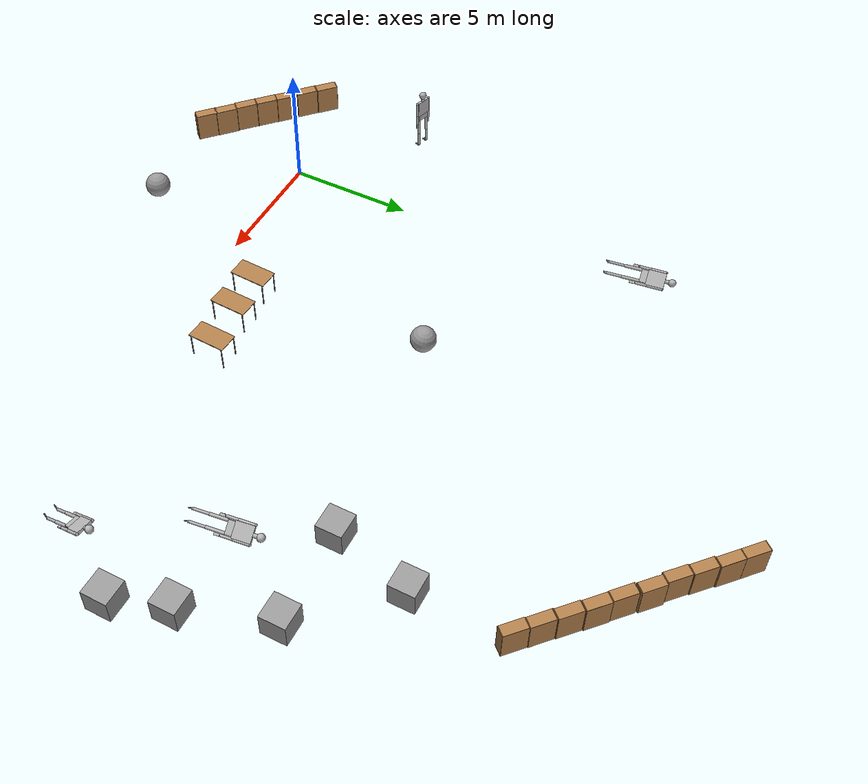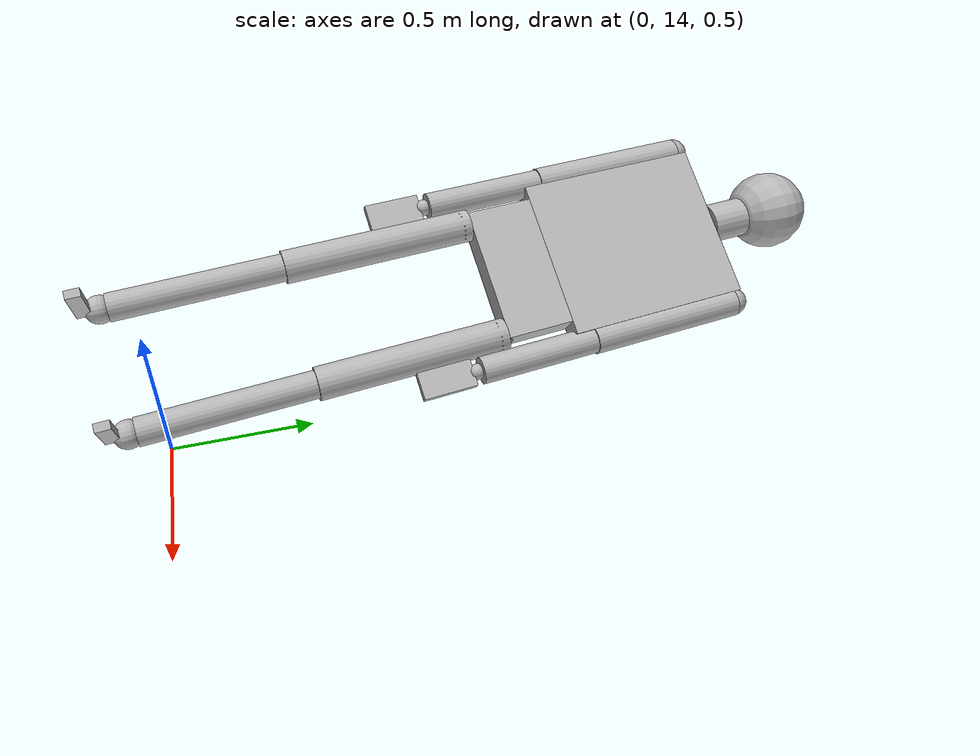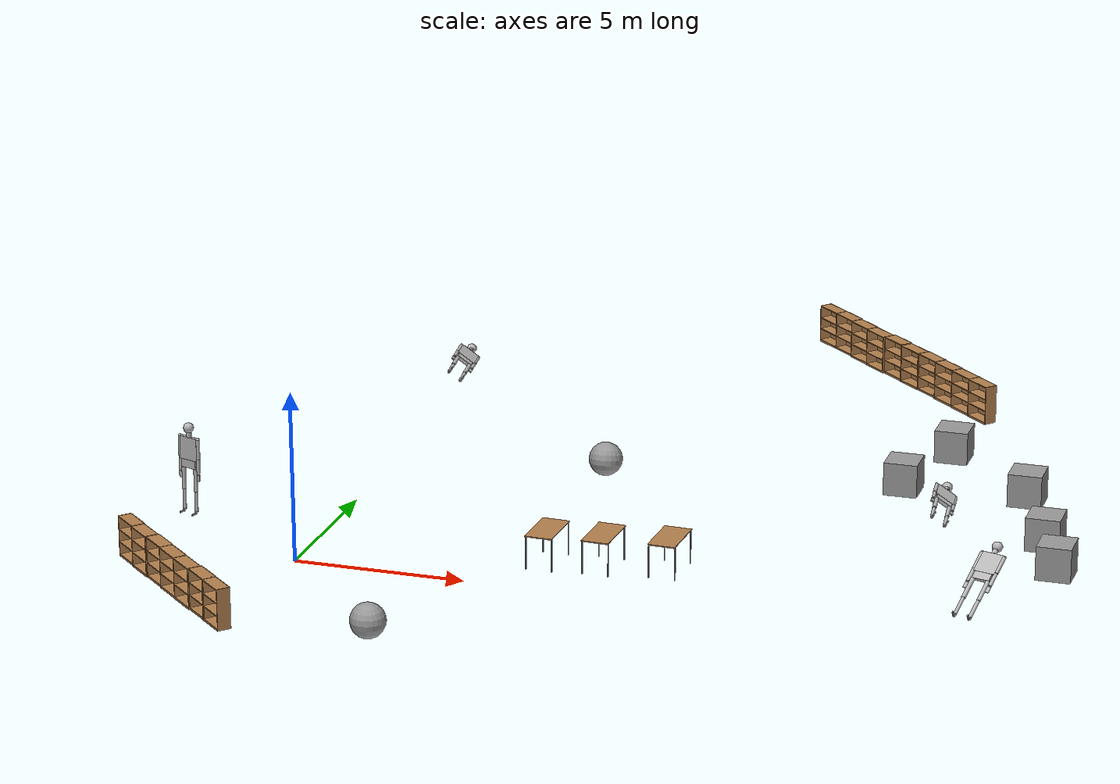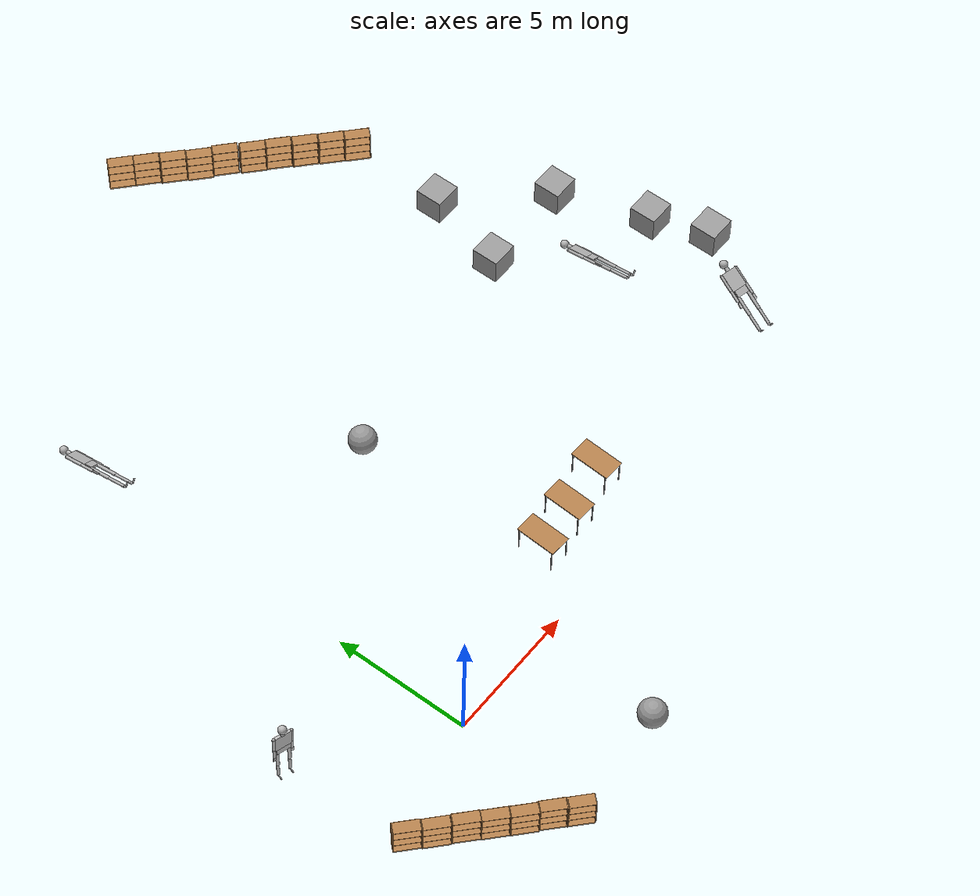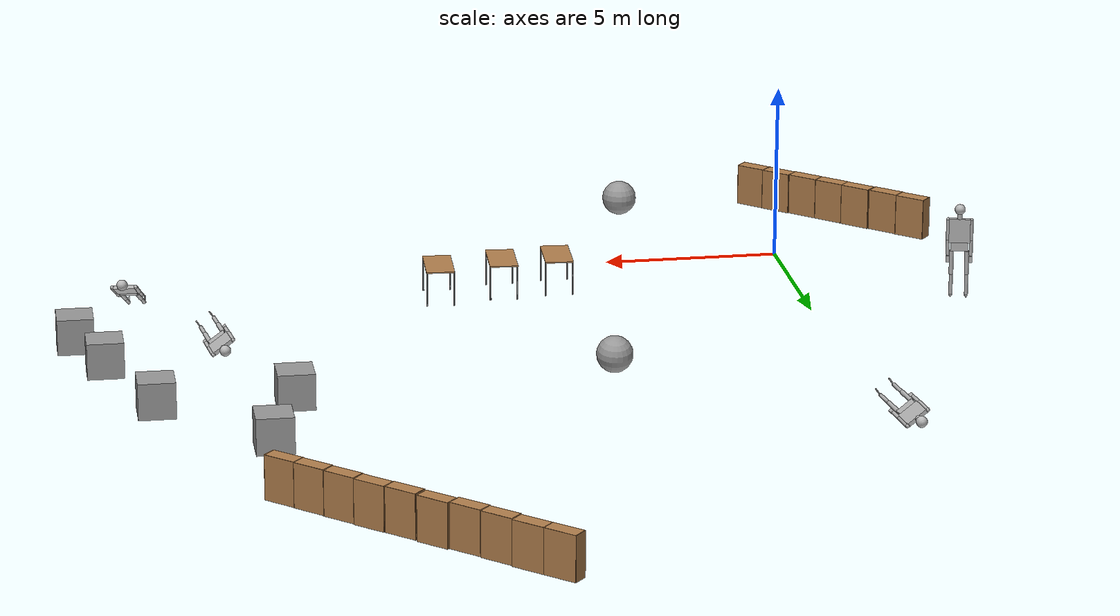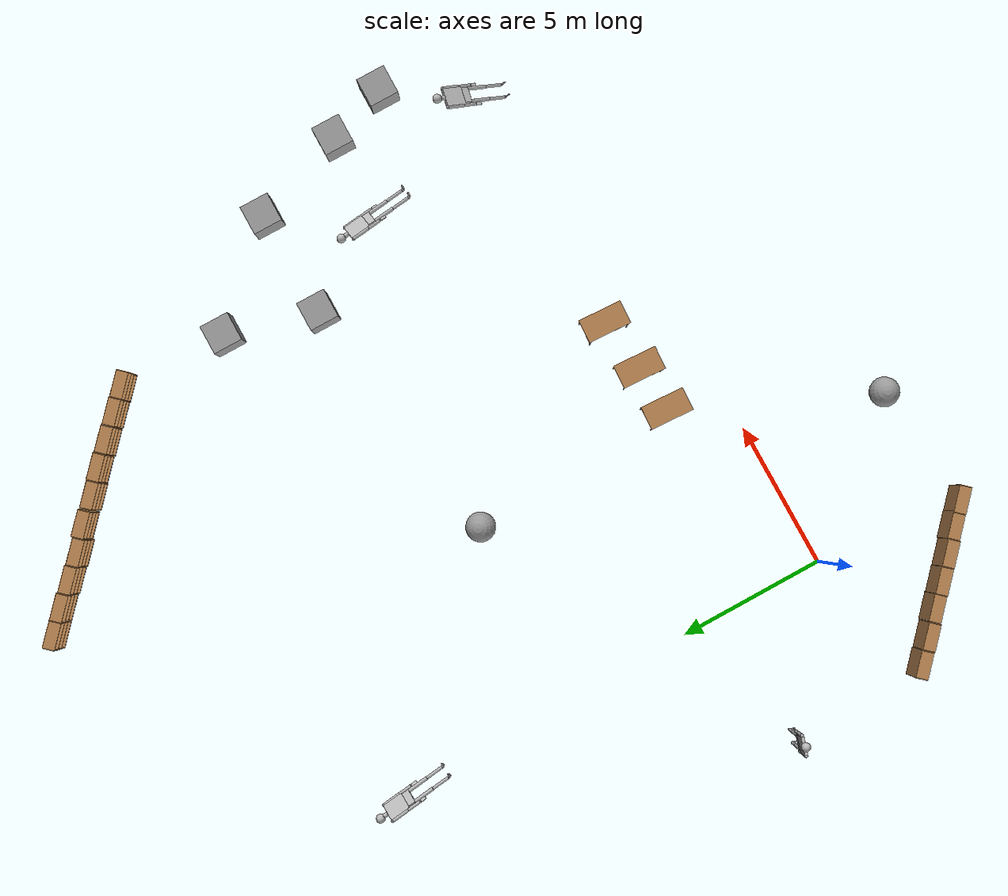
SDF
<sdf version="1.7">
 <world name="world_demo">
  <gravity>0 0 -9.8</gravity>
  <physics type="ode">
   <max_step_size>0.01</max_step_size>
   <real_time_factor>1</real_time_factor>
   <real_time_update_rate>1000</real_time_update_rate>
   <ode>
    <solver>
     <type>quick</type>
     <iters>50</iters>
     <sor>1.3</sor>
     <use_dynamic_moi_rescaling>0</use_dynamic_moi_rescaling>
    </solver>
    <constraints>
     <cfm>0</cfm>
     <erp>0.2</erp>
     <contact_max_correcting_vel>100</contact_max_correcting_vel>
     <contact_surface_layer>0.001</contact_surface_layer>
    </constraints>
   </ode>
  </physics>
  <plugin name="ignition::gazebo::systems::Physics" filename="libignition-gazebo-physics-system.so"/>
  <plugin name="ignition::gazebo::systems::UserCommands" filename="libignition-gazebo-user-commands-system.so"/>
  <plugin name="ignition::gazebo::systems::SceneBroadcaster" filename="libignition-gazebo-scene-broadcaster-system.so"/>
  <plugin name="ignition::gazebo::systems::Imu" filename="ignition-gazebo-imu-system"/>
  <plugin name="ignition::gazebo::systems::Sensors" filename="ignition-gazebo-sensors-system">
   <render_engine>ogre2</render_engine>
  </plugin>
  <scene>
   <ambient>1 1 1 1</ambient>
   <background>0.3 0.7 0.9 1</background>
   <shadows>0</shadows>
   <grid>0</grid>
  </scene>
  <magnetic_field>6e-06 2.3e-05 -4.2e-05</magnetic_field>
  <atmosphere type="adiabatic"/>
  <model name="ground_plane">
   <static>1</static>
   <link name="link">
    <collision name="collision">
     <geometry><plane><normal>0 0 1</normal><size>1 1</size></plane></geometry>
    </collision>
    <inertial>
     <mass>1</mass>
     <inertia><ixx>1</ixx><ixy>0</ixy><ixz>0</ixz><iyy>1</iyy><iyz>0</iyz><izz>1</izz></inertia>
    </inertial>
   </link>
  </model>
  <light name="sun" type="directional">
   <pose>-5 -3 10 0 -0 0</pose>
   <cast_shadows>0</cast_shadows>
   <direction>0 0 -1</direction>
   <diffuse>1 1 1 1</diffuse>
   <specular>1 1 1 1</specular>
   <attenuation><range>10</range><linear>1</linear><constant>1</constant><quadratic>0</quadratic></attenuation>
   <spot><inner_angle>0</inner_angle><outer_angle>0</outer_angle><falloff>0</falloff></spot>
   <intensity>1</intensity>
  </light>
  <audio><device>default</device></audio>
  <spherical_coordinates>
   <surface_model>EARTH_WGS84</surface_model>
   <latitude_deg>0</latitude_deg>
   <longitude_deg>0</longitude_deg>
   <elevation>0</elevation>
   <heading_deg>0</heading_deg>
  </spherical_coordinates>
  <model name="ragdoll_0">
   <pose>-4.59661 3.51218 1.04194 -0.011521 -0.00074 -1.86947</pose>
   <link name="hip">
    <inertial>
     <inertia><ixx>0.1</ixx><ixy>0</ixy><ixz>0</ixz><iyy>0.1</iyy><iyz>0</iyz><izz>0.1</izz></inertia>
     <mass>10</mass>
    </inertial>
    <collision name="hip_geom">
     <pose>0 0 0.125 0 -0 0</pose>
     <geometry><box><size>0.1 0.5 0.25</size></box></geometry>
     <surface>
      <friction><ode><mu>-1</mu><mu2>-1</mu2><fdir1>0 0 0</fdir1><slip1>0</slip1><slip2>0</slip2></ode></friction>
      <bounce><restitution_coefficient>0</restitution_coefficient><threshold>100000</threshold></bounce>
      <contact>
       <ode>
        <soft_cfm>0</soft_cfm>
        <soft_erp>0.2</soft_erp>
        <kp>1e+12</kp>
        <kd>1</kd>
        <max_vel>0</max_vel>
        <min_depth>0.001</min_depth>
       </ode>
      </contact>
     </surface>
    </collision>
    <visual name="hip_geom_visual">
     <pose>0 0 0.125 0 -0 0</pose>
     <geometry><box><size>0.1 0.5 0.25</size></box></geometry>
    </visual>
    <gravity>0</gravity>
   </link>
   <link name="l_thigh_pan">
    <pose>0 0.22 0 0 -0 0</pose>
    <inertial>
     <inertia><ixx>0.01</ixx><ixy>0</ixy><ixz>0</ixz><iyy>0.01</iyy><iyz>0</iyz><izz>0.01</izz></inertia>
     <mass>1</mass>
    </inertial>
    <collision name="l_thigh_pan_geom">
     <pose>0 0 -0.03 0 -0 0</pose>
     <geometry><sphere><radius>0.06</radius></sphere></geometry>
     <surface>
      <friction><ode><mu>-1</mu><mu2>-1</mu2><fdir1>0 0 0</fdir1><slip1>0</slip1><slip2>0</slip2></ode></friction>
      <bounce><restitution_coefficient>0</restitution_coefficient><threshold>100000</threshold></bounce>
      <contact>
       <ode>
        <soft_cfm>0</soft_cfm>
        <soft_erp>0.2</soft_erp>
        <kp>1e+12</kp>
        <kd>1</kd>
        <max_vel>0</max_vel>
        <min_depth>0.001</min_depth>
       </ode>
      </contact>
     </surface>
    </collision>
    <visual name="l_thigh_pan_geom_visual">
     <pose>0 0 -0.03 0 -0 0</pose>
     <geometry><sphere><radius>0.06</radius></sphere></geometry>
    </visual>
    <gravity>0</gravity>
   </link>
   <link name="l_thigh_lift">
    <pose>0 0.22 0 0 -0 0</pose>
    <inertial>
     <inertia><ixx>0.05</ixx><ixy>0</ixy><ixz>0</ixz><iyy>0.05</iyy><iyz>0</iyz><izz>0.05</izz></inertia>
     <mass>5</mass>
    </inertial>
    <collision name="l_thigh_lift_geom">
     <pose>0 0 -0.35 0 -0 0</pose>
     <geometry><cylinder><radius>0.06</radius><length>0.7</length></cylinder></geometry>
     <surface>
      <friction><ode><mu>-1</mu><mu2>-1</mu2><fdir1>0 0 0</fdir1><slip1>0</slip1><slip2>0</slip2></ode></friction>
      <bounce><restitution_coefficient>0</restitution_coefficient><threshold>100000</threshold></bounce>
      <contact>
       <ode>
        <soft_cfm>0</soft_cfm>
        <soft_erp>0.2</soft_erp>
        <kp>1e+12</kp>
        <kd>1</kd>
        <max_vel>0</max_vel>
        <min_depth>0.001</min_depth>
       </ode>
      </contact>
     </surface>
    </collision>
    <visual name="l_thigh_lift_geom_visual">
     <pose>0 0 -0.35 0 -0 0</pose>
     <geometry><cylinder><radius>0.06</radius><length>0.7</length></cylinder></geometry>
    </visual>
    <gravity>0</gravity>
   </link>
   <link name="l_calf">
    <pose>0 0.22 -0.7 0 -0 0</pose>
    <inertial>
     <inertia><ixx>0.02</ixx><ixy>0</ixy><ixz>0</ixz><iyy>0.02</iyy><iyz>0</iyz><izz>0.02</izz></inertia>
     <mass>2</mass>
    </inertial>
    <collision name="l_calf_geom">
     <pose>0 0 -0.3 0 -0 0</pose>
     <geometry><cylinder><radius>0.05</radius><length>0.6</length></cylinder></geometry>
     <surface>
      <friction><ode><mu>-1</mu><mu2>-1</mu2><fdir1>0 0 0</fdir1><slip1>0</slip1><slip2>0</slip2></ode></friction>
      <bounce><restitution_coefficient>0</restitution_coefficient><threshold>100000</threshold></bounce>
      <contact>
       <ode>
        <soft_cfm>0</soft_cfm>
        <soft_erp>0.2</soft_erp>
        <kp>1e+12</kp>
        <kd>1</kd>
        <max_vel>0</max_vel>
        <min_depth>0.001</min_depth>
       </ode>
      </contact>
     </surface>
    </collision>
    <visual name="l_calf_geom_visual">
     <pose>0 0 -0.3 0 -0 0</pose>
     <geometry><cylinder><radius>0.05</radius><length>0.6</length></cylinder></geometry>
    </visual>
    <gravity>0</gravity>
   </link>
   <link name="l_ankle">
    <pose>0 0.22 -1.325 0 -0 0</pose>
    <inertial>
     <inertia><ixx>0.01</ixx><ixy>0</ixy><ixz>0</ixz><iyy>0.01</iyy><iyz>0</iyz><izz>0.01</izz></inertia>
     <mass>1</mass>
    </inertial>
    <collision name="l_ankle_geom">
     <geometry><sphere><radius>0.05</radius></sphere></geometry>
     <surface>
      <friction><ode><mu>-1</mu><mu2>-1</mu2><fdir1>0 0 0</fdir1><slip1>0</slip1><slip2>0</slip2></ode></friction>
      <bounce><restitution_coefficient>0</restitution_coefficient><threshold>100000</threshold></bounce>
      <contact>
       <ode>
        <soft_cfm>0</soft_cfm>
        <soft_erp>0.2</soft_erp>
        <kp>1e+12</kp>
        <kd>1</kd>
        <max_vel>0</max_vel>
        <min_depth>0.001</min_depth>
       </ode>
      </contact>
     </surface>
    </collision>
    <visual name="l_ankle_geom_visual"><geometry><sphere><radius>0.05</radius></sphere></geometry></visual>
    <gravity>0</gravity>
   </link>
   <link name="l_foot">
    <pose>0 0.22 -1.35 0 -0 0</pose>
    <inertial>
     <pose>0.1 0 0 0 -0 0</pose>
     <inertia><ixx>0.01</ixx><ixy>0</ixy><ixz>0</ixz><iyy>0.01</iyy><iyz>0</iyz><izz>0.01</izz></inertia>
     <mass>1</mass>
    </inertial>
    <collision name="l_foot_geom">
     <pose>0.1 0 -0.025 0 -0 0</pose>
     <geometry><box><size>0.2 0.03 0.05</size></box></geometry>
     <surface>
      <friction><ode><mu>-1</mu><mu2>-1</mu2><fdir1>0 0 0</fdir1><slip1>0</slip1><slip2>0</slip2></ode></friction>
      <bounce><restitution_coefficient>0</restitution_coefficient><threshold>100000</threshold></bounce>
      <contact>
       <ode>
        <soft_cfm>0</soft_cfm>
        <soft_erp>0.2</soft_erp>
        <kp>1e+12</kp>
        <kd>1</kd>
        <max_vel>0</max_vel>
        <min_depth>0.001</min_depth>
       </ode>
      </contact>
     </surface>
    </collision>
    <visual name="l_foot_geom_visual">
     <pose>0.1 0 -0.025 0 -0 0</pose>
     <geometry><box><size>0.2 0.03 0.05</size></box></geometry>
    </visual>
   </link>
   <link name="r_thigh_pan">
    <pose>0 -0.22 0 0 -0 0</pose>
    <inertial>
     <inertia><ixx>0.01</ixx><ixy>0</ixy><ixz>0</ixz><iyy>0.01</iyy><iyz>0</iyz><izz>0.01</izz></inertia>
     <mass>1</mass>
    </inertial>
    <collision name="r_thigh_pan_geom">
     <pose>0 0 -0.03 0 -0 0</pose>
     <geometry><sphere><radius>0.06</radius></sphere></geometry>
     <surface>
      <friction><ode><mu>-1</mu><mu2>-1</mu2><fdir1>0 0 0</fdir1><slip1>0</slip1><slip2>0</slip2></ode></friction>
      <bounce><restitution_coefficient>0</restitution_coefficient><threshold>100000</threshold></bounce>
      <contact>
       <ode>
        <soft_cfm>0</soft_cfm>
        <soft_erp>0.2</soft_erp>
        <kp>1e+12</kp>
        <kd>1</kd>
        <max_vel>0</max_vel>
        <min_depth>0.001</min_depth>
       </ode>
      </contact>
     </surface>
    </collision>
    <visual name="r_thigh_pan_geom_visual">
     <pose>0 0 -0.03 0 -0 0</pose>
     <geometry><sphere><radius>0.06</radius></sphere></geometry>
    </visual>
    <gravity>0</gravity>
   </link>
   <link name="r_thigh_lift">
    <pose>0 -0.22 0 0 -0 0</pose>
    <inertial>
     <inertia><ixx>0.05</ixx><ixy>0</ixy><ixz>0</ixz><iyy>0.05</iyy><iyz>0</iyz><izz>0.05</izz></inertia>
     <mass>5</mass>
    </inertial>
    <collision name="r_thigh_lift_geom">
     <pose>0 0 -0.35 0 -0 0</pose>
     <geometry><cylinder><radius>0.06</radius><length>0.7</length></cylinder></geometry>
     <surface>
      <friction><ode><mu>-1</mu><mu2>-1</mu2><fdir1>0 0 0</fdir1><slip1>0</slip1><slip2>0</slip2></ode></friction>
      <bounce><restitution_coefficient>0</restitution_coefficient><threshold>100000</threshold></bounce>
      <contact>
       <ode>
        <soft_cfm>0</soft_cfm>
        <soft_erp>0.2</soft_erp>
        <kp>1e+12</kp>
        <kd>1</kd>
        <max_vel>0</max_vel>
        <min_depth>0.001</min_depth>
       </ode>
      </contact>
     </surface>
    </collision>
    <visual name="r_thigh_lift_geom_visual">
     <pose>0 0 -0.35 0 -0 0</pose>
     <geometry><cylinder><radius>0.06</radius><length>0.7</length></cylinder></geometry>
    </visual>
    <gravity>0</gravity>
   </link>
   <link name="r_calf">
    <pose>0 -0.22 -0.7 0 -0 0</pose>
    <inertial>
     <inertia><ixx>0.02</ixx><ixy>0</ixy><ixz>0</ixz><iyy>0.02</iyy><iyz>0</iyz><izz>0.02</izz></inertia>
     <mass>2</mass>
    </inertial>
    <collision name="r_calf_geom">
     <pose>0 0 -0.3 0 -0 0</pose>
     <geometry><cylinder><radius>0.05</radius><length>0.6</length></cylinder></geometry>
     <surface>
      <friction><ode><mu>-1</mu><mu2>-1</mu2><fdir1>0 0 0</fdir1><slip1>0</slip1><slip2>0</slip2></ode></friction>
      <bounce><restitution_coefficient>0</restitution_coefficient><threshold>100000</threshold></bounce>
      <contact>
       <ode>
        <soft_cfm>0</soft_cfm>
        <soft_erp>0.2</soft_erp>
        <kp>1e+12</kp>
        <kd>1</kd>
        <max_vel>0</max_vel>
        <min_depth>0.001</min_depth>
       </ode>
      </contact>
     </surface>
    </collision>
    <visual name="r_calf_geom_visual">
     <pose>0 0 -0.3 0 -0 0</pose>
     <geometry><cylinder><radius>0.05</radius><length>0.6</length></cylinder></geometry>
    </visual>
    <gravity>0</gravity>
   </link>
   <link name="r_ankle">
    <pose>0 -0.22 -1.325 0 -0 0</pose>
    <inertial>
     <inertia><ixx>0.01</ixx><ixy>0</ixy><ixz>0</ixz><iyy>0.01</iyy><iyz>0</iyz><izz>0.01</izz></inertia>
     <mass>1</mass>
    </inertial>
    <collision name="r_ankle_geom">
     <geometry><sphere><radius>0.05</radius></sphere></geometry>
     <surface>
      <friction><ode><mu>-1</mu><mu2>-1</mu2><fdir1>0 0 0</fdir1><slip1>0</slip1><slip2>0</slip2></ode></friction>
      <bounce><restitution_coefficient>0</restitution_coefficient><threshold>100000</threshold></bounce>
      <contact>
       <ode>
        <soft_cfm>0</soft_cfm>
        <soft_erp>0.2</soft_erp>
        <kp>1e+12</kp>
        <kd>1</kd>
        <max_vel>0</max_vel>
        <min_depth>0.001</min_depth>
       </ode>
      </contact>
     </surface>
    </collision>
    <visual name="r_ankle_geom_visual"><geometry><sphere><radius>0.05</radius></sphere></geometry></visual>
    <gravity>0</gravity>
   </link>
   <link name="r_foot">
    <pose>0 -0.22 -1.35 0 -0 0</pose>
    <inertial>
     <pose>0.1 0 0 0 -0 0</pose>
     <inertia><ixx>0.01</ixx><ixy>0</ixy><ixz>0</ixz><iyy>0.01</iyy><iyz>0</iyz><izz>0.01</izz></inertia>
     <mass>1</mass>
    </inertial>
    <collision name="r_foot_geom">
     <pose>0.1 0 -0.025 0 -0 0</pose>
     <geometry><box><size>0.2 0.03 0.05</size></box></geometry>
     <surface>
      <friction><ode><mu>-1</mu><mu2>-1</mu2><fdir1>0 0 0</fdir1><slip1>0</slip1><slip2>0</slip2></ode></friction>
      <bounce><restitution_coefficient>0</restitution_coefficient><threshold>100000</threshold></bounce>
      <contact>
       <ode>
        <soft_cfm>0</soft_cfm>
        <soft_erp>0.2</soft_erp>
        <kp>1e+12</kp>
        <kd>1</kd>
        <max_vel>0</max_vel>
        <min_depth>0.001</min_depth>
       </ode>
      </contact>
     </surface>
    </collision>
    <visual name="r_foot_geom_visual">
     <pose>0.1 0 -0.025 0 -0 0</pose>
     <geometry><box><size>0.2 0.03 0.05</size></box></geometry>
    </visual>
   </link>
   <link name="torso">
    <pose>0 0 0.25 0 -0 0</pose>
    <inertial>
     <inertia><ixx>0.3</ixx><ixy>0</ixy><ixz>0</ixz><iyy>0.3</iyy><iyz>0</iyz><izz>0.3</izz></inertia>
     <mass>30</mass>
    </inertial>
    <collision name="torso_geom">
     <pose>0 0 0.35 0 -0 0</pose>
     <geometry><box><size>0.1 0.6 0.7</size></box></geometry>
     <surface>
      <friction><ode><mu>-1</mu><mu2>-1</mu2><fdir1>0 0 0</fdir1><slip1>0</slip1><slip2>0</slip2></ode></friction>
      <bounce><restitution_coefficient>0</restitution_coefficient><threshold>100000</threshold></bounce>
      <contact>
       <ode>
        <soft_cfm>0</soft_cfm>
        <soft_erp>0.2</soft_erp>
        <kp>1e+12</kp>
        <kd>1</kd>
        <max_vel>0</max_vel>
        <min_depth>0.001</min_depth>
       </ode>
      </contact>
     </surface>
    </collision>
    <visual name="torso_geom_visual">
     <pose>0 0 0.35 0 -0 0</pose>
     <geometry><box><size>0.1 0.6 0.7</size></box></geometry>
    </visual>
    <gravity>0</gravity>
   </link>
   <link name="l_shoulder">
    <pose>0 0.3275 0.9225 0 -0 0</pose>
    <inertial>
     <inertia><ixx>0.01</ixx><ixy>0</ixy><ixz>0</ixz><iyy>0.01</iyy><iyz>0</iyz><izz>0.01</izz></inertia>
     <mass>1</mass>
    </inertial>
    <collision name="l_shoulder_geom">
     <geometry><sphere><radius>0.055</radius></sphere></geometry>
     <surface>
      <friction><ode><mu>-1</mu><mu2>-1</mu2><fdir1>0 0 0</fdir1><slip1>0</slip1><slip2>0</slip2></ode></friction>
      <bounce><restitution_coefficient>0</restitution_coefficient><threshold>100000</threshold></bounce>
      <contact>
       <ode>
        <soft_cfm>0</soft_cfm>
        <soft_erp>0.2</soft_erp>
        <kp>1e+12</kp>
        <kd>1</kd>
        <max_vel>0</max_vel>
        <min_depth>0.001</min_depth>
       </ode>
      </contact>
     </surface>
    </collision>
    <visual name="l_shoulder_geom_visual"><geometry><sphere><radius>0.055</radius></sphere></geometry></visual>
    <gravity>0</gravity>
   </link>
   <link name="l_upper_arm">
    <pose>0 0.3275 0.9225 0 -0 0</pose>
    <inertial>
     <inertia><ixx>0.02</ixx><ixy>0</ixy><ixz>0</ixz><iyy>0.02</iyy><iyz>0</iyz><izz>0.02</izz></inertia>
     <mass>2</mass>
    </inertial>
    <collision name="l_upper_arm_geom">
     <pose>0 0 -0.3 0 -0 0</pose>
     <geometry><cylinder><radius>0.055</radius><length>0.6</length></cylinder></geometry>
     <surface>
      <friction><ode><mu>-1</mu><mu2>-1</mu2><fdir1>0 0 0</fdir1><slip1>0</slip1><slip2>0</slip2></ode></friction>
      <bounce><restitution_coefficient>0</restitution_coefficient><threshold>100000</threshold></bounce>
      <contact>
       <ode>
        <soft_cfm>0</soft_cfm>
        <soft_erp>0.2</soft_erp>
        <kp>1e+12</kp>
        <kd>1</kd>
        <max_vel>0</max_vel>
        <min_depth>0.001</min_depth>
       </ode>
      </contact>
     </surface>
    </collision>
    <visual name="l_upper_arm_geom_visual">
     <pose>0 0 -0.3 0 -0 0</pose>
     <geometry><cylinder><radius>0.055</radius><length>0.6</length></cylinder></geometry>
    </visual>
    <gravity>0</gravity>
   </link>
   <link name="l_forearm">
    <pose>0 0.3275 0.3225 0 -0 0</pose>
    <inertial>
     <inertia><ixx>0.01</ixx><ixy>0</ixy><ixz>0</ixz><iyy>0.01</iyy><iyz>0</iyz><izz>0.01</izz></inertia>
     <mass>1</mass>
    </inertial>
    <collision name="l_forearm_geom">
     <pose>0 0 -0.225 0 -0 0</pose>
     <geometry><cylinder><radius>0.05</radius><length>0.45</length></cylinder></geometry>
     <surface>
      <friction><ode><mu>-1</mu><mu2>-1</mu2><fdir1>0 0 0</fdir1><slip1>0</slip1><slip2>0</slip2></ode></friction>
      <bounce><restitution_coefficient>0</restitution_coefficient><threshold>100000</threshold></bounce>
      <contact>
       <ode>
        <soft_cfm>0</soft_cfm>
        <soft_erp>0.2</soft_erp>
        <kp>1e+12</kp>
        <kd>1</kd>
        <max_vel>0</max_vel>
        <min_depth>0.001</min_depth>
       </ode>
      </contact>
     </surface>
    </collision>
    <visual name="l_forearm_geom_visual">
     <pose>0 0 -0.225 0 -0 0</pose>
     <geometry><cylinder><radius>0.05</radius><length>0.45</length></cylinder></geometry>
    </visual>
    <gravity>0</gravity>
   </link>
   <link name="l_wrist">
    <pose>0 0.3275 -0.1425 0 -0 0</pose>
    <inertial>
     <inertia><ixx>0.01</ixx><ixy>0</ixy><ixz>0</ixz><iyy>0.01</iyy><iyz>0</iyz><izz>0.01</izz></inertia>
     <mass>1</mass>
    </inertial>
    <collision name="l_wrist_geom">
     <geometry><sphere><radius>0.03</radius></sphere></geometry>
     <surface>
      <friction><ode><mu>-1</mu><mu2>-1</mu2><fdir1>0 0 0</fdir1><slip1>0</slip1><slip2>0</slip2></ode></friction>
      <bounce><restitution_coefficient>0</restitution_coefficient><threshold>100000</threshold></bounce>
      <contact>
       <ode>
        <soft_cfm>0</soft_cfm>
        <soft_erp>0.2</soft_erp>
        <kp>1e+12</kp>
        <kd>1</kd>
        <max_vel>0</max_vel>
        <min_depth>0.001</min_depth>
       </ode>
      </contact>
     </surface>
    </collision>
    <visual name="l_wrist_geom_visual"><geometry><sphere><radius>0.03</radius></sphere></geometry></visual>
    <gravity>0</gravity>
   </link>
   <link name="l_hand">
    <pose>0 0.3275 -0.1575 0 -0 0</pose>
    <inertial>
     <inertia><ixx>0.01</ixx><ixy>0</ixy><ixz>0</ixz><iyy>0.01</iyy><iyz>0</iyz><izz>0.01</izz></inertia>
     <mass>1</mass>
    </inertial>
    <collision name="l_hand_geom">
     <pose>0 0 -0.1 0 -0 0</pose>
     <geometry><box><size>0.03 0.1 0.2</size></box></geometry>
     <surface>
      <friction><ode><mu>-1</mu><mu2>-1</mu2><fdir1>0 0 0</fdir1><slip1>0</slip1><slip2>0</slip2></ode></friction>
      <bounce><restitution_coefficient>0</restitution_coefficient><threshold>100000</threshold></bounce>
      <contact>
       <ode>
        <soft_cfm>0</soft_cfm>
        <soft_erp>0.2</soft_erp>
        <kp>1e+12</kp>
        <kd>1</kd>
        <max_vel>0</max_vel>
        <min_depth>0.001</min_depth>
       </ode>
      </contact>
     </surface>
    </collision>
    <visual name="l_hand_geom_visual">
     <pose>0 0 -0.1 0 -0 0</pose>
     <geometry><box><size>0.03 0.1 0.2</size></box></geometry>
    </visual>
    <gravity>0</gravity>
   </link>
   <link name="neck">
    <pose>0 0 0.95 0 -0 0</pose>
    <inertial>
     <inertia><ixx>0.01</ixx><ixy>0</ixy><ixz>0</ixz><iyy>0.01</iyy><iyz>0</iyz><izz>0.01</izz></inertia>
     <mass>1</mass>
    </inertial>
    <collision name="neck_geom">
     <pose>0 0 0.1 0 -0 0</pose>
     <geometry><cylinder><radius>0.075</radius><length>0.2</length></cylinder></geometry>
     <surface>
      <friction><ode><mu>-1</mu><mu2>-1</mu2><fdir1>0 0 0</fdir1><slip1>0</slip1><slip2>0</slip2></ode></friction>
      <bounce><restitution_coefficient>0</restitution_coefficient><threshold>100000</threshold></bounce>
      <contact>
       <ode>
        <soft_cfm>0</soft_cfm>
        <soft_erp>0.2</soft_erp>
        <kp>1e+12</kp>
        <kd>1</kd>
        <max_vel>0</max_vel>
        <min_depth>0.001</min_depth>
       </ode>
      </contact>
     </surface>
    </collision>
    <visual name="neck_geom_visual">
     <pose>0 0 0.1 0 -0 0</pose>
     <geometry><cylinder><radius>0.075</radius><length>0.2</length></cylinder></geometry>
    </visual>
    <gravity>0</gravity>
   </link>
   <link name="head">
    <pose>0 0 1.225 0 -0 0</pose>
    <inertial>
     <inertia><ixx>0.1</ixx><ixy>0</ixy><ixz>0</ixz><iyy>0.1</iyy><iyz>0</iyz><izz>0.1</izz></inertia>
     <mass>10</mass>
    </inertial>
    <collision name="head_geom">
     <geometry><sphere><radius>0.15</radius></sphere></geometry>
     <surface>
      <friction><ode><mu>-1</mu><mu2>-1</mu2><fdir1>0 0 0</fdir1><slip1>0</slip1><slip2>0</slip2></ode></friction>
      <bounce><restitution_coefficient>0</restitution_coefficient><threshold>100000</threshold></bounce>
      <contact>
       <ode>
        <soft_cfm>0</soft_cfm>
        <soft_erp>0.2</soft_erp>
        <kp>1e+12</kp>
        <kd>1</kd>
        <max_vel>0</max_vel>
        <min_depth>0.001</min_depth>
       </ode>
      </contact>
     </surface>
    </collision>
    <visual name="head_geom_visual"><geometry><sphere><radius>0.15</radius></sphere></geometry></visual>
    <gravity>0</gravity>
   </link>
   <link name="r_shoulder">
    <pose>0 -0.3275 0.9225 0 -0 0</pose>
    <inertial>
     <inertia><ixx>0.01</ixx><ixy>0</ixy><ixz>0</ixz><iyy>0.01</iyy><iyz>0</iyz><izz>0.01</izz></inertia>
     <mass>1</mass>
    </inertial>
    <collision name="r_shoulder_geom">
     <geometry><sphere><radius>0.055</radius></sphere></geometry>
     <surface>
      <friction><ode><mu>-1</mu><mu2>-1</mu2><fdir1>0 0 0</fdir1><slip1>0</slip1><slip2>0</slip2></ode></friction>
      <bounce><restitution_coefficient>0</restitution_coefficient><threshold>100000</threshold></bounce>
      <contact>
       <ode>
        <soft_cfm>0</soft_cfm>
        <soft_erp>0.2</soft_erp>
        <kp>1e+12</kp>
        <kd>1</kd>
        <max_vel>0</max_vel>
        <min_depth>0.001</min_depth>
       </ode>
      </contact>
     </surface>
    </collision>
    <visual name="r_shoulder_geom_visual"><geometry><sphere><radius>0.055</radius></sphere></geometry></visual>
    <gravity>0</gravity>
   </link>
   <link name="r_upper_arm">
    <pose>0 -0.3275 0.9225 0 -0 0</pose>
    <inertial>
     <inertia><ixx>0.02</ixx><ixy>0</ixy><ixz>0</ixz><iyy>0.02</iyy><iyz>0</iyz><izz>0.02</izz></inertia>
     <mass>2</mass>
    </inertial>
    <collision name="r_upper_arm_geom">
     <pose>0 0 -0.3 0 -0 0</pose>
     <geometry><cylinder><radius>0.055</radius><length>0.6</length></cylinder></geometry>
     <surface>
      <friction><ode><mu>-1</mu><mu2>-1</mu2><fdir1>0 0 0</fdir1><slip1>0</slip1><slip2>0</slip2></ode></friction>
      <bounce><restitution_coefficient>0</restitution_coefficient><threshold>100000</threshold></bounce>
      <contact>
       <ode>
        <soft_cfm>0</soft_cfm>
        <soft_erp>0.2</soft_erp>
        <kp>1e+12</kp>
        <kd>1</kd>
        <max_vel>0</max_vel>
        <min_depth>0.001</min_depth>
       </ode>
      </contact>
     </surface>
    </collision>
    <visual name="r_upper_arm_geom_visual">
     <pose>0 0 -0.3 0 -0 0</pose>
     <geometry><cylinder><radius>0.055</radius><length>0.6</length></cylinder></geometry>
    </visual>
    <gravity>0</gravity>
   </link>
   <link name="r_forearm">
    <pose>0 -0.3275 0.3225 0 -0 0</pose>
    <inertial>
     <inertia><ixx>0.01</ixx><ixy>0</ixy><ixz>0</ixz><iyy>0.01</iyy><iyz>0</iyz><izz>0.01</izz></inertia>
     <mass>1</mass>
    </inertial>
    <collision name="r_forearm_geom">
     <pose>0 0 -0.225 0 -0 0</pose>
     <geometry><cylinder><radius>0.05</radius><length>0.45</length></cylinder></geometry>
     <surface>
      <friction><ode><mu>-1</mu><mu2>-1</mu2><fdir1>0 0 0</fdir1><slip1>0</slip1><slip2>0</slip2></ode></friction>
      <bounce><restitution_coefficient>0</restitution_coefficient><threshold>100000</threshold></bounce>
      <contact>
       <ode>
        <soft_cfm>0</soft_cfm>
        <soft_erp>0.2</soft_erp>
        <kp>1e+12</kp>
        <kd>1</kd>
        <max_vel>0</max_vel>
        <min_depth>0.001</min_depth>
       </ode>
      </contact>
     </surface>
    </collision>
    <visual name="r_forearm_geom_visual">
     <pose>0 0 -0.225 0 -0 0</pose>
     <geometry><cylinder><radius>0.05</radius><length>0.45</length></cylinder></geometry>
    </visual>
    <gravity>0</gravity>
   </link>
   <link name="r_wrist">
    <pose>0 -0.3275 -0.1425 0 -0 0</pose>
    <inertial>
     <inertia><ixx>0.01</ixx><ixy>0</ixy><ixz>0</ixz><iyy>0.01</iyy><iyz>0</iyz><izz>0.01</izz></inertia>
     <mass>1</mass>
    </inertial>
    <collision name="r_wrist_geom">
     <geometry><sphere><radius>0.03</radius></sphere></geometry>
     <surface>
      <friction><ode><mu>-1</mu><mu2>-1</mu2><fdir1>0 0 0</fdir1><slip1>0</slip1><slip2>0</slip2></ode></friction>
      <bounce><restitution_coefficient>0</restitution_coefficient><threshold>100000</threshold></bounce>
      <contact>
       <ode>
        <soft_cfm>0</soft_cfm>
        <soft_erp>0.2</soft_erp>
        <kp>1e+12</kp>
        <kd>1</kd>
        <max_vel>0</max_vel>
        <min_depth>0.001</min_depth>
       </ode>
      </contact>
     </surface>
    </collision>
    <visual name="r_wrist_geom_visual"><geometry><sphere><radius>0.03</radius></sphere></geometry></visual>
    <gravity>0</gravity>
   </link>
   <link name="r_hand">
    <pose>0 -0.3275 -0.1575 0 -0 0</pose>
    <inertial>
     <inertia><ixx>0.01</ixx><ixy>0</ixy><ixz>0</ixz><iyy>0.01</iyy><iyz>0</iyz><izz>0.01</izz></inertia>
     <mass>1</mass>
    </inertial>
    <collision name="r_hand_geom">
     <pose>0 0 -0.1 0 -0 0</pose>
     <geometry><box><size>0.03 0.1 0.2</size></box></geometry>
     <surface>
      <friction><ode><mu>-1</mu><mu2>-1</mu2><fdir1>0 0 0</fdir1><slip1>0</slip1><slip2>0</slip2></ode></friction>
      <bounce><restitution_coefficient>0</restitution_coefficient><threshold>100000</threshold></bounce>
      <contact>
       <ode>
        <soft_cfm>0</soft_cfm>
        <soft_erp>0.2</soft_erp>
        <kp>1e+12</kp>
        <kd>1</kd>
        <max_vel>0</max_vel>
        <min_depth>0.001</min_depth>
       </ode>
      </contact>
     </surface>
    </collision>
    <visual name="r_hand_geom_visual">
     <pose>0 0 -0.1 0 -0 0</pose>
     <geometry><box><size>0.03 0.1 0.2</size></box></geometry>
    </visual>
    <gravity>0</gravity>
   </link>
   <joint name="l_thigh_pan_joint" type="revolute">
    <parent>hip</parent>
    <child>l_thigh_pan</child>
    <axis>
     <dynamics>
      <damping>0</damping>
      <friction>0</friction>
      <spring_reference>0</spring_reference>
      <spring_stiffness>0</spring_stiffness>
     </dynamics>
     <limit><lower>-1.5708</lower><upper>1.5708</upper><effort>0</effort><velocity>0</velocity></limit>
     <xyz expressed_in="__model__">0 0 1</xyz>
    </axis>
   </joint>
   <joint name="l_thigh_lift_joint" type="revolute">
    <parent>l_thigh_pan</parent>
    <child>l_thigh_lift</child>
    <axis>
     <dynamics>
      <damping>0</damping>
      <friction>0</friction>
      <spring_reference>0</spring_reference>
      <spring_stiffness>0</spring_stiffness>
     </dynamics>
     <limit><lower>-1.5708</lower><upper>1.5708</upper><effort>0</effort><velocity>0</velocity></limit>
     <xyz expressed_in="__model__">0 1 0</xyz>
    </axis>
   </joint>
   <joint name="l_calf_joint" type="revolute">
    <parent>l_thigh_lift</parent>
    <child>l_calf</child>
    <axis>
     <dynamics>
      <damping>0</damping>
      <friction>0</friction>
      <spring_reference>0</spring_reference>
      <spring_stiffness>0</spring_stiffness>
     </dynamics>
     <limit><lower>-1.5708</lower><upper>1.5708</upper><effort>0</effort><velocity>0</velocity></limit>
     <xyz expressed_in="__model__">0 1 0</xyz>
    </axis>
   </joint>
   <joint name="l_ankle_joint" type="revolute">
    <parent>l_calf</parent>
    <child>l_ankle</child>
    <axis>
     <dynamics>
      <damping>0</damping>
      <friction>0</friction>
      <spring_reference>0</spring_reference>
      <spring_stiffness>0</spring_stiffness>
     </dynamics>
     <limit><lower>-1.5708</lower><upper>1.5708</upper><effort>0</effort><velocity>0</velocity></limit>
     <xyz expressed_in="__model__">0 1 0</xyz>
    </axis>
   </joint>
   <joint name="l_foot_joint" type="revolute">
    <parent>l_ankle</parent>
    <child>l_foot</child>
    <axis>
     <dynamics>
      <damping>0</damping>
      <friction>0</friction>
      <spring_reference>0</spring_reference>
      <spring_stiffness>0</spring_stiffness>
     </dynamics>
     <limit><lower>-1.5708</lower><upper>1.5708</upper><effort>0</effort><velocity>0</velocity></limit>
     <xyz expressed_in="__model__">1 0 0</xyz>
    </axis>
   </joint>
   <joint name="r_thigh_pan_joint" type="revolute">
    <parent>hip</parent>
    <child>r_thigh_pan</child>
    <axis>
     <dynamics>
      <damping>0</damping>
      <friction>0</friction>
      <spring_reference>0</spring_reference>
      <spring_stiffness>0</spring_stiffness>
     </dynamics>
     <limit><lower>-1.5708</lower><upper>1.5708</upper><effort>0</effort><velocity>0</velocity></limit>
     <xyz expressed_in="__model__">0 0 1</xyz>
    </axis>
   </joint>
   <joint name="r_thigh_lift_joint" type="revolute">
    <parent>r_thigh_pan</parent>
    <child>r_thigh_lift</child>
    <axis>
     <dynamics>
      <damping>0</damping>
      <friction>0</friction>
      <spring_reference>0</spring_reference>
      <spring_stiffness>0</spring_stiffness>
     </dynamics>
     <limit><lower>-1.5708</lower><upper>1.5708</upper><effort>0</effort><velocity>0</velocity></limit>
     <xyz expressed_in="__model__">0 1 0</xyz>
    </axis>
   </joint>
   <joint name="r_calf_joint" type="revolute">
    <parent>r_thigh_lift</parent>
    <child>r_calf</child>
    <axis>
     <dynamics>
      <damping>0</damping>
      <friction>0</friction>
      <spring_reference>0</spring_reference>
      <spring_stiffness>0</spring_stiffness>
     </dynamics>
     <limit><lower>-1.5708</lower><upper>1.5708</upper><effort>0</effort><velocity>0</velocity></limit>
     <xyz expressed_in="__model__">0 1 0</xyz>
    </axis>
   </joint>
   <joint name="r_ankle_joint" type="revolute">
    <parent>r_calf</parent>
    <child>r_ankle</child>
    <axis>
     <dynamics>
      <damping>0</damping>
      <friction>0</friction>
      <spring_reference>0</spring_reference>
      <spring_stiffness>0</spring_stiffness>
     </dynamics>
     <limit><lower>-1.5708</lower><upper>1.5708</upper><effort>0</effort><velocity>0</velocity></limit>
     <xyz expressed_in="__model__">0 1 0</xyz>
    </axis>
   </joint>
   <joint name="r_foot_joint" type="revolute">
    <parent>r_ankle</parent>
    <child>r_foot</child>
    <axis>
     <dynamics>
      <damping>0</damping>
      <friction>0</friction>
      <spring_reference>0</spring_reference>
      <spring_stiffness>0</spring_stiffness>
     </dynamics>
     <limit><lower>-1.5708</lower><upper>1.5708</upper><effort>0</effort><velocity>0</velocity></limit>
     <xyz expressed_in="__model__">1 0 0</xyz>
    </axis>
   </joint>
   <joint name="torso_joint" type="revolute">
    <parent>hip</parent>
    <child>torso</child>
    <axis>
     <dynamics>
      <damping>0</damping>
      <friction>0</friction>
      <spring_reference>0</spring_reference>
      <spring_stiffness>0</spring_stiffness>
     </dynamics>
     <limit><lower>-1.5708</lower><upper>1.5708</upper><effort>0</effort><velocity>0</velocity></limit>
     <xyz expressed_in="__model__">0 1 0</xyz>
    </axis>
   </joint>
   <joint name="l_shoulder_joint" type="revolute">
    <parent>torso</parent>
    <child>l_shoulder</child>
    <axis>
     <dynamics>
      <damping>0</damping>
      <friction>0</friction>
      <spring_reference>0</spring_reference>
      <spring_stiffness>0</spring_stiffness>
     </dynamics>
     <limit><lower>-1.5708</lower><upper>1.5708</upper><effort>0</effort><velocity>0</velocity></limit>
     <xyz expressed_in="__model__">1 0 0</xyz>
    </axis>
   </joint>
   <joint name="l_upper_arm_joint" type="revolute">
    <parent>l_shoulder</parent>
    <child>l_upper_arm</child>
    <axis>
     <dynamics>
      <damping>0</damping>
      <friction>0</friction>
      <spring_reference>0</spring_reference>
      <spring_stiffness>0</spring_stiffness>
     </dynamics>
     <limit><lower>-1.5708</lower><upper>1.5708</upper><effort>0</effort><velocity>0</velocity></limit>
     <xyz expressed_in="__model__">0 1 0</xyz>
    </axis>
   </joint>
   <joint name="l_forearm_joint" type="revolute">
    <parent>l_upper_arm</parent>
    <child>l_forearm</child>
    <axis>
     <dynamics>
      <damping>0</damping>
      <friction>0</friction>
      <spring_reference>0</spring_reference>
      <spring_stiffness>0</spring_stiffness>
     </dynamics>
     <limit><lower>-1.5708</lower><upper>1.5708</upper><effort>0</effort><velocity>0</velocity></limit>
     <xyz expressed_in="__model__">0 1 0</xyz>
    </axis>
   </joint>
   <joint name="l_wrist_joint" type="revolute">
    <parent>l_forearm</parent>
    <child>l_wrist</child>
    <axis>
     <dynamics>
      <damping>0</damping>
      <friction>0</friction>
      <spring_reference>0</spring_reference>
      <spring_stiffness>0</spring_stiffness>
     </dynamics>
     <limit><lower>-1.5708</lower><upper>1.5708</upper><effort>0</effort><velocity>0</velocity></limit>
     <xyz expressed_in="__model__">0 1 0</xyz>
    </axis>
   </joint>
   <joint name="l_hand_joint" type="revolute">
    <parent>l_wrist</parent>
    <child>l_hand</child>
    <axis>
     <dynamics>
      <damping>0</damping>
      <friction>0</friction>
      <spring_reference>0</spring_reference>
      <spring_stiffness>0</spring_stiffness>
     </dynamics>
     <limit><lower>-1.5708</lower><upper>1.5708</upper><effort>0</effort><velocity>0</velocity></limit>
     <xyz expressed_in="__model__">0 1 0</xyz>
    </axis>
   </joint>
   <joint name="neck_joint" type="revolute">
    <parent>torso</parent>
    <child>neck</child>
    <axis>
     <dynamics>
      <damping>0</damping>
      <friction>0</friction>
      <spring_reference>0</spring_reference>
      <spring_stiffness>0</spring_stiffness>
     </dynamics>
     <limit><lower>-1.5708</lower><upper>1.5708</upper><effort>0</effort><velocity>0</velocity></limit>
     <xyz expressed_in="__model__">0 0 1</xyz>
    </axis>
   </joint>
   <joint name="head_joint" type="revolute">
    <parent>neck</parent>
    <child>head</child>
    <axis>
     <dynamics>
      <damping>0</damping>
      <friction>0</friction>
      <spring_reference>0</spring_reference>
      <spring_stiffness>0</spring_stiffness>
     </dynamics>
     <limit><lower>-1.5708</lower><upper>1.5708</upper><effort>0</effort><velocity>0</velocity></limit>
     <xyz expressed_in="__model__">0 1 0</xyz>
    </axis>
   </joint>
   <joint name="r_shoulder_joint" type="revolute">
    <parent>torso</parent>
    <child>r_shoulder</child>
    <axis>
     <dynamics>
      <damping>0</damping>
      <friction>0</friction>
      <spring_reference>0</spring_reference>
      <spring_stiffness>0</spring_stiffness>
     </dynamics>
     <limit><lower>-1.5708</lower><upper>1.5708</upper><effort>0</effort><velocity>0</velocity></limit>
     <xyz expressed_in="__model__">1 0 0</xyz>
    </axis>
   </joint>
   <joint name="r_upper_arm_joint" type="revolute">
    <parent>r_shoulder</parent>
    <child>r_upper_arm</child>
    <axis>
     <dynamics>
      <damping>0</damping>
      <friction>0</friction>
      <spring_reference>0</spring_reference>
      <spring_stiffness>0</spring_stiffness>
     </dynamics>
     <limit><lower>-1.5708</lower><upper>1.5708</upper><effort>0</effort><velocity>0</velocity></limit>
     <xyz expressed_in="__model__">0 1 0</xyz>
    </axis>
   </joint>
   <joint name="r_forearm_joint" type="revolute">
    <parent>r_upper_arm</parent>
    <child>r_forearm</child>
    <axis>
     <dynamics>
      <damping>0</damping>
      <friction>0</friction>
      <spring_reference>0</spring_reference>
      <spring_stiffness>0</spring_stiffness>
     </dynamics>
     <limit><lower>-1.5708</lower><upper>1.5708</upper><effort>0</effort><velocity>0</velocity></limit>
     <xyz expressed_in="__model__">0 1 0</xyz>
    </axis>
   </joint>
   <joint name="r_wrist_joint" type="revolute">
    <parent>r_forearm</parent>
    <child>r_wrist</child>
    <axis>
     <dynamics>
      <damping>0</damping>
      <friction>0</friction>
      <spring_reference>0</spring_reference>
      <spring_stiffness>0</spring_stiffness>
     </dynamics>
     <limit><lower>-1.5708</lower><upper>1.5708</upper><effort>0</effort><velocity>0</velocity></limit>
     <xyz expressed_in="__model__">0 1 0</xyz>
    </axis>
   </joint>
   <joint name="r_hand_joint" type="revolute">
    <parent>r_wrist</parent>
    <child>r_hand</child>
    <axis>
     <dynamics>
      <damping>0</damping>
      <friction>0</friction>
      <spring_reference>0</spring_reference>
      <spring_stiffness>0</spring_stiffness>
     </dynamics>
     <limit><lower>-1.5708</lower><upper>1.5708</upper><effort>0</effort><velocity>0</velocity></limit>
     <xyz expressed_in="__model__">0 1 0</xyz>
    </axis>
   </joint>
   <static>0</static>
  </model>
  <model name="ragdoll_1">
   <pose>18.9383 2.67641 0.654274 -0.069959 -1.05083 -1.7112</pose>
   <link name="hip">
    <inertial>
     <inertia><ixx>0.1</ixx><ixy>0</ixy><ixz>0</ixz><iyy>0.1</iyy><iyz>0</iyz><izz>0.1</izz></inertia>
     <mass>10</mass>
    </inertial>
    <collision name="hip_geom">
     <pose>0 0 0.125 0 -0 0</pose>
     <geometry><box><size>0.1 0.5 0.25</size></box></geometry>
     <surface>
      <friction><ode><mu>-1</mu><mu2>-1</mu2><fdir1>0 0 0</fdir1><slip1>0</slip1><slip2>0</slip2></ode></friction>
      <bounce><restitution_coefficient>0</restitution_coefficient><threshold>100000</threshold></bounce>
      <contact>
       <ode>
        <soft_cfm>0</soft_cfm>
        <soft_erp>0.2</soft_erp>
        <kp>1e+12</kp>
        <kd>1</kd>
        <max_vel>0</max_vel>
        <min_depth>0.001</min_depth>
       </ode>
      </contact>
     </surface>
    </collision>
    <visual name="hip_geom_visual">
     <pose>0 0 0.125 0 -0 0</pose>
     <geometry><box><size>0.1 0.5 0.25</size></box></geometry>
    </visual>
    <gravity>0</gravity>
   </link>
   <link name="l_thigh_pan">
    <pose>0 0.22 0 0 -0 0</pose>
    <inertial>
     <inertia><ixx>0.01</ixx><ixy>0</ixy><ixz>0</ixz><iyy>0.01</iyy><iyz>0</iyz><izz>0.01</izz></inertia>
     <mass>1</mass>
    </inertial>
    <collision name="l_thigh_pan_geom">
     <pose>0 0 -0.03 0 -0 0</pose>
     <geometry><sphere><radius>0.06</radius></sphere></geometry>
     <surface>
      <friction><ode><mu>-1</mu><mu2>-1</mu2><fdir1>0 0 0</fdir1><slip1>0</slip1><slip2>0</slip2></ode></friction>
      <bounce><restitution_coefficient>0</restitution_coefficient><threshold>100000</threshold></bounce>
      <contact>
       <ode>
        <soft_cfm>0</soft_cfm>
        <soft_erp>0.2</soft_erp>
        <kp>1e+12</kp>
        <kd>1</kd>
        <max_vel>0</max_vel>
        <min_depth>0.001</min_depth>
       </ode>
      </contact>
     </surface>
    </collision>
    <visual name="l_thigh_pan_geom_visual">
     <pose>0 0 -0.03 0 -0 0</pose>
     <geometry><sphere><radius>0.06</radius></sphere></geometry>
    </visual>
    <gravity>0</gravity>
   </link>
   <link name="l_thigh_lift">
    <pose>0 0.22 0 0 -0 0</pose>
    <inertial>
     <inertia><ixx>0.05</ixx><ixy>0</ixy><ixz>0</ixz><iyy>0.05</iyy><iyz>0</iyz><izz>0.05</izz></inertia>
     <mass>5</mass>
    </inertial>
    <collision name="l_thigh_lift_geom">
     <pose>0 0 -0.35 0 -0 0</pose>
     <geometry><cylinder><radius>0.06</radius><length>0.7</length></cylinder></geometry>
     <surface>
      <friction><ode><mu>-1</mu><mu2>-1</mu2><fdir1>0 0 0</fdir1><slip1>0</slip1><slip2>0</slip2></ode></friction>
      <bounce><restitution_coefficient>0</restitution_coefficient><threshold>100000</threshold></bounce>
      <contact>
       <ode>
        <soft_cfm>0</soft_cfm>
        <soft_erp>0.2</soft_erp>
        <kp>1e+12</kp>
        <kd>1</kd>
        <max_vel>0</max_vel>
        <min_depth>0.001</min_depth>
       </ode>
      </contact>
     </surface>
    </collision>
    <visual name="l_thigh_lift_geom_visual">
     <pose>0 0 -0.35 0 -0 0</pose>
     <geometry><cylinder><radius>0.06</radius><length>0.7</length></cylinder></geometry>
    </visual>
    <gravity>0</gravity>
   </link>
   <link name="l_calf">
    <pose>0 0.22 -0.7 0 -0 0</pose>
    <inertial>
     <inertia><ixx>0.02</ixx><ixy>0</ixy><ixz>0</ixz><iyy>0.02</iyy><iyz>0</iyz><izz>0.02</izz></inertia>
     <mass>2</mass>
    </inertial>
    <collision name="l_calf_geom">
     <pose>0 0 -0.3 0 -0 0</pose>
     <geometry><cylinder><radius>0.05</radius><length>0.6</length></cylinder></geometry>
     <surface>
      <friction><ode><mu>-1</mu><mu2>-1</mu2><fdir1>0 0 0</fdir1><slip1>0</slip1><slip2>0</slip2></ode></friction>
      <bounce><restitution_coefficient>0</restitution_coefficient><threshold>100000</threshold></bounce>
      <contact>
       <ode>
        <soft_cfm>0</soft_cfm>
        <soft_erp>0.2</soft_erp>
        <kp>1e+12</kp>
        <kd>1</kd>
        <max_vel>0</max_vel>
        <min_depth>0.001</min_depth>
       </ode>
      </contact>
     </surface>
    </collision>
    <visual name="l_calf_geom_visual">
     <pose>0 0 -0.3 0 -0 0</pose>
     <geometry><cylinder><radius>0.05</radius><length>0.6</length></cylinder></geometry>
    </visual>
    <gravity>0</gravity>
   </link>
   <link name="l_ankle">
    <pose>0 0.22 -1.325 0 -0 0</pose>
    <inertial>
     <inertia><ixx>0.01</ixx><ixy>0</ixy><ixz>0</ixz><iyy>0.01</iyy><iyz>0</iyz><izz>0.01</izz></inertia>
     <mass>1</mass>
    </inertial>
    <collision name="l_ankle_geom">
     <geometry><sphere><radius>0.05</radius></sphere></geometry>
     <surface>
      <friction><ode><mu>-1</mu><mu2>-1</mu2><fdir1>0 0 0</fdir1><slip1>0</slip1><slip2>0</slip2></ode></friction>
      <bounce><restitution_coefficient>0</restitution_coefficient><threshold>100000</threshold></bounce>
      <contact>
       <ode>
        <soft_cfm>0</soft_cfm>
        <soft_erp>0.2</soft_erp>
        <kp>1e+12</kp>
        <kd>1</kd>
        <max_vel>0</max_vel>
        <min_depth>0.001</min_depth>
       </ode>
      </contact>
     </surface>
    </collision>
    <visual name="l_ankle_geom_visual"><geometry><sphere><radius>0.05</radius></sphere></geometry></visual>
    <gravity>0</gravity>
   </link>
   <link name="l_foot">
    <pose>0 0.22 -1.35 0 -0 0</pose>
    <inertial>
     <pose>0.1 0 0 0 -0 0</pose>
     <inertia><ixx>0.01</ixx><ixy>0</ixy><ixz>0</ixz><iyy>0.01</iyy><iyz>0</iyz><izz>0.01</izz></inertia>
     <mass>1</mass>
    </inertial>
    <collision name="l_foot_geom">
     <pose>0.1 0 -0.025 0 -0 0</pose>
     <geometry><box><size>0.2 0.03 0.05</size></box></geometry>
     <surface>
      <friction><ode><mu>-1</mu><mu2>-1</mu2><fdir1>0 0 0</fdir1><slip1>0</slip1><slip2>0</slip2></ode></friction>
      <bounce><restitution_coefficient>0</restitution_coefficient><threshold>100000</threshold></bounce>
      <contact>
       <ode>
        <soft_cfm>0</soft_cfm>
        <soft_erp>0.2</soft_erp>
        <kp>1e+12</kp>
        <kd>1</kd>
        <max_vel>0</max_vel>
        <min_depth>0.001</min_depth>
       </ode>
      </contact>
     </surface>
    </collision>
    <visual name="l_foot_geom_visual">
     <pose>0.1 0 -0.025 0 -0 0</pose>
     <geometry><box><size>0.2 0.03 0.05</size></box></geometry>
    </visual>
   </link>
   <link name="r_thigh_pan">
    <pose>0 -0.22 0 0 -0 0</pose>
    <inertial>
     <inertia><ixx>0.01</ixx><ixy>0</ixy><ixz>0</ixz><iyy>0.01</iyy><iyz>0</iyz><izz>0.01</izz></inertia>
     <mass>1</mass>
    </inertial>
    <collision name="r_thigh_pan_geom">
     <pose>0 0 -0.03 0 -0 0</pose>
     <geometry><sphere><radius>0.06</radius></sphere></geometry>
     <surface>
      <friction><ode><mu>-1</mu><mu2>-1</mu2><fdir1>0 0 0</fdir1><slip1>0</slip1><slip2>0</slip2></ode></friction>
      <bounce><restitution_coefficient>0</restitution_coefficient><threshold>100000</threshold></bounce>
      <contact>
       <ode>
        <soft_cfm>0</soft_cfm>
        <soft_erp>0.2</soft_erp>
        <kp>1e+12</kp>
        <kd>1</kd>
        <max_vel>0</max_vel>
        <min_depth>0.001</min_depth>
       </ode>
      </contact>
     </surface>
    </collision>
    <visual name="r_thigh_pan_geom_visual">
     <pose>0 0 -0.03 0 -0 0</pose>
     <geometry><sphere><radius>0.06</radius></sphere></geometry>
    </visual>
    <gravity>0</gravity>
   </link>
   <link name="r_thigh_lift">
    <pose>0 -0.22 0 0 -0 0</pose>
    <inertial>
     <inertia><ixx>0.05</ixx><ixy>0</ixy><ixz>0</ixz><iyy>0.05</iyy><iyz>0</iyz><izz>0.05</izz></inertia>
     <mass>5</mass>
    </inertial>
    <collision name="r_thigh_lift_geom">
     <pose>0 0 -0.35 0 -0 0</pose>
     <geometry><cylinder><radius>0.06</radius><length>0.7</length></cylinder></geometry>
     <surface>
      <friction><ode><mu>-1</mu><mu2>-1</mu2><fdir1>0 0 0</fdir1><slip1>0</slip1><slip2>0</slip2></ode></friction>
      <bounce><restitution_coefficient>0</restitution_coefficient><threshold>100000</threshold></bounce>
      <contact>
       <ode>
        <soft_cfm>0</soft_cfm>
        <soft_erp>0.2</soft_erp>
        <kp>1e+12</kp>
        <kd>1</kd>
        <max_vel>0</max_vel>
        <min_depth>0.001</min_depth>
       </ode>
      </contact>
     </surface>
    </collision>
    <visual name="r_thigh_lift_geom_visual">
     <pose>0 0 -0.35 0 -0 0</pose>
     <geometry><cylinder><radius>0.06</radius><length>0.7</length></cylinder></geometry>
    </visual>
    <gravity>0</gravity>
   </link>
   <link name="r_calf">
    <pose>0 -0.22 -0.7 0 -0 0</pose>
    <inertial>
     <inertia><ixx>0.02</ixx><ixy>0</ixy><ixz>0</ixz><iyy>0.02</iyy><iyz>0</iyz><izz>0.02</izz></inertia>
     <mass>2</mass>
    </inertial>
    <collision name="r_calf_geom">
     <pose>0 0 -0.3 0 -0 0</pose>
     <geometry><cylinder><radius>0.05</radius><length>0.6</length></cylinder></geometry>
     <surface>
      <friction><ode><mu>-1</mu><mu2>-1</mu2><fdir1>0 0 0</fdir1><slip1>0</slip1><slip2>0</slip2></ode></friction>
      <bounce><restitution_coefficient>0</restitution_coefficient><threshold>100000</threshold></bounce>
      <contact>
       <ode>
        <soft_cfm>0</soft_cfm>
        <soft_erp>0.2</soft_erp>
        <kp>1e+12</kp>
        <kd>1</kd>
        <max_vel>0</max_vel>
        <min_depth>0.001</min_depth>
       </ode>
      </contact>
     </surface>
    </collision>
    <visual name="r_calf_geom_visual">
     <pose>0 0 -0.3 0 -0 0</pose>
     <geometry><cylinder><radius>0.05</radius><length>0.6</length></cylinder></geometry>
    </visual>
    <gravity>0</gravity>
   </link>
   <link name="r_ankle">
    <pose>0 -0.22 -1.325 0 -0 0</pose>
    <inertial>
     <inertia><ixx>0.01</ixx><ixy>0</ixy><ixz>0</ixz><iyy>0.01</iyy><iyz>0</iyz><izz>0.01</izz></inertia>
     <mass>1</mass>
    </inertial>
    <collision name="r_ankle_geom">
     <geometry><sphere><radius>0.05</radius></sphere></geometry>
     <surface>
      <friction><ode><mu>-1</mu><mu2>-1</mu2><fdir1>0 0 0</fdir1><slip1>0</slip1><slip2>0</slip2></ode></friction>
      <bounce><restitution_coefficient>0</restitution_coefficient><threshold>100000</threshold></bounce>
      <contact>
       <ode>
        <soft_cfm>0</soft_cfm>
        <soft_erp>0.2</soft_erp>
        <kp>1e+12</kp>
        <kd>1</kd>
        <max_vel>0</max_vel>
        <min_depth>0.001</min_depth>
       </ode>
      </contact>
     </surface>
    </collision>
    <visual name="r_ankle_geom_visual"><geometry><sphere><radius>0.05</radius></sphere></geometry></visual>
    <gravity>0</gravity>
   </link>
   <link name="r_foot">
    <pose>0 -0.22 -1.35 0 -0 0</pose>
    <inertial>
     <pose>0.1 0 0 0 -0 0</pose>
     <inertia><ixx>0.01</ixx><ixy>0</ixy><ixz>0</ixz><iyy>0.01</iyy><iyz>0</iyz><izz>0.01</izz></inertia>
     <mass>1</mass>
    </inertial>
    <collision name="r_foot_geom">
     <pose>0.1 0 -0.025 0 -0 0</pose>
     <geometry><box><size>0.2 0.03 0.05</size></box></geometry>
     <surface>
      <friction><ode><mu>-1</mu><mu2>-1</mu2><fdir1>0 0 0</fdir1><slip1>0</slip1><slip2>0</slip2></ode></friction>
      <bounce><restitution_coefficient>0</restitution_coefficient><threshold>100000</threshold></bounce>
      <contact>
       <ode>
        <soft_cfm>0</soft_cfm>
        <soft_erp>0.2</soft_erp>
        <kp>1e+12</kp>
        <kd>1</kd>
        <max_vel>0</max_vel>
        <min_depth>0.001</min_depth>
       </ode>
      </contact>
     </surface>
    </collision>
    <visual name="r_foot_geom_visual">
     <pose>0.1 0 -0.025 0 -0 0</pose>
     <geometry><box><size>0.2 0.03 0.05</size></box></geometry>
    </visual>
   </link>
   <link name="torso">
    <pose>0 0 0.25 0 -0 0</pose>
    <inertial>
     <inertia><ixx>0.3</ixx><ixy>0</ixy><ixz>0</ixz><iyy>0.3</iyy><iyz>0</iyz><izz>0.3</izz></inertia>
     <mass>30</mass>
    </inertial>
    <collision name="torso_geom">
     <pose>0 0 0.35 0 -0 0</pose>
     <geometry><box><size>0.1 0.6 0.7</size></box></geometry>
     <surface>
      <friction><ode><mu>-1</mu><mu2>-1</mu2><fdir1>0 0 0</fdir1><slip1>0</slip1><slip2>0</slip2></ode></friction>
      <bounce><restitution_coefficient>0</restitution_coefficient><threshold>100000</threshold></bounce>
      <contact>
       <ode>
        <soft_cfm>0</soft_cfm>
        <soft_erp>0.2</soft_erp>
        <kp>1e+12</kp>
        <kd>1</kd>
        <max_vel>0</max_vel>
        <min_depth>0.001</min_depth>
       </ode>
      </contact>
     </surface>
    </collision>
    <visual name="torso_geom_visual">
     <pose>0 0 0.35 0 -0 0</pose>
     <geometry><box><size>0.1 0.6 0.7</size></box></geometry>
    </visual>
    <gravity>0</gravity>
   </link>
   <link name="l_shoulder">
    <pose>0 0.3275 0.9225 0 -0 0</pose>
    <inertial>
     <inertia><ixx>0.01</ixx><ixy>0</ixy><ixz>0</ixz><iyy>0.01</iyy><iyz>0</iyz><izz>0.01</izz></inertia>
     <mass>1</mass>
    </inertial>
    <collision name="l_shoulder_geom">
     <geometry><sphere><radius>0.055</radius></sphere></geometry>
     <surface>
      <friction><ode><mu>-1</mu><mu2>-1</mu2><fdir1>0 0 0</fdir1><slip1>0</slip1><slip2>0</slip2></ode></friction>
      <bounce><restitution_coefficient>0</restitution_coefficient><threshold>100000</threshold></bounce>
      <contact>
       <ode>
        <soft_cfm>0</soft_cfm>
        <soft_erp>0.2</soft_erp>
        <kp>1e+12</kp>
        <kd>1</kd>
        <max_vel>0</max_vel>
        <min_depth>0.001</min_depth>
       </ode>
      </contact>
     </surface>
    </collision>
    <visual name="l_shoulder_geom_visual"><geometry><sphere><radius>0.055</radius></sphere></geometry></visual>
    <gravity>0</gravity>
   </link>
   <link name="l_upper_arm">
    <pose>0 0.3275 0.9225 0 -0 0</pose>
    <inertial>
     <inertia><ixx>0.02</ixx><ixy>0</ixy><ixz>0</ixz><iyy>0.02</iyy><iyz>0</iyz><izz>0.02</izz></inertia>
     <mass>2</mass>
    </inertial>
    <collision name="l_upper_arm_geom">
     <pose>0 0 -0.3 0 -0 0</pose>
     <geometry><cylinder><radius>0.055</radius><length>0.6</length></cylinder></geometry>
     <surface>
      <friction><ode><mu>-1</mu><mu2>-1</mu2><fdir1>0 0 0</fdir1><slip1>0</slip1><slip2>0</slip2></ode></friction>
      <bounce><restitution_coefficient>0</restitution_coefficient><threshold>100000</threshold></bounce>
      <contact>
       <ode>
        <soft_cfm>0</soft_cfm>
        <soft_erp>0.2</soft_erp>
        <kp>1e+12</kp>
        <kd>1</kd>
        <max_vel>0</max_vel>
        <min_depth>0.001</min_depth>
       </ode>
      </contact>
     </surface>
    </collision>
    <visual name="l_upper_arm_geom_visual">
     <pose>0 0 -0.3 0 -0 0</pose>
     <geometry><cylinder><radius>0.055</radius><length>0.6</length></cylinder></geometry>
    </visual>
    <gravity>0</gravity>
   </link>
   <link name="l_forearm">
    <pose>0 0.3275 0.3225 0 -0 0</pose>
    <inertial>
     <inertia><ixx>0.01</ixx><ixy>0</ixy><ixz>0</ixz><iyy>0.01</iyy><iyz>0</iyz><izz>0.01</izz></inertia>
     <mass>1</mass>
    </inertial>
    <collision name="l_forearm_geom">
     <pose>0 0 -0.225 0 -0 0</pose>
     <geometry><cylinder><radius>0.05</radius><length>0.45</length></cylinder></geometry>
     <surface>
      <friction><ode><mu>-1</mu><mu2>-1</mu2><fdir1>0 0 0</fdir1><slip1>0</slip1><slip2>0</slip2></ode></friction>
      <bounce><restitution_coefficient>0</restitution_coefficient><threshold>100000</threshold></bounce>
      <contact>
       <ode>
        <soft_cfm>0</soft_cfm>
        <soft_erp>0.2</soft_erp>
        <kp>1e+12</kp>
        <kd>1</kd>
        <max_vel>0</max_vel>
        <min_depth>0.001</min_depth>
       </ode>
      </contact>
     </surface>
    </collision>
    <visual name="l_forearm_geom_visual">
     <pose>0 0 -0.225 0 -0 0</pose>
     <geometry><cylinder><radius>0.05</radius><length>0.45</length></cylinder></geometry>
    </visual>
    <gravity>0</gravity>
   </link>
   <link name="l_wrist">
    <pose>0 0.3275 -0.1425 0 -0 0</pose>
    <inertial>
     <inertia><ixx>0.01</ixx><ixy>0</ixy><ixz>0</ixz><iyy>0.01</iyy><iyz>0</iyz><izz>0.01</izz></inertia>
     <mass>1</mass>
    </inertial>
    <collision name="l_wrist_geom">
     <geometry><sphere><radius>0.03</radius></sphere></geometry>
     <surface>
      <friction><ode><mu>-1</mu><mu2>-1</mu2><fdir1>0 0 0</fdir1><slip1>0</slip1><slip2>0</slip2></ode></friction>
      <bounce><restitution_coefficient>0</restitution_coefficient><threshold>100000</threshold></bounce>
      <contact>
       <ode>
        <soft_cfm>0</soft_cfm>
        <soft_erp>0.2</soft_erp>
        <kp>1e+12</kp>
        <kd>1</kd>
        <max_vel>0</max_vel>
        <min_depth>0.001</min_depth>
       </ode>
      </contact>
     </surface>
    </collision>
    <visual name="l_wrist_geom_visual"><geometry><sphere><radius>0.03</radius></sphere></geometry></visual>
    <gravity>0</gravity>
   </link>
   <link name="l_hand">
    <pose>0 0.3275 -0.1575 0 -0 0</pose>
    <inertial>
     <inertia><ixx>0.01</ixx><ixy>0</ixy><ixz>0</ixz><iyy>0.01</iyy><iyz>0</iyz><izz>0.01</izz></inertia>
     <mass>1</mass>
    </inertial>
    <collision name="l_hand_geom">
     <pose>0 0 -0.1 0 -0 0</pose>
     <geometry><box><size>0.03 0.1 0.2</size></box></geometry>
     <surface>
      <friction><ode><mu>-1</mu><mu2>-1</mu2><fdir1>0 0 0</fdir1><slip1>0</slip1><slip2>0</slip2></ode></friction>
      <bounce><restitution_coefficient>0</restitution_coefficient><threshold>100000</threshold></bounce>
      <contact>
       <ode>
        <soft_cfm>0</soft_cfm>
        <soft_erp>0.2</soft_erp>
        <kp>1e+12</kp>
        <kd>1</kd>
        <max_vel>0</max_vel>
        <min_depth>0.001</min_depth>
       </ode>
      </contact>
     </surface>
    </collision>
    <visual name="l_hand_geom_visual">
     <pose>0 0 -0.1 0 -0 0</pose>
     <geometry><box><size>0.03 0.1 0.2</size></box></geometry>
    </visual>
    <gravity>0</gravity>
   </link>
   <link name="neck">
    <pose>0 0 0.95 0 -0 0</pose>
    <inertial>
     <inertia><ixx>0.01</ixx><ixy>0</ixy><ixz>0</ixz><iyy>0.01</iyy><iyz>0</iyz><izz>0.01</izz></inertia>
     <mass>1</mass>
    </inertial>
    <collision name="neck_geom">
     <pose>0 0 0.1 0 -0 0</pose>
     <geometry><cylinder><radius>0.075</radius><length>0.2</length></cylinder></geometry>
     <surface>
      <friction><ode><mu>-1</mu><mu2>-1</mu2><fdir1>0 0 0</fdir1><slip1>0</slip1><slip2>0</slip2></ode></friction>
      <bounce><restitution_coefficient>0</restitution_coefficient><threshold>100000</threshold></bounce>
      <contact>
       <ode>
        <soft_cfm>0</soft_cfm>
        <soft_erp>0.2</soft_erp>
        <kp>1e+12</kp>
        <kd>1</kd>
        <max_vel>0</max_vel>
        <min_depth>0.001</min_depth>
       </ode>
      </contact>
     </surface>
    </collision>
    <visual name="neck_geom_visual">
     <pose>0 0 0.1 0 -0 0</pose>
     <geometry><cylinder><radius>0.075</radius><length>0.2</length></cylinder></geometry>
    </visual>
    <gravity>0</gravity>
   </link>
   <link name="head">
    <pose>0 0 1.225 0 -0 0</pose>
    <inertial>
     <inertia><ixx>0.1</ixx><ixy>0</ixy><ixz>0</ixz><iyy>0.1</iyy><iyz>0</iyz><izz>0.1</izz></inertia>
     <mass>10</mass>
    </inertial>
    <collision name="head_geom">
     <geometry><sphere><radius>0.15</radius></sphere></geometry>
     <surface>
      <friction><ode><mu>-1</mu><mu2>-1</mu2><fdir1>0 0 0</fdir1><slip1>0</slip1><slip2>0</slip2></ode></friction>
      <bounce><restitution_coefficient>0</restitution_coefficient><threshold>100000</threshold></bounce>
      <contact>
       <ode>
        <soft_cfm>0</soft_cfm>
        <soft_erp>0.2</soft_erp>
        <kp>1e+12</kp>
        <kd>1</kd>
        <max_vel>0</max_vel>
        <min_depth>0.001</min_depth>
       </ode>
      </contact>
     </surface>
    </collision>
    <visual name="head_geom_visual"><geometry><sphere><radius>0.15</radius></sphere></geometry></visual>
    <gravity>0</gravity>
   </link>
   <link name="r_shoulder">
    <pose>0 -0.3275 0.9225 0 -0 0</pose>
    <inertial>
     <inertia><ixx>0.01</ixx><ixy>0</ixy><ixz>0</ixz><iyy>0.01</iyy><iyz>0</iyz><izz>0.01</izz></inertia>
     <mass>1</mass>
    </inertial>
    <collision name="r_shoulder_geom">
     <geometry><sphere><radius>0.055</radius></sphere></geometry>
     <surface>
      <friction><ode><mu>-1</mu><mu2>-1</mu2><fdir1>0 0 0</fdir1><slip1>0</slip1><slip2>0</slip2></ode></friction>
      <bounce><restitution_coefficient>0</restitution_coefficient><threshold>100000</threshold></bounce>
      <contact>
       <ode>
        <soft_cfm>0</soft_cfm>
        <soft_erp>0.2</soft_erp>
        <kp>1e+12</kp>
        <kd>1</kd>
        <max_vel>0</max_vel>
        <min_depth>0.001</min_depth>
       </ode>
      </contact>
     </surface>
    </collision>
    <visual name="r_shoulder_geom_visual"><geometry><sphere><radius>0.055</radius></sphere></geometry></visual>
    <gravity>0</gravity>
   </link>
   <link name="r_upper_arm">
    <pose>0 -0.3275 0.9225 0 -0 0</pose>
    <inertial>
     <inertia><ixx>0.02</ixx><ixy>0</ixy><ixz>0</ixz><iyy>0.02</iyy><iyz>0</iyz><izz>0.02</izz></inertia>
     <mass>2</mass>
    </inertial>
    <collision name="r_upper_arm_geom">
     <pose>0 0 -0.3 0 -0 0</pose>
     <geometry><cylinder><radius>0.055</radius><length>0.6</length></cylinder></geometry>
     <surface>
      <friction><ode><mu>-1</mu><mu2>-1</mu2><fdir1>0 0 0</fdir1><slip1>0</slip1><slip2>0</slip2></ode></friction>
      <bounce><restitution_coefficient>0</restitution_coefficient><threshold>100000</threshold></bounce>
      <contact>
       <ode>
        <soft_cfm>0</soft_cfm>
        <soft_erp>0.2</soft_erp>
        <kp>1e+12</kp>
        <kd>1</kd>
        <max_vel>0</max_vel>
        <min_depth>0.001</min_depth>
       </ode>
      </contact>
     </surface>
    </collision>
    <visual name="r_upper_arm_geom_visual">
     <pose>0 0 -0.3 0 -0 0</pose>
     <geometry><cylinder><radius>0.055</radius><length>0.6</length></cylinder></geometry>
    </visual>
    <gravity>0</gravity>
   </link>
   <link name="r_forearm">
    <pose>0 -0.3275 0.3225 0 -0 0</pose>
    <inertial>
     <inertia><ixx>0.01</ixx><ixy>0</ixy><ixz>0</ixz><iyy>0.01</iyy><iyz>0</iyz><izz>0.01</izz></inertia>
     <mass>1</mass>
    </inertial>
    <collision name="r_forearm_geom">
     <pose>0 0 -0.225 0 -0 0</pose>
     <geometry><cylinder><radius>0.05</radius><length>0.45</length></cylinder></geometry>
     <surface>
      <friction><ode><mu>-1</mu><mu2>-1</mu2><fdir1>0 0 0</fdir1><slip1>0</slip1><slip2>0</slip2></ode></friction>
      <bounce><restitution_coefficient>0</restitution_coefficient><threshold>100000</threshold></bounce>
      <contact>
       <ode>
        <soft_cfm>0</soft_cfm>
        <soft_erp>0.2</soft_erp>
        <kp>1e+12</kp>
        <kd>1</kd>
        <max_vel>0</max_vel>
        <min_depth>0.001</min_depth>
       </ode>
      </contact>
     </surface>
    </collision>
    <visual name="r_forearm_geom_visual">
     <pose>0 0 -0.225 0 -0 0</pose>
     <geometry><cylinder><radius>0.05</radius><length>0.45</length></cylinder></geometry>
    </visual>
    <gravity>0</gravity>
   </link>
   <link name="r_wrist">
    <pose>0 -0.3275 -0.1425 0 -0 0</pose>
    <inertial>
     <inertia><ixx>0.01</ixx><ixy>0</ixy><ixz>0</ixz><iyy>0.01</iyy><iyz>0</iyz><izz>0.01</izz></inertia>
     <mass>1</mass>
    </inertial>
    <collision name="r_wrist_geom">
     <geometry><sphere><radius>0.03</radius></sphere></geometry>
     <surface>
      <friction><ode><mu>-1</mu><mu2>-1</mu2><fdir1>0 0 0</fdir1><slip1>0</slip1><slip2>0</slip2></ode></friction>
      <bounce><restitution_coefficient>0</restitution_coefficient><threshold>100000</threshold></bounce>
      <contact>
       <ode>
        <soft_cfm>0</soft_cfm>
        <soft_erp>0.2</soft_erp>
        <kp>1e+12</kp>
        <kd>1</kd>
        <max_vel>0</max_vel>
        <min_depth>0.001</min_depth>
       </ode>
      </contact>
     </surface>
    </collision>
    <visual name="r_wrist_geom_visual"><geometry><sphere><radius>0.03</radius></sphere></geometry></visual>
    <gravity>0</gravity>
   </link>
   <link name="r_hand">
    <pose>0 -0.3275 -0.1575 0 -0 0</pose>
    <inertial>
     <inertia><ixx>0.01</ixx><ixy>0</ixy><ixz>0</ixz><iyy>0.01</iyy><iyz>0</iyz><izz>0.01</izz></inertia>
     <mass>1</mass>
    </inertial>
    <collision name="r_hand_geom">
     <pose>0 0 -0.1 0 -0 0</pose>
     <geometry><box><size>0.03 0.1 0.2</size></box></geometry>
     <surface>
      <friction><ode><mu>-1</mu><mu2>-1</mu2><fdir1>0 0 0</fdir1><slip1>0</slip1><slip2>0</slip2></ode></friction>
      <bounce><restitution_coefficient>0</restitution_coefficient><threshold>100000</threshold></bounce>
      <contact>
       <ode>
        <soft_cfm>0</soft_cfm>
        <soft_erp>0.2</soft_erp>
        <kp>1e+12</kp>
        <kd>1</kd>
        <max_vel>0</max_vel>
        <min_depth>0.001</min_depth>
       </ode>
      </contact>
     </surface>
    </collision>
    <visual name="r_hand_geom_visual">
     <pose>0 0 -0.1 0 -0 0</pose>
     <geometry><box><size>0.03 0.1 0.2</size></box></geometry>
    </visual>
    <gravity>0</gravity>
   </link>
   <joint name="l_thigh_pan_joint" type="revolute">
    <parent>hip</parent>
    <child>l_thigh_pan</child>
    <axis>
     <dynamics>
      <damping>0</damping>
      <friction>0</friction>
      <spring_reference>0</spring_reference>
      <spring_stiffness>0</spring_stiffness>
     </dynamics>
     <limit><lower>-1.5708</lower><upper>1.5708</upper><effort>0</effort><velocity>0</velocity></limit>
     <xyz expressed_in="__model__">0 0 1</xyz>
    </axis>
   </joint>
   <joint name="l_thigh_lift_joint" type="revolute">
    <parent>l_thigh_pan</parent>
    <child>l_thigh_lift</child>
    <axis>
     <dynamics>
      <damping>0</damping>
      <friction>0</friction>
      <spring_reference>0</spring_reference>
      <spring_stiffness>0</spring_stiffness>
     </dynamics>
     <limit><lower>-1.5708</lower><upper>1.5708</upper><effort>0</effort><velocity>0</velocity></limit>
     <xyz expressed_in="__model__">0 1 0</xyz>
    </axis>
   </joint>
   <joint name="l_calf_joint" type="revolute">
    <parent>l_thigh_lift</parent>
    <child>l_calf</child>
    <axis>
     <dynamics>
      <damping>0</damping>
      <friction>0</friction>
      <spring_reference>0</spring_reference>
      <spring_stiffness>0</spring_stiffness>
     </dynamics>
     <limit><lower>-1.5708</lower><upper>1.5708</upper><effort>0</effort><velocity>0</velocity></limit>
     <xyz expressed_in="__model__">0 1 0</xyz>
    </axis>
   </joint>
   <joint name="l_ankle_joint" type="revolute">
    <parent>l_calf</parent>
    <child>l_ankle</child>
    <axis>
     <dynamics>
      <damping>0</damping>
      <friction>0</friction>
      <spring_reference>0</spring_reference>
      <spring_stiffness>0</spring_stiffness>
     </dynamics>
     <limit><lower>-1.5708</lower><upper>1.5708</upper><effort>0</effort><velocity>0</velocity></limit>
     <xyz expressed_in="__model__">0 1 0</xyz>
    </axis>
   </joint>
   <joint name="l_foot_joint" type="revolute">
    <parent>l_ankle</parent>
    <child>l_foot</child>
    <axis>
     <dynamics>
      <damping>0</damping>
      <friction>0</friction>
      <spring_reference>0</spring_reference>
      <spring_stiffness>0</spring_stiffness>
     </dynamics>
     <limit><lower>-1.5708</lower><upper>1.5708</upper><effort>0</effort><velocity>0</velocity></limit>
     <xyz expressed_in="__model__">1 0 0</xyz>
    </axis>
   </joint>
   <joint name="r_thigh_pan_joint" type="revolute">
    <parent>hip</parent>
    <child>r_thigh_pan</child>
    <axis>
     <dynamics>
      <damping>0</damping>
      <friction>0</friction>
      <spring_reference>0</spring_reference>
      <spring_stiffness>0</spring_stiffness>
     </dynamics>
     <limit><lower>-1.5708</lower><upper>1.5708</upper><effort>0</effort><velocity>0</velocity></limit>
     <xyz expressed_in="__model__">0 0 1</xyz>
    </axis>
   </joint>
   <joint name="r_thigh_lift_joint" type="revolute">
    <parent>r_thigh_pan</parent>
    <child>r_thigh_lift</child>
    <axis>
     <dynamics>
      <damping>0</damping>
      <friction>0</friction>
      <spring_reference>0</spring_reference>
      <spring_stiffness>0</spring_stiffness>
     </dynamics>
     <limit><lower>-1.5708</lower><upper>1.5708</upper><effort>0</effort><velocity>0</velocity></limit>
     <xyz expressed_in="__model__">0 1 0</xyz>
    </axis>
   </joint>
   <joint name="r_calf_joint" type="revolute">
    <parent>r_thigh_lift</parent>
    <child>r_calf</child>
    <axis>
     <dynamics>
      <damping>0</damping>
      <friction>0</friction>
      <spring_reference>0</spring_reference>
      <spring_stiffness>0</spring_stiffness>
     </dynamics>
     <limit><lower>-1.5708</lower><upper>1.5708</upper><effort>0</effort><velocity>0</velocity></limit>
     <xyz expressed_in="__model__">0 1 0</xyz>
    </axis>
   </joint>
   <joint name="r_ankle_joint" type="revolute">
    <parent>r_calf</parent>
    <child>r_ankle</child>
    <axis>
     <dynamics>
      <damping>0</damping>
      <friction>0</friction>
      <spring_reference>0</spring_reference>
      <spring_stiffness>0</spring_stiffness>
     </dynamics>
     <limit><lower>-1.5708</lower><upper>1.5708</upper><effort>0</effort><velocity>0</velocity></limit>
     <xyz expressed_in="__model__">0 1 0</xyz>
    </axis>
   </joint>
   <joint name="r_foot_joint" type="revolute">
    <parent>r_ankle</parent>
    <child>r_foot</child>
    <axis>
     <dynamics>
      <damping>0</damping>
      <friction>0</friction>
      <spring_reference>0</spring_reference>
      <spring_stiffness>0</spring_stiffness>
     </dynamics>
     <limit><lower>-1.5708</lower><upper>1.5708</upper><effort>0</effort><velocity>0</velocity></limit>
     <xyz expressed_in="__model__">1 0 0</xyz>
    </axis>
   </joint>
   <joint name="torso_joint" type="revolute">
    <parent>hip</parent>
    <child>torso</child>
    <axis>
     <dynamics>
      <damping>0</damping>
      <friction>0</friction>
      <spring_reference>0</spring_reference>
      <spring_stiffness>0</spring_stiffness>
     </dynamics>
     <limit><lower>-1.5708</lower><upper>1.5708</upper><effort>0</effort><velocity>0</velocity></limit>
     <xyz expressed_in="__model__">0 1 0</xyz>
    </axis>
   </joint>
   <joint name="l_shoulder_joint" type="revolute">
    <parent>torso</parent>
    <child>l_shoulder</child>
    <axis>
     <dynamics>
      <damping>0</damping>
      <friction>0</friction>
      <spring_reference>0</spring_reference>
      <spring_stiffness>0</spring_stiffness>
     </dynamics>
     <limit><lower>-1.5708</lower><upper>1.5708</upper><effort>0</effort><velocity>0</velocity></limit>
     <xyz expressed_in="__model__">1 0 0</xyz>
    </axis>
   </joint>
   <joint name="l_upper_arm_joint" type="revolute">
    <parent>l_shoulder</parent>
    <child>l_upper_arm</child>
    <axis>
     <dynamics>
      <damping>0</damping>
      <friction>0</friction>
      <spring_reference>0</spring_reference>
      <spring_stiffness>0</spring_stiffness>
     </dynamics>
     <limit><lower>-1.5708</lower><upper>1.5708</upper><effort>0</effort><velocity>0</velocity></limit>
     <xyz expressed_in="__model__">0 1 0</xyz>
    </axis>
   </joint>
   <joint name="l_forearm_joint" type="revolute">
    <parent>l_upper_arm</parent>
    <child>l_forearm</child>
    <axis>
     <dynamics>
      <damping>0</damping>
      <friction>0</friction>
      <spring_reference>0</spring_reference>
      <spring_stiffness>0</spring_stiffness>
     </dynamics>
     <limit><lower>-1.5708</lower><upper>1.5708</upper><effort>0</effort><velocity>0</velocity></limit>
     <xyz expressed_in="__model__">0 1 0</xyz>
    </axis>
   </joint>
   <joint name="l_wrist_joint" type="revolute">
    <parent>l_forearm</parent>
    <child>l_wrist</child>
    <axis>
     <dynamics>
      <damping>0</damping>
      <friction>0</friction>
      <spring_reference>0</spring_reference>
      <spring_stiffness>0</spring_stiffness>
     </dynamics>
     <limit><lower>-1.5708</lower><upper>1.5708</upper><effort>0</effort><velocity>0</velocity></limit>
     <xyz expressed_in="__model__">0 1 0</xyz>
    </axis>
   </joint>
   <joint name="l_hand_joint" type="revolute">
    <parent>l_wrist</parent>
    <child>l_hand</child>
    <axis>
     <dynamics>
      <damping>0</damping>
      <friction>0</friction>
      <spring_reference>0</spring_reference>
      <spring_stiffness>0</spring_stiffness>
     </dynamics>
     <limit><lower>-1.5708</lower><upper>1.5708</upper><effort>0</effort><velocity>0</velocity></limit>
     <xyz expressed_in="__model__">0 1 0</xyz>
    </axis>
   </joint>
   <joint name="neck_joint" type="revolute">
    <parent>torso</parent>
    <child>neck</child>
    <axis>
     <dynamics>
      <damping>0</damping>
      <friction>0</friction>
      <spring_reference>0</spring_reference>
      <spring_stiffness>0</spring_stiffness>
     </dynamics>
     <limit><lower>-1.5708</lower><upper>1.5708</upper><effort>0</effort><velocity>0</velocity></limit>
     <xyz expressed_in="__model__">0 0 1</xyz>
    </axis>
   </joint>
   <joint name="head_joint" type="revolute">
    <parent>neck</parent>
    <child>head</child>
    <axis>
     <dynamics>
      <damping>0</damping>
      <friction>0</friction>
      <spring_reference>0</spring_reference>
      <spring_stiffness>0</spring_stiffness>
     </dynamics>
     <limit><lower>-1.5708</lower><upper>1.5708</upper><effort>0</effort><velocity>0</velocity></limit>
     <xyz expressed_in="__model__">0 1 0</xyz>
    </axis>
   </joint>
   <joint name="r_shoulder_joint" type="revolute">
    <parent>torso</parent>
    <child>r_shoulder</child>
    <axis>
     <dynamics>
      <damping>0</damping>
      <friction>0</friction>
      <spring_reference>0</spring_reference>
      <spring_stiffness>0</spring_stiffness>
     </dynamics>
     <limit><lower>-1.5708</lower><upper>1.5708</upper><effort>0</effort><velocity>0</velocity></limit>
     <xyz expressed_in="__model__">1 0 0</xyz>
    </axis>
   </joint>
   <joint name="r_upper_arm_joint" type="revolute">
    <parent>r_shoulder</parent>
    <child>r_upper_arm</child>
    <axis>
     <dynamics>
      <damping>0</damping>
      <friction>0</friction>
      <spring_reference>0</spring_reference>
      <spring_stiffness>0</spring_stiffness>
     </dynamics>
     <limit><lower>-1.5708</lower><upper>1.5708</upper><effort>0</effort><velocity>0</velocity></limit>
     <xyz expressed_in="__model__">0 1 0</xyz>
    </axis>
   </joint>
   <joint name="r_forearm_joint" type="revolute">
    <parent>r_upper_arm</parent>
    <child>r_forearm</child>
    <axis>
     <dynamics>
      <damping>0</damping>
      <friction>0</friction>
      <spring_reference>0</spring_reference>
      <spring_stiffness>0</spring_stiffness>
     </dynamics>
     <limit><lower>-1.5708</lower><upper>1.5708</upper><effort>0</effort><velocity>0</velocity></limit>
     <xyz expressed_in="__model__">0 1 0</xyz>
    </axis>
   </joint>
   <joint name="r_wrist_joint" type="revolute">
    <parent>r_forearm</parent>
    <child>r_wrist</child>
    <axis>
     <dynamics>
      <damping>0</damping>
      <friction>0</friction>
      <spring_reference>0</spring_reference>
      <spring_stiffness>0</spring_stiffness>
     </dynamics>
     <limit><lower>-1.5708</lower><upper>1.5708</upper><effort>0</effort><velocity>0</velocity></limit>
     <xyz expressed_in="__model__">0 1 0</xyz>
    </axis>
   </joint>
   <joint name="r_hand_joint" type="revolute">
    <parent>r_wrist</parent>
    <child>r_hand</child>
    <axis>
     <dynamics>
      <damping>0</damping>
      <friction>0</friction>
      <spring_reference>0</spring_reference>
      <spring_stiffness>0</spring_stiffness>
     </dynamics>
     <limit><lower>-1.5708</lower><upper>1.5708</upper><effort>0</effort><velocity>0</velocity></limit>
     <xyz expressed_in="__model__">0 1 0</xyz>
    </axis>
   </joint>
   <static>0</static>
  </model>
  <model name="bookshelf">
   <static>1</static>
   <link name="link">
    <inertial><mass>1</mass></inertial>
    <collision name="back">
     <pose>0 0.005 0.6 0 -0 0</pose>
     <geometry><box><size>0.9 0.01 1.2</size></box></geometry>
    </collision>
    <visual name="visual1">
     <pose>0 0.005 0.6 0 -0 0</pose>
     <geometry><box><size>0.9 0.01 1.2</size></box></geometry>
     <material>
      <script><uri>file://media/materials/scripts/gazebo.material</uri><name>Gazebo/Wood</name></script>
     </material>
    </visual>
    <collision name="left_side">
     <pose>0.45 -0.195 0.6 0 -0 0</pose>
     <geometry><box><size>0.02 0.4 1.2</size></box></geometry>
    </collision>
    <visual name="visual2">
     <pose>0.45 -0.195 0.6 0 -0 0</pose>
     <geometry><box><size>0.02 0.4 1.2</size></box></geometry>
     <material>
      <script><uri>file://media/materials/scripts/gazebo.material</uri><name>Gazebo/Wood</name></script>
     </material>
    </visual>
    <collision name="right_side">
     <pose>-0.45 -0.195 0.6 0 -0 0</pose>
     <geometry><box><size>0.02 0.4 1.2</size></box></geometry>
    </collision>
    <visual name="visual3">
     <pose>-0.45 -0.195 0.6 0 -0 0</pose>
     <geometry><box><size>0.02 0.4 1.2</size></box></geometry>
     <material>
      <script><uri>file://media/materials/scripts/gazebo.material</uri><name>Gazebo/Wood</name></script>
     </material>
    </visual>
    <collision name="bottom">
     <pose>0 -0.195 0.03 0 -0 0</pose>
     <geometry><box><size>0.88 0.4 0.06</size></box></geometry>
    </collision>
    <visual name="visual4">
     <pose>0 -0.195 0.03 0 -0 0</pose>
     <geometry><box><size>0.88 0.4 0.06</size></box></geometry>
     <material>
      <script><uri>file://media/materials/scripts/gazebo.material</uri><name>Gazebo/Wood</name></script>
     </material>
    </visual>
    <collision name="top">
     <pose>0 -0.195 1.19 0 -0 0</pose>
     <geometry><box><size>0.88 0.4 0.02</size></box></geometry>
    </collision>
    <visual name="visual5">
     <pose>0 -0.195 1.19 0 -0 0</pose>
     <geometry><box><size>0.88 0.4 0.02</size></box></geometry>
     <material>
      <script><uri>file://media/materials/scripts/gazebo.material</uri><name>Gazebo/Wood</name></script>
     </material>
    </visual>
    <collision name="low_shelf">
     <pose>0 -0.195 0.43 0 -0 0</pose>
     <geometry><box><size>0.88 0.4 0.02</size></box></geometry>
    </collision>
    <visual name="visual6">
     <pose>0 -0.195 0.43 0 -0 0</pose>
     <geometry><box><size>0.88 0.4 0.02</size></box></geometry>
     <material>
      <script><uri>file://media/materials/scripts/gazebo.material</uri><name>Gazebo/Wood</name></script>
     </material>
    </visual>
    <collision name="high_shelf">
     <pose>0 -0.195 0.8 0 -0 0</pose>
     <geometry><box><size>0.88 0.4 0.02</size></box></geometry>
    </collision>
    <visual name="visual7">
     <pose>0 -0.195 0.8 0 -0 0</pose>
     <geometry><box><size>0.88 0.4 0.02</size></box></geometry>
     <material>
      <script><uri>file://media/materials/scripts/gazebo.material</uri><name>Gazebo/Wood</name></script>
     </material>
    </visual>
   </link>
   <pose>9.98258 22.9867 0 0 0 -0.738287</pose>
  </model>
  <model name="bookshelf_clone">
   <static>1</static>
   <link name="link">
    <inertial><mass>1</mass></inertial>
    <collision name="back">
     <pose>0 0.005 0.6 0 -0 0</pose>
     <geometry><box><size>0.9 0.01 1.2</size></box></geometry>
    </collision>
    <visual name="visual1">
     <pose>0 0.005 0.6 0 -0 0</pose>
     <geometry><box><size>0.9 0.01 1.2</size></box></geometry>
     <material>
      <script><uri>file://media/materials/scripts/gazebo.material</uri><name>Gazebo/Wood</name></script>
     </material>
    </visual>
    <collision name="left_side">
     <pose>0.45 -0.195 0.6 0 -0 0</pose>
     <geometry><box><size>0.02 0.4 1.2</size></box></geometry>
    </collision>
    <visual name="visual2">
     <pose>0.45 -0.195 0.6 0 -0 0</pose>
     <geometry><box><size>0.02 0.4 1.2</size></box></geometry>
     <material>
      <script><uri>file://media/materials/scripts/gazebo.material</uri><name>Gazebo/Wood</name></script>
     </material>
    </visual>
    <collision name="right_side">
     <pose>-0.45 -0.195 0.6 0 -0 0</pose>
     <geometry><box><size>0.02 0.4 1.2</size></box></geometry>
    </collision>
    <visual name="visual3">
     <pose>-0.45 -0.195 0.6 0 -0 0</pose>
     <geometry><box><size>0.02 0.4 1.2</size></box></geometry>
     <material>
      <script><uri>file://media/materials/scripts/gazebo.material</uri><name>Gazebo/Wood</name></script>
     </material>
    </visual>
    <collision name="bottom">
     <pose>0 -0.195 0.03 0 -0 0</pose>
     <geometry><box><size>0.88 0.4 0.06</size></box></geometry>
    </collision>
    <visual name="visual4">
     <pose>0 -0.195 0.03 0 -0 0</pose>
     <geometry><box><size>0.88 0.4 0.06</size></box></geometry>
     <material>
      <script><uri>file://media/materials/scripts/gazebo.material</uri><name>Gazebo/Wood</name></script>
     </material>
    </visual>
    <collision name="top">
     <pose>0 -0.195 1.19 0 -0 0</pose>
     <geometry><box><size>0.88 0.4 0.02</size></box></geometry>
    </collision>
    <visual name="visual5">
     <pose>0 -0.195 1.19 0 -0 0</pose>
     <geometry><box><size>0.88 0.4 0.02</size></box></geometry>
     <material>
      <script><uri>file://media/materials/scripts/gazebo.material</uri><name>Gazebo/Wood</name></script>
     </material>
    </visual>
    <collision name="low_shelf">
     <pose>0 -0.195 0.43 0 -0 0</pose>
     <geometry><box><size>0.88 0.4 0.02</size></box></geometry>
    </collision>
    <visual name="visual6">
     <pose>0 -0.195 0.43 0 -0 0</pose>
     <geometry><box><size>0.88 0.4 0.02</size></box></geometry>
     <material>
      <script><uri>file://media/materials/scripts/gazebo.material</uri><name>Gazebo/Wood</name></script>
     </material>
    </visual>
    <collision name="high_shelf">
     <pose>0 -0.195 0.8 0 -0 0</pose>
     <geometry><box><size>0.88 0.4 0.02</size></box></geometry>
    </collision>
    <visual name="visual7">
     <pose>0 -0.195 0.8 0 -0 0</pose>
     <geometry><box><size>0.88 0.4 0.02</size></box></geometry>
     <material>
      <script><uri>file://media/materials/scripts/gazebo.material</uri><name>Gazebo/Wood</name></script>
     </material>
    </visual>
   </link>
   <pose>10.6539 22.378 0 0 0 -0.738287</pose>
  </model>
  <model name="bookshelf_clone_0">
   <static>1</static>
   <link name="link">
    <inertial><mass>1</mass></inertial>
    <collision name="back">
     <pose>0 0.005 0.6 0 -0 0</pose>
     <geometry><box><size>0.9 0.01 1.2</size></box></geometry>
    </collision>
    <visual name="visual1">
     <pose>0 0.005 0.6 0 -0 0</pose>
     <geometry><box><size>0.9 0.01 1.2</size></box></geometry>
     <material>
      <script><uri>file://media/materials/scripts/gazebo.material</uri><name>Gazebo/Wood</name></script>
     </material>
    </visual>
    <collision name="left_side">
     <pose>0.45 -0.195 0.6 0 -0 0</pose>
     <geometry><box><size>0.02 0.4 1.2</size></box></geometry>
    </collision>
    <visual name="visual2">
     <pose>0.45 -0.195 0.6 0 -0 0</pose>
     <geometry><box><size>0.02 0.4 1.2</size></box></geometry>
     <material>
      <script><uri>file://media/materials/scripts/gazebo.material</uri><name>Gazebo/Wood</name></script>
     </material>
    </visual>
    <collision name="right_side">
     <pose>-0.45 -0.195 0.6 0 -0 0</pose>
     <geometry><box><size>0.02 0.4 1.2</size></box></geometry>
    </collision>
    <visual name="visual3">
     <pose>-0.45 -0.195 0.6 0 -0 0</pose>
     <geometry><box><size>0.02 0.4 1.2</size></box></geometry>
     <material>
      <script><uri>file://media/materials/scripts/gazebo.material</uri><name>Gazebo/Wood</name></script>
     </material>
    </visual>
    <collision name="bottom">
     <pose>0 -0.195 0.03 0 -0 0</pose>
     <geometry><box><size>0.88 0.4 0.06</size></box></geometry>
    </collision>
    <visual name="visual4">
     <pose>0 -0.195 0.03 0 -0 0</pose>
     <geometry><box><size>0.88 0.4 0.06</size></box></geometry>
     <material>
      <script><uri>file://media/materials/scripts/gazebo.material</uri><name>Gazebo/Wood</name></script>
     </material>
    </visual>
    <collision name="top">
     <pose>0 -0.195 1.19 0 -0 0</pose>
     <geometry><box><size>0.88 0.4 0.02</size></box></geometry>
    </collision>
    <visual name="visual5">
     <pose>0 -0.195 1.19 0 -0 0</pose>
     <geometry><box><size>0.88 0.4 0.02</size></box></geometry>
     <material>
      <script><uri>file://media/materials/scripts/gazebo.material</uri><name>Gazebo/Wood</name></script>
     </material>
    </visual>
    <collision name="low_shelf">
     <pose>0 -0.195 0.43 0 -0 0</pose>
     <geometry><box><size>0.88 0.4 0.02</size></box></geometry>
    </collision>
    <visual name="visual6">
     <pose>0 -0.195 0.43 0 -0 0</pose>
     <geometry><box><size>0.88 0.4 0.02</size></box></geometry>
     <material>
      <script><uri>file://media/materials/scripts/gazebo.material</uri><name>Gazebo/Wood</name></script>
     </material>
    </visual>
    <collision name="high_shelf">
     <pose>0 -0.195 0.8 0 -0 0</pose>
     <geometry><box><size>0.88 0.4 0.02</size></box></geometry>
    </collision>
    <visual name="visual7">
     <pose>0 -0.195 0.8 0 -0 0</pose>
     <geometry><box><size>0.88 0.4 0.02</size></box></geometry>
     <material>
      <script><uri>file://media/materials/scripts/gazebo.material</uri><name>Gazebo/Wood</name></script>
     </material>
    </visual>
   </link>
   <pose>11.3115 21.7249 0 0 0 -0.738287</pose>
  </model>
  <model name="bookshelf_clone_1">
   <static>1</static>
   <link name="link">
    <inertial><mass>1</mass></inertial>
    <collision name="back">
     <pose>0 0.005 0.6 0 -0 0</pose>
     <geometry><box><size>0.9 0.01 1.2</size></box></geometry>
    </collision>
    <visual name="visual1">
     <pose>0 0.005 0.6 0 -0 0</pose>
     <geometry><box><size>0.9 0.01 1.2</size></box></geometry>
     <material>
      <script><uri>file://media/materials/scripts/gazebo.material</uri><name>Gazebo/Wood</name></script>
     </material>
    </visual>
    <collision name="left_side">
     <pose>0.45 -0.195 0.6 0 -0 0</pose>
     <geometry><box><size>0.02 0.4 1.2</size></box></geometry>
    </collision>
    <visual name="visual2">
     <pose>0.45 -0.195 0.6 0 -0 0</pose>
     <geometry><box><size>0.02 0.4 1.2</size></box></geometry>
     <material>
      <script><uri>file://media/materials/scripts/gazebo.material</uri><name>Gazebo/Wood</name></script>
     </material>
    </visual>
    <collision name="right_side">
     <pose>-0.45 -0.195 0.6 0 -0 0</pose>
     <geometry><box><size>0.02 0.4 1.2</size></box></geometry>
    </collision>
    <visual name="visual3">
     <pose>-0.45 -0.195 0.6 0 -0 0</pose>
     <geometry><box><size>0.02 0.4 1.2</size></box></geometry>
     <material>
      <script><uri>file://media/materials/scripts/gazebo.material</uri><name>Gazebo/Wood</name></script>
     </material>
    </visual>
    <collision name="bottom">
     <pose>0 -0.195 0.03 0 -0 0</pose>
     <geometry><box><size>0.88 0.4 0.06</size></box></geometry>
    </collision>
    <visual name="visual4">
     <pose>0 -0.195 0.03 0 -0 0</pose>
     <geometry><box><size>0.88 0.4 0.06</size></box></geometry>
     <material>
      <script><uri>file://media/materials/scripts/gazebo.material</uri><name>Gazebo/Wood</name></script>
     </material>
    </visual>
    <collision name="top">
     <pose>0 -0.195 1.19 0 -0 0</pose>
     <geometry><box><size>0.88 0.4 0.02</size></box></geometry>
    </collision>
    <visual name="visual5">
     <pose>0 -0.195 1.19 0 -0 0</pose>
     <geometry><box><size>0.88 0.4 0.02</size></box></geometry>
     <material>
      <script><uri>file://media/materials/scripts/gazebo.material</uri><name>Gazebo/Wood</name></script>
     </material>
    </visual>
    <collision name="low_shelf">
     <pose>0 -0.195 0.43 0 -0 0</pose>
     <geometry><box><size>0.88 0.4 0.02</size></box></geometry>
    </collision>
    <visual name="visual6">
     <pose>0 -0.195 0.43 0 -0 0</pose>
     <geometry><box><size>0.88 0.4 0.02</size></box></geometry>
     <material>
      <script><uri>file://media/materials/scripts/gazebo.material</uri><name>Gazebo/Wood</name></script>
     </material>
    </visual>
    <collision name="high_shelf">
     <pose>0 -0.195 0.8 0 -0 0</pose>
     <geometry><box><size>0.88 0.4 0.02</size></box></geometry>
    </collision>
    <visual name="visual7">
     <pose>0 -0.195 0.8 0 -0 0</pose>
     <geometry><box><size>0.88 0.4 0.02</size></box></geometry>
     <material>
      <script><uri>file://media/materials/scripts/gazebo.material</uri><name>Gazebo/Wood</name></script>
     </material>
    </visual>
   </link>
   <pose>11.9702 21.0835 0 0 0 -0.738287</pose>
  </model>
  <model name="bookshelf_clone_2">
   <static>1</static>
   <link name="link">
    <inertial><mass>1</mass></inertial>
    <collision name="back">
     <pose>0 0.005 0.6 0 -0 0</pose>
     <geometry><box><size>0.9 0.01 1.2</size></box></geometry>
    </collision>
    <visual name="visual1">
     <pose>0 0.005 0.6 0 -0 0</pose>
     <geometry><box><size>0.9 0.01 1.2</size></box></geometry>
     <material>
      <script><uri>file://media/materials/scripts/gazebo.material</uri><name>Gazebo/Wood</name></script>
     </material>
    </visual>
    <collision name="left_side">
     <pose>0.45 -0.195 0.6 0 -0 0</pose>
     <geometry><box><size>0.02 0.4 1.2</size></box></geometry>
    </collision>
    <visual name="visual2">
     <pose>0.45 -0.195 0.6 0 -0 0</pose>
     <geometry><box><size>0.02 0.4 1.2</size></box></geometry>
     <material>
      <script><uri>file://media/materials/scripts/gazebo.material</uri><name>Gazebo/Wood</name></script>
     </material>
    </visual>
    <collision name="right_side">
     <pose>-0.45 -0.195 0.6 0 -0 0</pose>
     <geometry><box><size>0.02 0.4 1.2</size></box></geometry>
    </collision>
    <visual name="visual3">
     <pose>-0.45 -0.195 0.6 0 -0 0</pose>
     <geometry><box><size>0.02 0.4 1.2</size></box></geometry>
     <material>
      <script><uri>file://media/materials/scripts/gazebo.material</uri><name>Gazebo/Wood</name></script>
     </material>
    </visual>
    <collision name="bottom">
     <pose>0 -0.195 0.03 0 -0 0</pose>
     <geometry><box><size>0.88 0.4 0.06</size></box></geometry>
    </collision>
    <visual name="visual4">
     <pose>0 -0.195 0.03 0 -0 0</pose>
     <geometry><box><size>0.88 0.4 0.06</size></box></geometry>
     <material>
      <script><uri>file://media/materials/scripts/gazebo.material</uri><name>Gazebo/Wood</name></script>
     </material>
    </visual>
    <collision name="top">
     <pose>0 -0.195 1.19 0 -0 0</pose>
     <geometry><box><size>0.88 0.4 0.02</size></box></geometry>
    </collision>
    <visual name="visual5">
     <pose>0 -0.195 1.19 0 -0 0</pose>
     <geometry><box><size>0.88 0.4 0.02</size></box></geometry>
     <material>
      <script><uri>file://media/materials/scripts/gazebo.material</uri><name>Gazebo/Wood</name></script>
     </material>
    </visual>
    <collision name="low_shelf">
     <pose>0 -0.195 0.43 0 -0 0</pose>
     <geometry><box><size>0.88 0.4 0.02</size></box></geometry>
    </collision>
    <visual name="visual6">
     <pose>0 -0.195 0.43 0 -0 0</pose>
     <geometry><box><size>0.88 0.4 0.02</size></box></geometry>
     <material>
      <script><uri>file://media/materials/scripts/gazebo.material</uri><name>Gazebo/Wood</name></script>
     </material>
    </visual>
    <collision name="high_shelf">
     <pose>0 -0.195 0.8 0 -0 0</pose>
     <geometry><box><size>0.88 0.4 0.02</size></box></geometry>
    </collision>
    <visual name="visual7">
     <pose>0 -0.195 0.8 0 -0 0</pose>
     <geometry><box><size>0.88 0.4 0.02</size></box></geometry>
     <material>
      <script><uri>file://media/materials/scripts/gazebo.material</uri><name>Gazebo/Wood</name></script>
     </material>
    </visual>
   </link>
   <pose>12.6884 20.5111 0 0 0 -0.738287</pose>
  </model>
  <model name="bookshelf_clone_3">
   <static>1</static>
   <link name="link">
    <inertial><mass>1</mass></inertial>
    <collision name="back">
     <pose>0 0.005 0.6 0 -0 0</pose>
     <geometry><box><size>0.9 0.01 1.2</size></box></geometry>
    </collision>
    <visual name="visual1">
     <pose>0 0.005 0.6 0 -0 0</pose>
     <geometry><box><size>0.9 0.01 1.2</size></box></geometry>
     <material>
      <script><uri>file://media/materials/scripts/gazebo.material</uri><name>Gazebo/Wood</name></script>
     </material>
    </visual>
    <collision name="left_side">
     <pose>0.45 -0.195 0.6 0 -0 0</pose>
     <geometry><box><size>0.02 0.4 1.2</size></box></geometry>
    </collision>
    <visual name="visual2">
     <pose>0.45 -0.195 0.6 0 -0 0</pose>
     <geometry><box><size>0.02 0.4 1.2</size></box></geometry>
     <material>
      <script><uri>file://media/materials/scripts/gazebo.material</uri><name>Gazebo/Wood</name></script>
     </material>
    </visual>
    <collision name="right_side">
     <pose>-0.45 -0.195 0.6 0 -0 0</pose>
     <geometry><box><size>0.02 0.4 1.2</size></box></geometry>
    </collision>
    <visual name="visual3">
     <pose>-0.45 -0.195 0.6 0 -0 0</pose>
     <geometry><box><size>0.02 0.4 1.2</size></box></geometry>
     <material>
      <script><uri>file://media/materials/scripts/gazebo.material</uri><name>Gazebo/Wood</name></script>
     </material>
    </visual>
    <collision name="bottom">
     <pose>0 -0.195 0.03 0 -0 0</pose>
     <geometry><box><size>0.88 0.4 0.06</size></box></geometry>
    </collision>
    <visual name="visual4">
     <pose>0 -0.195 0.03 0 -0 0</pose>
     <geometry><box><size>0.88 0.4 0.06</size></box></geometry>
     <material>
      <script><uri>file://media/materials/scripts/gazebo.material</uri><name>Gazebo/Wood</name></script>
     </material>
    </visual>
    <collision name="top">
     <pose>0 -0.195 1.19 0 -0 0</pose>
     <geometry><box><size>0.88 0.4 0.02</size></box></geometry>
    </collision>
    <visual name="visual5">
     <pose>0 -0.195 1.19 0 -0 0</pose>
     <geometry><box><size>0.88 0.4 0.02</size></box></geometry>
     <material>
      <script><uri>file://media/materials/scripts/gazebo.material</uri><name>Gazebo/Wood</name></script>
     </material>
    </visual>
    <collision name="low_shelf">
     <pose>0 -0.195 0.43 0 -0 0</pose>
     <geometry><box><size>0.88 0.4 0.02</size></box></geometry>
    </collision>
    <visual name="visual6">
     <pose>0 -0.195 0.43 0 -0 0</pose>
     <geometry><box><size>0.88 0.4 0.02</size></box></geometry>
     <material>
      <script><uri>file://media/materials/scripts/gazebo.material</uri><name>Gazebo/Wood</name></script>
     </material>
    </visual>
    <collision name="high_shelf">
     <pose>0 -0.195 0.8 0 -0 0</pose>
     <geometry><box><size>0.88 0.4 0.02</size></box></geometry>
    </collision>
    <visual name="visual7">
     <pose>0 -0.195 0.8 0 -0 0</pose>
     <geometry><box><size>0.88 0.4 0.02</size></box></geometry>
     <material>
      <script><uri>file://media/materials/scripts/gazebo.material</uri><name>Gazebo/Wood</name></script>
     </material>
    </visual>
   </link>
   <pose>13.3795 19.8332 0 0 0 -0.738287</pose>
  </model>
  <model name="bookshelf_clone_4">
   <static>1</static>
   <link name="link">
    <inertial><mass>1</mass></inertial>
    <collision name="back">
     <pose>0 0.005 0.6 0 -0 0</pose>
     <geometry><box><size>0.9 0.01 1.2</size></box></geometry>
    </collision>
    <visual name="visual1">
     <pose>0 0.005 0.6 0 -0 0</pose>
     <geometry><box><size>0.9 0.01 1.2</size></box></geometry>
     <material>
      <script><uri>file://media/materials/scripts/gazebo.material</uri><name>Gazebo/Wood</name></script>
     </material>
    </visual>
    <collision name="left_side">
     <pose>0.45 -0.195 0.6 0 -0 0</pose>
     <geometry><box><size>0.02 0.4 1.2</size></box></geometry>
    </collision>
    <visual name="visual2">
     <pose>0.45 -0.195 0.6 0 -0 0</pose>
     <geometry><box><size>0.02 0.4 1.2</size></box></geometry>
     <material>
      <script><uri>file://media/materials/scripts/gazebo.material</uri><name>Gazebo/Wood</name></script>
     </material>
    </visual>
    <collision name="right_side">
     <pose>-0.45 -0.195 0.6 0 -0 0</pose>
     <geometry><box><size>0.02 0.4 1.2</size></box></geometry>
    </collision>
    <visual name="visual3">
     <pose>-0.45 -0.195 0.6 0 -0 0</pose>
     <geometry><box><size>0.02 0.4 1.2</size></box></geometry>
     <material>
      <script><uri>file://media/materials/scripts/gazebo.material</uri><name>Gazebo/Wood</name></script>
     </material>
    </visual>
    <collision name="bottom">
     <pose>0 -0.195 0.03 0 -0 0</pose>
     <geometry><box><size>0.88 0.4 0.06</size></box></geometry>
    </collision>
    <visual name="visual4">
     <pose>0 -0.195 0.03 0 -0 0</pose>
     <geometry><box><size>0.88 0.4 0.06</size></box></geometry>
     <material>
      <script><uri>file://media/materials/scripts/gazebo.material</uri><name>Gazebo/Wood</name></script>
     </material>
    </visual>
    <collision name="top">
     <pose>0 -0.195 1.19 0 -0 0</pose>
     <geometry><box><size>0.88 0.4 0.02</size></box></geometry>
    </collision>
    <visual name="visual5">
     <pose>0 -0.195 1.19 0 -0 0</pose>
     <geometry><box><size>0.88 0.4 0.02</size></box></geometry>
     <material>
      <script><uri>file://media/materials/scripts/gazebo.material</uri><name>Gazebo/Wood</name></script>
     </material>
    </visual>
    <collision name="low_shelf">
     <pose>0 -0.195 0.43 0 -0 0</pose>
     <geometry><box><size>0.88 0.4 0.02</size></box></geometry>
    </collision>
    <visual name="visual6">
     <pose>0 -0.195 0.43 0 -0 0</pose>
     <geometry><box><size>0.88 0.4 0.02</size></box></geometry>
     <material>
      <script><uri>file://media/materials/scripts/gazebo.material</uri><name>Gazebo/Wood</name></script>
     </material>
    </visual>
    <collision name="high_shelf">
     <pose>0 -0.195 0.8 0 -0 0</pose>
     <geometry><box><size>0.88 0.4 0.02</size></box></geometry>
    </collision>
    <visual name="visual7">
     <pose>0 -0.195 0.8 0 -0 0</pose>
     <geometry><box><size>0.88 0.4 0.02</size></box></geometry>
     <material>
      <script><uri>file://media/materials/scripts/gazebo.material</uri><name>Gazebo/Wood</name></script>
     </material>
    </visual>
   </link>
   <pose>14.0716 19.227 0 0 0 -0.738287</pose>
  </model>
  <model name="bookshelf_clone_5">
   <static>1</static>
   <link name="link">
    <inertial><mass>1</mass></inertial>
    <collision name="back">
     <pose>0 0.005 0.6 0 -0 0</pose>
     <geometry><box><size>0.9 0.01 1.2</size></box></geometry>
    </collision>
    <visual name="visual1">
     <pose>0 0.005 0.6 0 -0 0</pose>
     <geometry><box><size>0.9 0.01 1.2</size></box></geometry>
     <material>
      <script><uri>file://media/materials/scripts/gazebo.material</uri><name>Gazebo/Wood</name></script>
     </material>
    </visual>
    <collision name="left_side">
     <pose>0.45 -0.195 0.6 0 -0 0</pose>
     <geometry><box><size>0.02 0.4 1.2</size></box></geometry>
    </collision>
    <visual name="visual2">
     <pose>0.45 -0.195 0.6 0 -0 0</pose>
     <geometry><box><size>0.02 0.4 1.2</size></box></geometry>
     <material>
      <script><uri>file://media/materials/scripts/gazebo.material</uri><name>Gazebo/Wood</name></script>
     </material>
    </visual>
    <collision name="right_side">
     <pose>-0.45 -0.195 0.6 0 -0 0</pose>
     <geometry><box><size>0.02 0.4 1.2</size></box></geometry>
    </collision>
    <visual name="visual3">
     <pose>-0.45 -0.195 0.6 0 -0 0</pose>
     <geometry><box><size>0.02 0.4 1.2</size></box></geometry>
     <material>
      <script><uri>file://media/materials/scripts/gazebo.material</uri><name>Gazebo/Wood</name></script>
     </material>
    </visual>
    <collision name="bottom">
     <pose>0 -0.195 0.03 0 -0 0</pose>
     <geometry><box><size>0.88 0.4 0.06</size></box></geometry>
    </collision>
    <visual name="visual4">
     <pose>0 -0.195 0.03 0 -0 0</pose>
     <geometry><box><size>0.88 0.4 0.06</size></box></geometry>
     <material>
      <script><uri>file://media/materials/scripts/gazebo.material</uri><name>Gazebo/Wood</name></script>
     </material>
    </visual>
    <collision name="top">
     <pose>0 -0.195 1.19 0 -0 0</pose>
     <geometry><box><size>0.88 0.4 0.02</size></box></geometry>
    </collision>
    <visual name="visual5">
     <pose>0 -0.195 1.19 0 -0 0</pose>
     <geometry><box><size>0.88 0.4 0.02</size></box></geometry>
     <material>
      <script><uri>file://media/materials/scripts/gazebo.material</uri><name>Gazebo/Wood</name></script>
     </material>
    </visual>
    <collision name="low_shelf">
     <pose>0 -0.195 0.43 0 -0 0</pose>
     <geometry><box><size>0.88 0.4 0.02</size></box></geometry>
    </collision>
    <visual name="visual6">
     <pose>0 -0.195 0.43 0 -0 0</pose>
     <geometry><box><size>0.88 0.4 0.02</size></box></geometry>
     <material>
      <script><uri>file://media/materials/scripts/gazebo.material</uri><name>Gazebo/Wood</name></script>
     </material>
    </visual>
    <collision name="high_shelf">
     <pose>0 -0.195 0.8 0 -0 0</pose>
     <geometry><box><size>0.88 0.4 0.02</size></box></geometry>
    </collision>
    <visual name="visual7">
     <pose>0 -0.195 0.8 0 -0 0</pose>
     <geometry><box><size>0.88 0.4 0.02</size></box></geometry>
     <material>
      <script><uri>file://media/materials/scripts/gazebo.material</uri><name>Gazebo/Wood</name></script>
     </material>
    </visual>
   </link>
   <pose>14.737 18.5789 0 0 0 -0.738287</pose>
  </model>
  <model name="bookshelf_clone_6">
   <static>1</static>
   <link name="link">
    <inertial><mass>1</mass></inertial>
    <collision name="back">
     <pose>0 0.005 0.6 0 -0 0</pose>
     <geometry><box><size>0.9 0.01 1.2</size></box></geometry>
    </collision>
    <visual name="visual1">
     <pose>0 0.005 0.6 0 -0 0</pose>
     <geometry><box><size>0.9 0.01 1.2</size></box></geometry>
     <material>
      <script><uri>file://media/materials/scripts/gazebo.material</uri><name>Gazebo/Wood</name></script>
     </material>
    </visual>
    <collision name="left_side">
     <pose>0.45 -0.195 0.6 0 -0 0</pose>
     <geometry><box><size>0.02 0.4 1.2</size></box></geometry>
    </collision>
    <visual name="visual2">
     <pose>0.45 -0.195 0.6 0 -0 0</pose>
     <geometry><box><size>0.02 0.4 1.2</size></box></geometry>
     <material>
      <script><uri>file://media/materials/scripts/gazebo.material</uri><name>Gazebo/Wood</name></script>
     </material>
    </visual>
    <collision name="right_side">
     <pose>-0.45 -0.195 0.6 0 -0 0</pose>
     <geometry><box><size>0.02 0.4 1.2</size></box></geometry>
    </collision>
    <visual name="visual3">
     <pose>-0.45 -0.195 0.6 0 -0 0</pose>
     <geometry><box><size>0.02 0.4 1.2</size></box></geometry>
     <material>
      <script><uri>file://media/materials/scripts/gazebo.material</uri><name>Gazebo/Wood</name></script>
     </material>
    </visual>
    <collision name="bottom">
     <pose>0 -0.195 0.03 0 -0 0</pose>
     <geometry><box><size>0.88 0.4 0.06</size></box></geometry>
    </collision>
    <visual name="visual4">
     <pose>0 -0.195 0.03 0 -0 0</pose>
     <geometry><box><size>0.88 0.4 0.06</size></box></geometry>
     <material>
      <script><uri>file://media/materials/scripts/gazebo.material</uri><name>Gazebo/Wood</name></script>
     </material>
    </visual>
    <collision name="top">
     <pose>0 -0.195 1.19 0 -0 0</pose>
     <geometry><box><size>0.88 0.4 0.02</size></box></geometry>
    </collision>
    <visual name="visual5">
     <pose>0 -0.195 1.19 0 -0 0</pose>
     <geometry><box><size>0.88 0.4 0.02</size></box></geometry>
     <material>
      <script><uri>file://media/materials/scripts/gazebo.material</uri><name>Gazebo/Wood</name></script>
     </material>
    </visual>
    <collision name="low_shelf">
     <pose>0 -0.195 0.43 0 -0 0</pose>
     <geometry><box><size>0.88 0.4 0.02</size></box></geometry>
    </collision>
    <visual name="visual6">
     <pose>0 -0.195 0.43 0 -0 0</pose>
     <geometry><box><size>0.88 0.4 0.02</size></box></geometry>
     <material>
      <script><uri>file://media/materials/scripts/gazebo.material</uri><name>Gazebo/Wood</name></script>
     </material>
    </visual>
    <collision name="high_shelf">
     <pose>0 -0.195 0.8 0 -0 0</pose>
     <geometry><box><size>0.88 0.4 0.02</size></box></geometry>
    </collision>
    <visual name="visual7">
     <pose>0 -0.195 0.8 0 -0 0</pose>
     <geometry><box><size>0.88 0.4 0.02</size></box></geometry>
     <material>
      <script><uri>file://media/materials/scripts/gazebo.material</uri><name>Gazebo/Wood</name></script>
     </material>
    </visual>
   </link>
   <pose>15.407 17.9376 0 0 0 -0.738287</pose>
  </model>
  <model name="bookshelf_clone_7">
   <static>1</static>
   <link name="link">
    <inertial><mass>1</mass></inertial>
    <collision name="back">
     <pose>0 0.005 0.6 0 -0 0</pose>
     <geometry><box><size>0.9 0.01 1.2</size></box></geometry>
    </collision>
    <visual name="visual1">
     <pose>0 0.005 0.6 0 -0 0</pose>
     <geometry><box><size>0.9 0.01 1.2</size></box></geometry>
     <material>
      <script><uri>file://media/materials/scripts/gazebo.material</uri><name>Gazebo/Wood</name></script>
     </material>
    </visual>
    <collision name="left_side">
     <pose>0.45 -0.195 0.6 0 -0 0</pose>
     <geometry><box><size>0.02 0.4 1.2</size></box></geometry>
    </collision>
    <visual name="visual2">
     <pose>0.45 -0.195 0.6 0 -0 0</pose>
     <geometry><box><size>0.02 0.4 1.2</size></box></geometry>
     <material>
      <script><uri>file://media/materials/scripts/gazebo.material</uri><name>Gazebo/Wood</name></script>
     </material>
    </visual>
    <collision name="right_side">
     <pose>-0.45 -0.195 0.6 0 -0 0</pose>
     <geometry><box><size>0.02 0.4 1.2</size></box></geometry>
    </collision>
    <visual name="visual3">
     <pose>-0.45 -0.195 0.6 0 -0 0</pose>
     <geometry><box><size>0.02 0.4 1.2</size></box></geometry>
     <material>
      <script><uri>file://media/materials/scripts/gazebo.material</uri><name>Gazebo/Wood</name></script>
     </material>
    </visual>
    <collision name="bottom">
     <pose>0 -0.195 0.03 0 -0 0</pose>
     <geometry><box><size>0.88 0.4 0.06</size></box></geometry>
    </collision>
    <visual name="visual4">
     <pose>0 -0.195 0.03 0 -0 0</pose>
     <geometry><box><size>0.88 0.4 0.06</size></box></geometry>
     <material>
      <script><uri>file://media/materials/scripts/gazebo.material</uri><name>Gazebo/Wood</name></script>
     </material>
    </visual>
    <collision name="top">
     <pose>0 -0.195 1.19 0 -0 0</pose>
     <geometry><box><size>0.88 0.4 0.02</size></box></geometry>
    </collision>
    <visual name="visual5">
     <pose>0 -0.195 1.19 0 -0 0</pose>
     <geometry><box><size>0.88 0.4 0.02</size></box></geometry>
     <material>
      <script><uri>file://media/materials/scripts/gazebo.material</uri><name>Gazebo/Wood</name></script>
     </material>
    </visual>
    <collision name="low_shelf">
     <pose>0 -0.195 0.43 0 -0 0</pose>
     <geometry><box><size>0.88 0.4 0.02</size></box></geometry>
    </collision>
    <visual name="visual6">
     <pose>0 -0.195 0.43 0 -0 0</pose>
     <geometry><box><size>0.88 0.4 0.02</size></box></geometry>
     <material>
      <script><uri>file://media/materials/scripts/gazebo.material</uri><name>Gazebo/Wood</name></script>
     </material>
    </visual>
    <collision name="high_shelf">
     <pose>0 -0.195 0.8 0 -0 0</pose>
     <geometry><box><size>0.88 0.4 0.02</size></box></geometry>
    </collision>
    <visual name="visual7">
     <pose>0 -0.195 0.8 0 -0 0</pose>
     <geometry><box><size>0.88 0.4 0.02</size></box></geometry>
     <material>
      <script><uri>file://media/materials/scripts/gazebo.material</uri><name>Gazebo/Wood</name></script>
     </material>
    </visual>
   </link>
   <pose>16.0696 17.3076 0 0 0 -0.738287</pose>
  </model>
  <model name="unit_box">
   <pose>15.8663 13.5219 0.49907 -0.0001 -0 -2e-06</pose>
   <link name="link">
    <inertial>
     <mass>1</mass>
     <inertia>
      <ixx>0.166667</ixx>
      <ixy>0</ixy>
      <ixz>0</ixz>
      <iyy>0.166667</iyy>
      <iyz>0</iyz>
      <izz>0.166667</izz>
     </inertia>
    </inertial>
    <collision name="collision"><geometry><box><size>1 1 1</size></box></geometry></collision>
    <visual name="visual">
     <geometry><box><size>1 1 1</size></box></geometry>
     <material>
      <script><name>Gazebo/Grey</name><uri>file://media/materials/scripts/gazebo.material</uri></script>
     </material>
    </visual>
   </link>
  </model>
  <model name="unit_box_0">
   <pose>15.0322 10.4193 0.49907 0.0001 -0 -4e-06</pose>
   <link name="link">
    <inertial>
     <mass>1</mass>
     <inertia>
      <ixx>0.166667</ixx>
      <ixy>0</ixy>
      <ixz>0</ixz>
      <iyy>0.166667</iyy>
      <iyz>0</iyz>
      <izz>0.166667</izz>
     </inertia>
    </inertial>
    <collision name="collision"><geometry><box><size>1 1 1</size></box></geometry></collision>
    <visual name="visual">
     <geometry><box><size>1 1 1</size></box></geometry>
     <material>
      <script><name>Gazebo/Grey</name><uri>file://media/materials/scripts/gazebo.material</uri></script>
     </material>
    </visual>
   </link>
  </model>
  <model name="unit_box_1">
   <pose>18.6831 10.5352 0.49907 -0.0001 -0 -1e-06</pose>
   <link name="link">
    <inertial>
     <mass>1</mass>
     <inertia>
      <ixx>0.166667</ixx>
      <ixy>0</ixy>
      <ixz>0</ixz>
      <iyy>0.166667</iyy>
      <iyz>0</iyz>
      <izz>0.166667</izz>
     </inertia>
    </inertial>
    <collision name="collision"><geometry><box><size>1 1 1</size></box></geometry></collision>
    <visual name="visual">
     <geometry><box><size>1 1 1</size></box></geometry>
     <material>
      <script><name>Gazebo/Grey</name><uri>file://media/materials/scripts/gazebo.material</uri></script>
     </material>
    </visual>
   </link>
  </model>
  <model name="unit_box_2">
   <pose>19.8493 7.26329 0.49967 0.00066 -0 -1e-06</pose>
   <link name="link">
    <inertial>
     <mass>1</mass>
     <inertia>
      <ixx>0.166667</ixx>
      <ixy>0</ixy>
      <ixz>0</ixz>
      <iyy>0.166667</iyy>
      <iyz>0</iyz>
      <izz>0.166667</izz>
     </inertia>
    </inertial>
    <collision name="collision"><geometry><box><size>1 1 1</size></box></geometry></collision>
    <visual name="visual">
     <geometry><box><size>1 1 1</size></box></geometry>
     <material>
      <script><name>Gazebo/Grey</name><uri>file://media/materials/scripts/gazebo.material</uri></script>
     </material>
    </visual>
   </link>
  </model>
  <model name="unit_box_3">
   <pose>20.5574 5.20717 0.49907 -0.0001 -0 -1e-06</pose>
   <link name="link">
    <inertial>
     <mass>1</mass>
     <inertia>
      <ixx>0.166667</ixx>
      <ixy>0</ixy>
      <ixz>0</ixz>
      <iyy>0.166667</iyy>
      <iyz>0</iyz>
      <izz>0.166667</izz>
     </inertia>
    </inertial>
    <collision name="collision"><geometry><box><size>1 1 1</size></box></geometry></collision>
    <visual name="visual">
     <geometry><box><size>1 1 1</size></box></geometry>
     <material>
      <script><name>Gazebo/Grey</name><uri>file://media/materials/scripts/gazebo.material</uri></script>
     </material>
    </visual>
   </link>
  </model>
  <model name="unit_sphere">
   <pose>6.30982 9.15159 0.5 -0.200261 0 0</pose>
   <link name="link">
    <inertial>
     <mass>1</mass>
     <inertia><ixx>0.1</ixx><ixy>0</ixy><ixz>0</ixz><iyy>0.1</iyy><iyz>0</iyz><izz>0.1</izz></inertia>
    </inertial>
    <collision name="collision"><geometry><sphere><radius>0.5</radius></sphere></geometry></collision>
    <visual name="visual">
     <geometry><sphere><radius>0.5</radius></sphere></geometry>
     <material>
      <script><name>Gazebo/Grey</name><uri>file://media/materials/scripts/gazebo.material</uri></script>
     </material>
    </visual>
   </link>
  </model>
  <model name="unit_sphere_0">
   <pose>3.8415 -4.53521 0.5 0 -0 0</pose>
   <link name="link">
    <inertial>
     <mass>1</mass>
     <inertia><ixx>0.1</ixx><ixy>0</ixy><ixz>0</ixz><iyy>0.1</iyy><iyz>0</iyz><izz>0.1</izz></inertia>
    </inertial>
    <collision name="collision"><geometry><sphere><radius>0.5</radius></sphere></geometry></collision>
    <visual name="visual">
     <geometry><sphere><radius>0.5</radius></sphere></geometry>
     <material>
      <script><name>Gazebo/Grey</name><uri>file://media/materials/scripts/gazebo.material</uri></script>
     </material>
    </visual>
   </link>
  </model>
  <model name="bookshelf_clone_clone">
   <static>1</static>
   <link name="link">
    <inertial><mass>1</mass></inertial>
    <collision name="back">
     <pose>0 0.005 0.6 0 -0 0</pose>
     <geometry><box><size>0.9 0.01 1.2</size></box></geometry>
    </collision>
    <visual name="visual1">
     <pose>0 0.005 0.6 0 -0 0</pose>
     <geometry><box><size>0.9 0.01 1.2</size></box></geometry>
     <material>
      <script><uri>file://media/materials/scripts/gazebo.material</uri><name>Gazebo/Wood</name></script>
     </material>
    </visual>
    <collision name="left_side">
     <pose>0.45 -0.195 0.6 0 -0 0</pose>
     <geometry><box><size>0.02 0.4 1.2</size></box></geometry>
    </collision>
    <visual name="visual2">
     <pose>0.45 -0.195 0.6 0 -0 0</pose>
     <geometry><box><size>0.02 0.4 1.2</size></box></geometry>
     <material>
      <script><uri>file://media/materials/scripts/gazebo.material</uri><name>Gazebo/Wood</name></script>
     </material>
    </visual>
    <collision name="right_side">
     <pose>-0.45 -0.195 0.6 0 -0 0</pose>
     <geometry><box><size>0.02 0.4 1.2</size></box></geometry>
    </collision>
    <visual name="visual3">
     <pose>-0.45 -0.195 0.6 0 -0 0</pose>
     <geometry><box><size>0.02 0.4 1.2</size></box></geometry>
     <material>
      <script><uri>file://media/materials/scripts/gazebo.material</uri><name>Gazebo/Wood</name></script>
     </material>
    </visual>
    <collision name="bottom">
     <pose>0 -0.195 0.03 0 -0 0</pose>
     <geometry><box><size>0.88 0.4 0.06</size></box></geometry>
    </collision>
    <visual name="visual4">
     <pose>0 -0.195 0.03 0 -0 0</pose>
     <geometry><box><size>0.88 0.4 0.06</size></box></geometry>
     <material>
      <script><uri>file://media/materials/scripts/gazebo.material</uri><name>Gazebo/Wood</name></script>
     </material>
    </visual>
    <collision name="top">
     <pose>0 -0.195 1.19 0 -0 0</pose>
     <geometry><box><size>0.88 0.4 0.02</size></box></geometry>
    </collision>
    <visual name="visual5">
     <pose>0 -0.195 1.19 0 -0 0</pose>
     <geometry><box><size>0.88 0.4 0.02</size></box></geometry>
     <material>
      <script><uri>file://media/materials/scripts/gazebo.material</uri><name>Gazebo/Wood</name></script>
     </material>
    </visual>
    <collision name="low_shelf">
     <pose>0 -0.195 0.43 0 -0 0</pose>
     <geometry><box><size>0.88 0.4 0.02</size></box></geometry>
    </collision>
    <visual name="visual6">
     <pose>0 -0.195 0.43 0 -0 0</pose>
     <geometry><box><size>0.88 0.4 0.02</size></box></geometry>
     <material>
      <script><uri>file://media/materials/scripts/gazebo.material</uri><name>Gazebo/Wood</name></script>
     </material>
    </visual>
    <collision name="high_shelf">
     <pose>0 -0.195 0.8 0 -0 0</pose>
     <geometry><box><size>0.88 0.4 0.02</size></box></geometry>
    </collision>
    <visual name="visual7">
     <pose>0 -0.195 0.8 0 -0 0</pose>
     <geometry><box><size>0.88 0.4 0.02</size></box></geometry>
     <material>
      <script><uri>file://media/materials/scripts/gazebo.material</uri><name>Gazebo/Wood</name></script>
     </material>
    </visual>
   </link>
   <pose>-4.25834 -1.05608 0 0 0 -0.738287</pose>
  </model>
  <model name="bookshelf_clone_clone_0">
   <static>1</static>
   <link name="link">
    <inertial><mass>1</mass></inertial>
    <collision name="back">
     <pose>0 0.005 0.6 0 -0 0</pose>
     <geometry><box><size>0.9 0.01 1.2</size></box></geometry>
    </collision>
    <visual name="visual1">
     <pose>0 0.005 0.6 0 -0 0</pose>
     <geometry><box><size>0.9 0.01 1.2</size></box></geometry>
     <material>
      <script><uri>file://media/materials/scripts/gazebo.material</uri><name>Gazebo/Wood</name></script>
     </material>
    </visual>
    <collision name="left_side">
     <pose>0.45 -0.195 0.6 0 -0 0</pose>
     <geometry><box><size>0.02 0.4 1.2</size></box></geometry>
    </collision>
    <visual name="visual2">
     <pose>0.45 -0.195 0.6 0 -0 0</pose>
     <geometry><box><size>0.02 0.4 1.2</size></box></geometry>
     <material>
      <script><uri>file://media/materials/scripts/gazebo.material</uri><name>Gazebo/Wood</name></script>
     </material>
    </visual>
    <collision name="right_side">
     <pose>-0.45 -0.195 0.6 0 -0 0</pose>
     <geometry><box><size>0.02 0.4 1.2</size></box></geometry>
    </collision>
    <visual name="visual3">
     <pose>-0.45 -0.195 0.6 0 -0 0</pose>
     <geometry><box><size>0.02 0.4 1.2</size></box></geometry>
     <material>
      <script><uri>file://media/materials/scripts/gazebo.material</uri><name>Gazebo/Wood</name></script>
     </material>
    </visual>
    <collision name="bottom">
     <pose>0 -0.195 0.03 0 -0 0</pose>
     <geometry><box><size>0.88 0.4 0.06</size></box></geometry>
    </collision>
    <visual name="visual4">
     <pose>0 -0.195 0.03 0 -0 0</pose>
     <geometry><box><size>0.88 0.4 0.06</size></box></geometry>
     <material>
      <script><uri>file://media/materials/scripts/gazebo.material</uri><name>Gazebo/Wood</name></script>
     </material>
    </visual>
    <collision name="top">
     <pose>0 -0.195 1.19 0 -0 0</pose>
     <geometry><box><size>0.88 0.4 0.02</size></box></geometry>
    </collision>
    <visual name="visual5">
     <pose>0 -0.195 1.19 0 -0 0</pose>
     <geometry><box><size>0.88 0.4 0.02</size></box></geometry>
     <material>
      <script><uri>file://media/materials/scripts/gazebo.material</uri><name>Gazebo/Wood</name></script>
     </material>
    </visual>
    <collision name="low_shelf">
     <pose>0 -0.195 0.43 0 -0 0</pose>
     <geometry><box><size>0.88 0.4 0.02</size></box></geometry>
    </collision>
    <visual name="visual6">
     <pose>0 -0.195 0.43 0 -0 0</pose>
     <geometry><box><size>0.88 0.4 0.02</size></box></geometry>
     <material>
      <script><uri>file://media/materials/scripts/gazebo.material</uri><name>Gazebo/Wood</name></script>
     </material>
    </visual>
    <collision name="high_shelf">
     <pose>0 -0.195 0.8 0 -0 0</pose>
     <geometry><box><size>0.88 0.4 0.02</size></box></geometry>
    </collision>
    <visual name="visual7">
     <pose>0 -0.195 0.8 0 -0 0</pose>
     <geometry><box><size>0.88 0.4 0.02</size></box></geometry>
     <material>
      <script><uri>file://media/materials/scripts/gazebo.material</uri><name>Gazebo/Wood</name></script>
     </material>
    </visual>
   </link>
   <pose>-3.59154 -1.694 0 0 0 -0.738287</pose>
  </model>
  <model name="bookshelf_clone_clone_1">
   <static>1</static>
   <link name="link">
    <inertial><mass>1</mass></inertial>
    <collision name="back">
     <pose>0 0.005 0.6 0 -0 0</pose>
     <geometry><box><size>0.9 0.01 1.2</size></box></geometry>
    </collision>
    <visual name="visual1">
     <pose>0 0.005 0.6 0 -0 0</pose>
     <geometry><box><size>0.9 0.01 1.2</size></box></geometry>
     <material>
      <script><uri>file://media/materials/scripts/gazebo.material</uri><name>Gazebo/Wood</name></script>
     </material>
    </visual>
    <collision name="left_side">
     <pose>0.45 -0.195 0.6 0 -0 0</pose>
     <geometry><box><size>0.02 0.4 1.2</size></box></geometry>
    </collision>
    <visual name="visual2">
     <pose>0.45 -0.195 0.6 0 -0 0</pose>
     <geometry><box><size>0.02 0.4 1.2</size></box></geometry>
     <material>
      <script><uri>file://media/materials/scripts/gazebo.material</uri><name>Gazebo/Wood</name></script>
     </material>
    </visual>
    <collision name="right_side">
     <pose>-0.45 -0.195 0.6 0 -0 0</pose>
     <geometry><box><size>0.02 0.4 1.2</size></box></geometry>
    </collision>
    <visual name="visual3">
     <pose>-0.45 -0.195 0.6 0 -0 0</pose>
     <geometry><box><size>0.02 0.4 1.2</size></box></geometry>
     <material>
      <script><uri>file://media/materials/scripts/gazebo.material</uri><name>Gazebo/Wood</name></script>
     </material>
    </visual>
    <collision name="bottom">
     <pose>0 -0.195 0.03 0 -0 0</pose>
     <geometry><box><size>0.88 0.4 0.06</size></box></geometry>
    </collision>
    <visual name="visual4">
     <pose>0 -0.195 0.03 0 -0 0</pose>
     <geometry><box><size>0.88 0.4 0.06</size></box></geometry>
     <material>
      <script><uri>file://media/materials/scripts/gazebo.material</uri><name>Gazebo/Wood</name></script>
     </material>
    </visual>
    <collision name="top">
     <pose>0 -0.195 1.19 0 -0 0</pose>
     <geometry><box><size>0.88 0.4 0.02</size></box></geometry>
    </collision>
    <visual name="visual5">
     <pose>0 -0.195 1.19 0 -0 0</pose>
     <geometry><box><size>0.88 0.4 0.02</size></box></geometry>
     <material>
      <script><uri>file://media/materials/scripts/gazebo.material</uri><name>Gazebo/Wood</name></script>
     </material>
    </visual>
    <collision name="low_shelf">
     <pose>0 -0.195 0.43 0 -0 0</pose>
     <geometry><box><size>0.88 0.4 0.02</size></box></geometry>
    </collision>
    <visual name="visual6">
     <pose>0 -0.195 0.43 0 -0 0</pose>
     <geometry><box><size>0.88 0.4 0.02</size></box></geometry>
     <material>
      <script><uri>file://media/materials/scripts/gazebo.material</uri><name>Gazebo/Wood</name></script>
     </material>
    </visual>
    <collision name="high_shelf">
     <pose>0 -0.195 0.8 0 -0 0</pose>
     <geometry><box><size>0.88 0.4 0.02</size></box></geometry>
    </collision>
    <visual name="visual7">
     <pose>0 -0.195 0.8 0 -0 0</pose>
     <geometry><box><size>0.88 0.4 0.02</size></box></geometry>
     <material>
      <script><uri>file://media/materials/scripts/gazebo.material</uri><name>Gazebo/Wood</name></script>
     </material>
    </visual>
   </link>
   <pose>-2.88727 -2.30183 0 0 0 -0.738287</pose>
  </model>
  <model name="bookshelf_clone_clone_2">
   <static>1</static>
   <link name="link">
    <inertial><mass>1</mass></inertial>
    <collision name="back">
     <pose>0 0.005 0.6 0 -0 0</pose>
     <geometry><box><size>0.9 0.01 1.2</size></box></geometry>
    </collision>
    <visual name="visual1">
     <pose>0 0.005 0.6 0 -0 0</pose>
     <geometry><box><size>0.9 0.01 1.2</size></box></geometry>
     <material>
      <script><uri>file://media/materials/scripts/gazebo.material</uri><name>Gazebo/Wood</name></script>
     </material>
    </visual>
    <collision name="left_side">
     <pose>0.45 -0.195 0.6 0 -0 0</pose>
     <geometry><box><size>0.02 0.4 1.2</size></box></geometry>
    </collision>
    <visual name="visual2">
     <pose>0.45 -0.195 0.6 0 -0 0</pose>
     <geometry><box><size>0.02 0.4 1.2</size></box></geometry>
     <material>
      <script><uri>file://media/materials/scripts/gazebo.material</uri><name>Gazebo/Wood</name></script>
     </material>
    </visual>
    <collision name="right_side">
     <pose>-0.45 -0.195 0.6 0 -0 0</pose>
     <geometry><box><size>0.02 0.4 1.2</size></box></geometry>
    </collision>
    <visual name="visual3">
     <pose>-0.45 -0.195 0.6 0 -0 0</pose>
     <geometry><box><size>0.02 0.4 1.2</size></box></geometry>
     <material>
      <script><uri>file://media/materials/scripts/gazebo.material</uri><name>Gazebo/Wood</name></script>
     </material>
    </visual>
    <collision name="bottom">
     <pose>0 -0.195 0.03 0 -0 0</pose>
     <geometry><box><size>0.88 0.4 0.06</size></box></geometry>
    </collision>
    <visual name="visual4">
     <pose>0 -0.195 0.03 0 -0 0</pose>
     <geometry><box><size>0.88 0.4 0.06</size></box></geometry>
     <material>
      <script><uri>file://media/materials/scripts/gazebo.material</uri><name>Gazebo/Wood</name></script>
     </material>
    </visual>
    <collision name="top">
     <pose>0 -0.195 1.19 0 -0 0</pose>
     <geometry><box><size>0.88 0.4 0.02</size></box></geometry>
    </collision>
    <visual name="visual5">
     <pose>0 -0.195 1.19 0 -0 0</pose>
     <geometry><box><size>0.88 0.4 0.02</size></box></geometry>
     <material>
      <script><uri>file://media/materials/scripts/gazebo.material</uri><name>Gazebo/Wood</name></script>
     </material>
    </visual>
    <collision name="low_shelf">
     <pose>0 -0.195 0.43 0 -0 0</pose>
     <geometry><box><size>0.88 0.4 0.02</size></box></geometry>
    </collision>
    <visual name="visual6">
     <pose>0 -0.195 0.43 0 -0 0</pose>
     <geometry><box><size>0.88 0.4 0.02</size></box></geometry>
     <material>
      <script><uri>file://media/materials/scripts/gazebo.material</uri><name>Gazebo/Wood</name></script>
     </material>
    </visual>
    <collision name="high_shelf">
     <pose>0 -0.195 0.8 0 -0 0</pose>
     <geometry><box><size>0.88 0.4 0.02</size></box></geometry>
    </collision>
    <visual name="visual7">
     <pose>0 -0.195 0.8 0 -0 0</pose>
     <geometry><box><size>0.88 0.4 0.02</size></box></geometry>
     <material>
      <script><uri>file://media/materials/scripts/gazebo.material</uri><name>Gazebo/Wood</name></script>
     </material>
    </visual>
   </link>
   <pose>-2.23264 -2.92159 0 0 0 -0.738287</pose>
  </model>
  <model name="bookshelf_clone_clone_3">
   <static>1</static>
   <link name="link">
    <inertial><mass>1</mass></inertial>
    <collision name="back">
     <pose>0 0.005 0.6 0 -0 0</pose>
     <geometry><box><size>0.9 0.01 1.2</size></box></geometry>
    </collision>
    <visual name="visual1">
     <pose>0 0.005 0.6 0 -0 0</pose>
     <geometry><box><size>0.9 0.01 1.2</size></box></geometry>
     <material>
      <script><uri>file://media/materials/scripts/gazebo.material</uri><name>Gazebo/Wood</name></script>
     </material>
    </visual>
    <collision name="left_side">
     <pose>0.45 -0.195 0.6 0 -0 0</pose>
     <geometry><box><size>0.02 0.4 1.2</size></box></geometry>
    </collision>
    <visual name="visual2">
     <pose>0.45 -0.195 0.6 0 -0 0</pose>
     <geometry><box><size>0.02 0.4 1.2</size></box></geometry>
     <material>
      <script><uri>file://media/materials/scripts/gazebo.material</uri><name>Gazebo/Wood</name></script>
     </material>
    </visual>
    <collision name="right_side">
     <pose>-0.45 -0.195 0.6 0 -0 0</pose>
     <geometry><box><size>0.02 0.4 1.2</size></box></geometry>
    </collision>
    <visual name="visual3">
     <pose>-0.45 -0.195 0.6 0 -0 0</pose>
     <geometry><box><size>0.02 0.4 1.2</size></box></geometry>
     <material>
      <script><uri>file://media/materials/scripts/gazebo.material</uri><name>Gazebo/Wood</name></script>
     </material>
    </visual>
    <collision name="bottom">
     <pose>0 -0.195 0.03 0 -0 0</pose>
     <geometry><box><size>0.88 0.4 0.06</size></box></geometry>
    </collision>
    <visual name="visual4">
     <pose>0 -0.195 0.03 0 -0 0</pose>
     <geometry><box><size>0.88 0.4 0.06</size></box></geometry>
     <material>
      <script><uri>file://media/materials/scripts/gazebo.material</uri><name>Gazebo/Wood</name></script>
     </material>
    </visual>
    <collision name="top">
     <pose>0 -0.195 1.19 0 -0 0</pose>
     <geometry><box><size>0.88 0.4 0.02</size></box></geometry>
    </collision>
    <visual name="visual5">
     <pose>0 -0.195 1.19 0 -0 0</pose>
     <geometry><box><size>0.88 0.4 0.02</size></box></geometry>
     <material>
      <script><uri>file://media/materials/scripts/gazebo.material</uri><name>Gazebo/Wood</name></script>
     </material>
    </visual>
    <collision name="low_shelf">
     <pose>0 -0.195 0.43 0 -0 0</pose>
     <geometry><box><size>0.88 0.4 0.02</size></box></geometry>
    </collision>
    <visual name="visual6">
     <pose>0 -0.195 0.43 0 -0 0</pose>
     <geometry><box><size>0.88 0.4 0.02</size></box></geometry>
     <material>
      <script><uri>file://media/materials/scripts/gazebo.material</uri><name>Gazebo/Wood</name></script>
     </material>
    </visual>
    <collision name="high_shelf">
     <pose>0 -0.195 0.8 0 -0 0</pose>
     <geometry><box><size>0.88 0.4 0.02</size></box></geometry>
    </collision>
    <visual name="visual7">
     <pose>0 -0.195 0.8 0 -0 0</pose>
     <geometry><box><size>0.88 0.4 0.02</size></box></geometry>
     <material>
      <script><uri>file://media/materials/scripts/gazebo.material</uri><name>Gazebo/Wood</name></script>
     </material>
    </visual>
   </link>
   <pose>-1.56197 -3.54351 0 0 0 -0.738287</pose>
  </model>
  <model name="bookshelf_clone_clone_4">
   <static>1</static>
   <link name="link">
    <inertial><mass>1</mass></inertial>
    <collision name="back">
     <pose>0 0.005 0.6 0 -0 0</pose>
     <geometry><box><size>0.9 0.01 1.2</size></box></geometry>
    </collision>
    <visual name="visual1">
     <pose>0 0.005 0.6 0 -0 0</pose>
     <geometry><box><size>0.9 0.01 1.2</size></box></geometry>
     <material>
      <script><uri>file://media/materials/scripts/gazebo.material</uri><name>Gazebo/Wood</name></script>
     </material>
    </visual>
    <collision name="left_side">
     <pose>0.45 -0.195 0.6 0 -0 0</pose>
     <geometry><box><size>0.02 0.4 1.2</size></box></geometry>
    </collision>
    <visual name="visual2">
     <pose>0.45 -0.195 0.6 0 -0 0</pose>
     <geometry><box><size>0.02 0.4 1.2</size></box></geometry>
     <material>
      <script><uri>file://media/materials/scripts/gazebo.material</uri><name>Gazebo/Wood</name></script>
     </material>
    </visual>
    <collision name="right_side">
     <pose>-0.45 -0.195 0.6 0 -0 0</pose>
     <geometry><box><size>0.02 0.4 1.2</size></box></geometry>
    </collision>
    <visual name="visual3">
     <pose>-0.45 -0.195 0.6 0 -0 0</pose>
     <geometry><box><size>0.02 0.4 1.2</size></box></geometry>
     <material>
      <script><uri>file://media/materials/scripts/gazebo.material</uri><name>Gazebo/Wood</name></script>
     </material>
    </visual>
    <collision name="bottom">
     <pose>0 -0.195 0.03 0 -0 0</pose>
     <geometry><box><size>0.88 0.4 0.06</size></box></geometry>
    </collision>
    <visual name="visual4">
     <pose>0 -0.195 0.03 0 -0 0</pose>
     <geometry><box><size>0.88 0.4 0.06</size></box></geometry>
     <material>
      <script><uri>file://media/materials/scripts/gazebo.material</uri><name>Gazebo/Wood</name></script>
     </material>
    </visual>
    <collision name="top">
     <pose>0 -0.195 1.19 0 -0 0</pose>
     <geometry><box><size>0.88 0.4 0.02</size></box></geometry>
    </collision>
    <visual name="visual5">
     <pose>0 -0.195 1.19 0 -0 0</pose>
     <geometry><box><size>0.88 0.4 0.02</size></box></geometry>
     <material>
      <script><uri>file://media/materials/scripts/gazebo.material</uri><name>Gazebo/Wood</name></script>
     </material>
    </visual>
    <collision name="low_shelf">
     <pose>0 -0.195 0.43 0 -0 0</pose>
     <geometry><box><size>0.88 0.4 0.02</size></box></geometry>
    </collision>
    <visual name="visual6">
     <pose>0 -0.195 0.43 0 -0 0</pose>
     <geometry><box><size>0.88 0.4 0.02</size></box></geometry>
     <material>
      <script><uri>file://media/materials/scripts/gazebo.material</uri><name>Gazebo/Wood</name></script>
     </material>
    </visual>
    <collision name="high_shelf">
     <pose>0 -0.195 0.8 0 -0 0</pose>
     <geometry><box><size>0.88 0.4 0.02</size></box></geometry>
    </collision>
    <visual name="visual7">
     <pose>0 -0.195 0.8 0 -0 0</pose>
     <geometry><box><size>0.88 0.4 0.02</size></box></geometry>
     <material>
      <script><uri>file://media/materials/scripts/gazebo.material</uri><name>Gazebo/Wood</name></script>
     </material>
    </visual>
   </link>
   <pose>-0.867324 -4.13287 0 0 0 -0.738287</pose>
  </model>
  <model name="bookshelf_clone_clone_5">
   <static>1</static>
   <link name="link">
    <inertial><mass>1</mass></inertial>
    <collision name="back">
     <pose>0 0.005 0.6 0 -0 0</pose>
     <geometry><box><size>0.9 0.01 1.2</size></box></geometry>
    </collision>
    <visual name="visual1">
     <pose>0 0.005 0.6 0 -0 0</pose>
     <geometry><box><size>0.9 0.01 1.2</size></box></geometry>
     <material>
      <script><uri>file://media/materials/scripts/gazebo.material</uri><name>Gazebo/Wood</name></script>
     </material>
    </visual>
    <collision name="left_side">
     <pose>0.45 -0.195 0.6 0 -0 0</pose>
     <geometry><box><size>0.02 0.4 1.2</size></box></geometry>
    </collision>
    <visual name="visual2">
     <pose>0.45 -0.195 0.6 0 -0 0</pose>
     <geometry><box><size>0.02 0.4 1.2</size></box></geometry>
     <material>
      <script><uri>file://media/materials/scripts/gazebo.material</uri><name>Gazebo/Wood</name></script>
     </material>
    </visual>
    <collision name="right_side">
     <pose>-0.45 -0.195 0.6 0 -0 0</pose>
     <geometry><box><size>0.02 0.4 1.2</size></box></geometry>
    </collision>
    <visual name="visual3">
     <pose>-0.45 -0.195 0.6 0 -0 0</pose>
     <geometry><box><size>0.02 0.4 1.2</size></box></geometry>
     <material>
      <script><uri>file://media/materials/scripts/gazebo.material</uri><name>Gazebo/Wood</name></script>
     </material>
    </visual>
    <collision name="bottom">
     <pose>0 -0.195 0.03 0 -0 0</pose>
     <geometry><box><size>0.88 0.4 0.06</size></box></geometry>
    </collision>
    <visual name="visual4">
     <pose>0 -0.195 0.03 0 -0 0</pose>
     <geometry><box><size>0.88 0.4 0.06</size></box></geometry>
     <material>
      <script><uri>file://media/materials/scripts/gazebo.material</uri><name>Gazebo/Wood</name></script>
     </material>
    </visual>
    <collision name="top">
     <pose>0 -0.195 1.19 0 -0 0</pose>
     <geometry><box><size>0.88 0.4 0.02</size></box></geometry>
    </collision>
    <visual name="visual5">
     <pose>0 -0.195 1.19 0 -0 0</pose>
     <geometry><box><size>0.88 0.4 0.02</size></box></geometry>
     <material>
      <script><uri>file://media/materials/scripts/gazebo.material</uri><name>Gazebo/Wood</name></script>
     </material>
    </visual>
    <collision name="low_shelf">
     <pose>0 -0.195 0.43 0 -0 0</pose>
     <geometry><box><size>0.88 0.4 0.02</size></box></geometry>
    </collision>
    <visual name="visual6">
     <pose>0 -0.195 0.43 0 -0 0</pose>
     <geometry><box><size>0.88 0.4 0.02</size></box></geometry>
     <material>
      <script><uri>file://media/materials/scripts/gazebo.material</uri><name>Gazebo/Wood</name></script>
     </material>
    </visual>
    <collision name="high_shelf">
     <pose>0 -0.195 0.8 0 -0 0</pose>
     <geometry><box><size>0.88 0.4 0.02</size></box></geometry>
    </collision>
    <visual name="visual7">
     <pose>0 -0.195 0.8 0 -0 0</pose>
     <geometry><box><size>0.88 0.4 0.02</size></box></geometry>
     <material>
      <script><uri>file://media/materials/scripts/gazebo.material</uri><name>Gazebo/Wood</name></script>
     </material>
    </visual>
   </link>
   <pose>-0.2372 -4.72254 0 0 0 -0.738287</pose>
  </model>
  <model name="table">
   <static>1</static>
   <link name="link">
    <collision name="surface">
     <pose>0 0 1 0 -0 0</pose>
     <geometry><box><size>1.5 0.8 0.03</size></box></geometry>
     <surface><friction><ode><mu>0.6</mu><mu2>0.6</mu2></ode></friction></surface>
    </collision>
    <visual name="visual1">
     <pose>0 0 1 0 -0 0</pose>
     <geometry><box><size>1.5 0.8 0.03</size></box></geometry>
     <material>
      <script><uri>file://media/materials/scripts/gazebo.material</uri><name>Gazebo/Wood</name></script>
     </material>
    </visual>
    <collision name="front_left_leg">
     <pose>0.68 0.38 0.5 0 -0 0</pose>
     <geometry><cylinder><radius>0.02</radius><length>1</length></cylinder></geometry>
    </collision>
    <visual name="front_left_leg">
     <pose>0.68 0.38 0.5 0 -0 0</pose>
     <geometry><cylinder><radius>0.02</radius><length>1</length></cylinder></geometry>
     <material>
      <script><uri>file://media/materials/scripts/gazebo.material</uri><name>Gazebo/Grey</name></script>
     </material>
    </visual>
    <collision name="front_right_leg">
     <pose>0.68 -0.38 0.5 0 -0 0</pose>
     <geometry><cylinder><radius>0.02</radius><length>1</length></cylinder></geometry>
    </collision>
    <visual name="front_right_leg">
     <pose>0.68 -0.38 0.5 0 -0 0</pose>
     <geometry><cylinder><radius>0.02</radius><length>1</length></cylinder></geometry>
     <material>
      <script><uri>file://media/materials/scripts/gazebo.material</uri><name>Gazebo/Grey</name></script>
     </material>
    </visual>
    <collision name="back_right_leg">
     <pose>-0.68 -0.38 0.5 0 -0 0</pose>
     <geometry><cylinder><radius>0.02</radius><length>1</length></cylinder></geometry>
    </collision>
    <visual name="back_right_leg">
     <pose>-0.68 -0.38 0.5 0 -0 0</pose>
     <geometry><cylinder><radius>0.02</radius><length>1</length></cylinder></geometry>
     <material>
      <script><uri>file://media/materials/scripts/gazebo.material</uri><name>Gazebo/Grey</name></script>
     </material>
    </visual>
    <collision name="back_left_leg">
     <pose>-0.68 0.38 0.5 0 -0 0</pose>
     <geometry><cylinder><radius>0.02</radius><length>1</length></cylinder></geometry>
    </collision>
    <visual name="back_left_leg">
     <pose>-0.68 0.38 0.5 0 -0 0</pose>
     <geometry><cylinder><radius>0.02</radius><length>1</length></cylinder></geometry>
     <material>
      <script><uri>file://media/materials/scripts/gazebo.material</uri><name>Gazebo/Grey</name></script>
     </material>
    </visual>
   </link>
   <pose>10.2083 2.42778 0 0 -0 1.52452</pose>
  </model>
  <model name="table_clone">
   <static>1</static>
   <link name="link">
    <collision name="surface">
     <pose>0 0 1 0 -0 0</pose>
     <geometry><box><size>1.5 0.8 0.03</size></box></geometry>
     <surface><friction><ode><mu>0.6</mu><mu2>0.6</mu2></ode></friction></surface>
    </collision>
    <visual name="visual1">
     <pose>0 0 1 0 -0 0</pose>
     <geometry><box><size>1.5 0.8 0.03</size></box></geometry>
     <material>
      <script><uri>file://media/materials/scripts/gazebo.material</uri><name>Gazebo/Wood</name></script>
     </material>
    </visual>
    <collision name="front_left_leg">
     <pose>0.68 0.38 0.5 0 -0 0</pose>
     <geometry><cylinder><radius>0.02</radius><length>1</length></cylinder></geometry>
    </collision>
    <visual name="front_left_leg">
     <pose>0.68 0.38 0.5 0 -0 0</pose>
     <geometry><cylinder><radius>0.02</radius><length>1</length></cylinder></geometry>
     <material>
      <script><uri>file://media/materials/scripts/gazebo.material</uri><name>Gazebo/Grey</name></script>
     </material>
    </visual>
    <collision name="front_right_leg">
     <pose>0.68 -0.38 0.5 0 -0 0</pose>
     <geometry><cylinder><radius>0.02</radius><length>1</length></cylinder></geometry>
    </collision>
    <visual name="front_right_leg">
     <pose>0.68 -0.38 0.5 0 -0 0</pose>
     <geometry><cylinder><radius>0.02</radius><length>1</length></cylinder></geometry>
     <material>
      <script><uri>file://media/materials/scripts/gazebo.material</uri><name>Gazebo/Grey</name></script>
     </material>
    </visual>
    <collision name="back_right_leg">
     <pose>-0.68 -0.38 0.5 0 -0 0</pose>
     <geometry><cylinder><radius>0.02</radius><length>1</length></cylinder></geometry>
    </collision>
    <visual name="back_right_leg">
     <pose>-0.68 -0.38 0.5 0 -0 0</pose>
     <geometry><cylinder><radius>0.02</radius><length>1</length></cylinder></geometry>
     <material>
      <script><uri>file://media/materials/scripts/gazebo.material</uri><name>Gazebo/Grey</name></script>
     </material>
    </visual>
    <collision name="back_left_leg">
     <pose>-0.68 0.38 0.5 0 -0 0</pose>
     <geometry><cylinder><radius>0.02</radius><length>1</length></cylinder></geometry>
    </collision>
    <visual name="back_left_leg">
     <pose>-0.68 0.38 0.5 0 -0 0</pose>
     <geometry><cylinder><radius>0.02</radius><length>1</length></cylinder></geometry>
     <material>
      <script><uri>file://media/materials/scripts/gazebo.material</uri><name>Gazebo/Grey</name></script>
     </material>
    </visual>
   </link>
   <pose>8.37 2.15684 0 0 -0 1.52452</pose>
  </model>
  <model name="table_clone_0">
   <static>1</static>
   <link name="link">
    <collision name="surface">
     <pose>0 0 1 0 -0 0</pose>
     <geometry><box><size>1.5 0.8 0.03</size></box></geometry>
     <surface><friction><ode><mu>0.6</mu><mu2>0.6</mu2></ode></friction></surface>
    </collision>
    <visual name="visual1">
     <pose>0 0 1 0 -0 0</pose>
     <geometry><box><size>1.5 0.8 0.03</size></box></geometry>
     <material>
      <script><uri>file://media/materials/scripts/gazebo.material</uri><name>Gazebo/Wood</name></script>
     </material>
    </visual>
    <collision name="front_left_leg">
     <pose>0.68 0.38 0.5 0 -0 0</pose>
     <geometry><cylinder><radius>0.02</radius><length>1</length></cylinder></geometry>
    </collision>
    <visual name="front_left_leg">
     <pose>0.68 0.38 0.5 0 -0 0</pose>
     <geometry><cylinder><radius>0.02</radius><length>1</length></cylinder></geometry>
     <material>
      <script><uri>file://media/materials/scripts/gazebo.material</uri><name>Gazebo/Grey</name></script>
     </material>
    </visual>
    <collision name="front_right_leg">
     <pose>0.68 -0.38 0.5 0 -0 0</pose>
     <geometry><cylinder><radius>0.02</radius><length>1</length></cylinder></geometry>
    </collision>
    <visual name="front_right_leg">
     <pose>0.68 -0.38 0.5 0 -0 0</pose>
     <geometry><cylinder><radius>0.02</radius><length>1</length></cylinder></geometry>
     <material>
      <script><uri>file://media/materials/scripts/gazebo.material</uri><name>Gazebo/Grey</name></script>
     </material>
    </visual>
    <collision name="back_right_leg">
     <pose>-0.68 -0.38 0.5 0 -0 0</pose>
     <geometry><cylinder><radius>0.02</radius><length>1</length></cylinder></geometry>
    </collision>
    <visual name="back_right_leg">
     <pose>-0.68 -0.38 0.5 0 -0 0</pose>
     <geometry><cylinder><radius>0.02</radius><length>1</length></cylinder></geometry>
     <material>
      <script><uri>file://media/materials/scripts/gazebo.material</uri><name>Gazebo/Grey</name></script>
     </material>
    </visual>
    <collision name="back_left_leg">
     <pose>-0.68 0.38 0.5 0 -0 0</pose>
     <geometry><cylinder><radius>0.02</radius><length>1</length></cylinder></geometry>
    </collision>
    <visual name="back_left_leg">
     <pose>-0.68 0.38 0.5 0 -0 0</pose>
     <geometry><cylinder><radius>0.02</radius><length>1</length></cylinder></geometry>
     <material>
      <script><uri>file://media/materials/scripts/gazebo.material</uri><name>Gazebo/Grey</name></script>
     </material>
    </visual>
   </link>
   <pose>6.7699 2.02228 0 0 -0 1.52452</pose>
  </model>
  <model name="ragdoll_clone">
   <pose>-0.189409 15.2021 0.88641 -1.54125 -0.946548 0.093049</pose>
   <link name="hip">
    <inertial>
     <inertia><ixx>0.1</ixx><ixy>0</ixy><ixz>0</ixz><iyy>0.1</iyy><iyz>0</iyz><izz>0.1</izz></inertia>
     <mass>10</mass>
    </inertial>
    <collision name="hip_geom">
     <pose>0 0 0.125 0 -0 0</pose>
     <geometry><box><size>0.1 0.5 0.25</size></box></geometry>
     <surface>
      <friction><ode><mu>-1</mu><mu2>-1</mu2><fdir1>0 0 0</fdir1><slip1>0</slip1><slip2>0</slip2></ode></friction>
      <bounce><restitution_coefficient>0</restitution_coefficient><threshold>100000</threshold></bounce>
      <contact>
       <ode>
        <soft_cfm>0</soft_cfm>
        <soft_erp>0.2</soft_erp>
        <kp>1e+12</kp>
        <kd>1</kd>
        <max_vel>0</max_vel>
        <min_depth>0.001</min_depth>
       </ode>
      </contact>
     </surface>
    </collision>
    <visual name="hip_geom_visual">
     <pose>0 0 0.125 0 -0 0</pose>
     <geometry><box><size>0.1 0.5 0.25</size></box></geometry>
    </visual>
    <gravity>0</gravity>
   </link>
   <link name="l_thigh_pan">
    <pose>0 0.22 0 0 -0 0</pose>
    <inertial>
     <inertia><ixx>0.01</ixx><ixy>0</ixy><ixz>0</ixz><iyy>0.01</iyy><iyz>0</iyz><izz>0.01</izz></inertia>
     <mass>1</mass>
    </inertial>
    <collision name="l_thigh_pan_geom">
     <pose>0 0 -0.03 0 -0 0</pose>
     <geometry><sphere><radius>0.06</radius></sphere></geometry>
     <surface>
      <friction><ode><mu>-1</mu><mu2>-1</mu2><fdir1>0 0 0</fdir1><slip1>0</slip1><slip2>0</slip2></ode></friction>
      <bounce><restitution_coefficient>0</restitution_coefficient><threshold>100000</threshold></bounce>
      <contact>
       <ode>
        <soft_cfm>0</soft_cfm>
        <soft_erp>0.2</soft_erp>
        <kp>1e+12</kp>
        <kd>1</kd>
        <max_vel>0</max_vel>
        <min_depth>0.001</min_depth>
       </ode>
      </contact>
     </surface>
    </collision>
    <visual name="l_thigh_pan_geom_visual">
     <pose>0 0 -0.03 0 -0 0</pose>
     <geometry><sphere><radius>0.06</radius></sphere></geometry>
    </visual>
    <gravity>0</gravity>
   </link>
   <link name="l_thigh_lift">
    <pose>0 0.22 0 0 -0 0</pose>
    <inertial>
     <inertia><ixx>0.05</ixx><ixy>0</ixy><ixz>0</ixz><iyy>0.05</iyy><iyz>0</iyz><izz>0.05</izz></inertia>
     <mass>5</mass>
    </inertial>
    <collision name="l_thigh_lift_geom">
     <pose>0 0 -0.35 0 -0 0</pose>
     <geometry><cylinder><radius>0.06</radius><length>0.7</length></cylinder></geometry>
     <surface>
      <friction><ode><mu>-1</mu><mu2>-1</mu2><fdir1>0 0 0</fdir1><slip1>0</slip1><slip2>0</slip2></ode></friction>
      <bounce><restitution_coefficient>0</restitution_coefficient><threshold>100000</threshold></bounce>
      <contact>
       <ode>
        <soft_cfm>0</soft_cfm>
        <soft_erp>0.2</soft_erp>
        <kp>1e+12</kp>
        <kd>1</kd>
        <max_vel>0</max_vel>
        <min_depth>0.001</min_depth>
       </ode>
      </contact>
     </surface>
    </collision>
    <visual name="l_thigh_lift_geom_visual">
     <pose>0 0 -0.35 0 -0 0</pose>
     <geometry><cylinder><radius>0.06</radius><length>0.7</length></cylinder></geometry>
    </visual>
    <gravity>0</gravity>
   </link>
   <link name="l_calf">
    <pose>0 0.22 -0.7 0 -0 0</pose>
    <inertial>
     <inertia><ixx>0.02</ixx><ixy>0</ixy><ixz>0</ixz><iyy>0.02</iyy><iyz>0</iyz><izz>0.02</izz></inertia>
     <mass>2</mass>
    </inertial>
    <collision name="l_calf_geom">
     <pose>0 0 -0.3 0 -0 0</pose>
     <geometry><cylinder><radius>0.05</radius><length>0.6</length></cylinder></geometry>
     <surface>
      <friction><ode><mu>-1</mu><mu2>-1</mu2><fdir1>0 0 0</fdir1><slip1>0</slip1><slip2>0</slip2></ode></friction>
      <bounce><restitution_coefficient>0</restitution_coefficient><threshold>100000</threshold></bounce>
      <contact>
       <ode>
        <soft_cfm>0</soft_cfm>
        <soft_erp>0.2</soft_erp>
        <kp>1e+12</kp>
        <kd>1</kd>
        <max_vel>0</max_vel>
        <min_depth>0.001</min_depth>
       </ode>
      </contact>
     </surface>
    </collision>
    <visual name="l_calf_geom_visual">
     <pose>0 0 -0.3 0 -0 0</pose>
     <geometry><cylinder><radius>0.05</radius><length>0.6</length></cylinder></geometry>
    </visual>
    <gravity>0</gravity>
   </link>
   <link name="l_ankle">
    <pose>0 0.22 -1.325 0 -0 0</pose>
    <inertial>
     <inertia><ixx>0.01</ixx><ixy>0</ixy><ixz>0</ixz><iyy>0.01</iyy><iyz>0</iyz><izz>0.01</izz></inertia>
     <mass>1</mass>
    </inertial>
    <collision name="l_ankle_geom">
     <geometry><sphere><radius>0.05</radius></sphere></geometry>
     <surface>
      <friction><ode><mu>-1</mu><mu2>-1</mu2><fdir1>0 0 0</fdir1><slip1>0</slip1><slip2>0</slip2></ode></friction>
      <bounce><restitution_coefficient>0</restitution_coefficient><threshold>100000</threshold></bounce>
      <contact>
       <ode>
        <soft_cfm>0</soft_cfm>
        <soft_erp>0.2</soft_erp>
        <kp>1e+12</kp>
        <kd>1</kd>
        <max_vel>0</max_vel>
        <min_depth>0.001</min_depth>
       </ode>
      </contact>
     </surface>
    </collision>
    <visual name="l_ankle_geom_visual"><geometry><sphere><radius>0.05</radius></sphere></geometry></visual>
    <gravity>0</gravity>
   </link>
   <link name="l_foot">
    <pose>0 0.22 -1.35 0 -0 0</pose>
    <inertial>
     <pose>0.1 0 0 0 -0 0</pose>
     <inertia><ixx>0.01</ixx><ixy>0</ixy><ixz>0</ixz><iyy>0.01</iyy><iyz>0</iyz><izz>0.01</izz></inertia>
     <mass>1</mass>
    </inertial>
    <collision name="l_foot_geom">
     <pose>0.1 0 -0.025 0 -0 0</pose>
     <geometry><box><size>0.2 0.03 0.05</size></box></geometry>
     <surface>
      <friction><ode><mu>-1</mu><mu2>-1</mu2><fdir1>0 0 0</fdir1><slip1>0</slip1><slip2>0</slip2></ode></friction>
      <bounce><restitution_coefficient>0</restitution_coefficient><threshold>100000</threshold></bounce>
      <contact>
       <ode>
        <soft_cfm>0</soft_cfm>
        <soft_erp>0.2</soft_erp>
        <kp>1e+12</kp>
        <kd>1</kd>
        <max_vel>0</max_vel>
        <min_depth>0.001</min_depth>
       </ode>
      </contact>
     </surface>
    </collision>
    <visual name="l_foot_geom_visual">
     <pose>0.1 0 -0.025 0 -0 0</pose>
     <geometry><box><size>0.2 0.03 0.05</size></box></geometry>
    </visual>
   </link>
   <link name="r_thigh_pan">
    <pose>0 -0.22 0 0 -0 0</pose>
    <inertial>
     <inertia><ixx>0.01</ixx><ixy>0</ixy><ixz>0</ixz><iyy>0.01</iyy><iyz>0</iyz><izz>0.01</izz></inertia>
     <mass>1</mass>
    </inertial>
    <collision name="r_thigh_pan_geom">
     <pose>0 0 -0.03 0 -0 0</pose>
     <geometry><sphere><radius>0.06</radius></sphere></geometry>
     <surface>
      <friction><ode><mu>-1</mu><mu2>-1</mu2><fdir1>0 0 0</fdir1><slip1>0</slip1><slip2>0</slip2></ode></friction>
      <bounce><restitution_coefficient>0</restitution_coefficient><threshold>100000</threshold></bounce>
      <contact>
       <ode>
        <soft_cfm>0</soft_cfm>
        <soft_erp>0.2</soft_erp>
        <kp>1e+12</kp>
        <kd>1</kd>
        <max_vel>0</max_vel>
        <min_depth>0.001</min_depth>
       </ode>
      </contact>
     </surface>
    </collision>
    <visual name="r_thigh_pan_geom_visual">
     <pose>0 0 -0.03 0 -0 0</pose>
     <geometry><sphere><radius>0.06</radius></sphere></geometry>
    </visual>
    <gravity>0</gravity>
   </link>
   <link name="r_thigh_lift">
    <pose>0 -0.22 0 0 -0 0</pose>
    <inertial>
     <inertia><ixx>0.05</ixx><ixy>0</ixy><ixz>0</ixz><iyy>0.05</iyy><iyz>0</iyz><izz>0.05</izz></inertia>
     <mass>5</mass>
    </inertial>
    <collision name="r_thigh_lift_geom">
     <pose>0 0 -0.35 0 -0 0</pose>
     <geometry><cylinder><radius>0.06</radius><length>0.7</length></cylinder></geometry>
     <surface>
      <friction><ode><mu>-1</mu><mu2>-1</mu2><fdir1>0 0 0</fdir1><slip1>0</slip1><slip2>0</slip2></ode></friction>
      <bounce><restitution_coefficient>0</restitution_coefficient><threshold>100000</threshold></bounce>
      <contact>
       <ode>
        <soft_cfm>0</soft_cfm>
        <soft_erp>0.2</soft_erp>
        <kp>1e+12</kp>
        <kd>1</kd>
        <max_vel>0</max_vel>
        <min_depth>0.001</min_depth>
       </ode>
      </contact>
     </surface>
    </collision>
    <visual name="r_thigh_lift_geom_visual">
     <pose>0 0 -0.35 0 -0 0</pose>
     <geometry><cylinder><radius>0.06</radius><length>0.7</length></cylinder></geometry>
    </visual>
    <gravity>0</gravity>
   </link>
   <link name="r_calf">
    <pose>0 -0.22 -0.7 0 -0 0</pose>
    <inertial>
     <inertia><ixx>0.02</ixx><ixy>0</ixy><ixz>0</ixz><iyy>0.02</iyy><iyz>0</iyz><izz>0.02</izz></inertia>
     <mass>2</mass>
    </inertial>
    <collision name="r_calf_geom">
     <pose>0 0 -0.3 0 -0 0</pose>
     <geometry><cylinder><radius>0.05</radius><length>0.6</length></cylinder></geometry>
     <surface>
      <friction><ode><mu>-1</mu><mu2>-1</mu2><fdir1>0 0 0</fdir1><slip1>0</slip1><slip2>0</slip2></ode></friction>
      <bounce><restitution_coefficient>0</restitution_coefficient><threshold>100000</threshold></bounce>
      <contact>
       <ode>
        <soft_cfm>0</soft_cfm>
        <soft_erp>0.2</soft_erp>
        <kp>1e+12</kp>
        <kd>1</kd>
        <max_vel>0</max_vel>
        <min_depth>0.001</min_depth>
       </ode>
      </contact>
     </surface>
    </collision>
    <visual name="r_calf_geom_visual">
     <pose>0 0 -0.3 0 -0 0</pose>
     <geometry><cylinder><radius>0.05</radius><length>0.6</length></cylinder></geometry>
    </visual>
    <gravity>0</gravity>
   </link>
   <link name="r_ankle">
    <pose>0 -0.22 -1.325 0 -0 0</pose>
    <inertial>
     <inertia><ixx>0.01</ixx><ixy>0</ixy><ixz>0</ixz><iyy>0.01</iyy><iyz>0</iyz><izz>0.01</izz></inertia>
     <mass>1</mass>
    </inertial>
    <collision name="r_ankle_geom">
     <geometry><sphere><radius>0.05</radius></sphere></geometry>
     <surface>
      <friction><ode><mu>-1</mu><mu2>-1</mu2><fdir1>0 0 0</fdir1><slip1>0</slip1><slip2>0</slip2></ode></friction>
      <bounce><restitution_coefficient>0</restitution_coefficient><threshold>100000</threshold></bounce>
      <contact>
       <ode>
        <soft_cfm>0</soft_cfm>
        <soft_erp>0.2</soft_erp>
        <kp>1e+12</kp>
        <kd>1</kd>
        <max_vel>0</max_vel>
        <min_depth>0.001</min_depth>
       </ode>
      </contact>
     </surface>
    </collision>
    <visual name="r_ankle_geom_visual"><geometry><sphere><radius>0.05</radius></sphere></geometry></visual>
    <gravity>0</gravity>
   </link>
   <link name="r_foot">
    <pose>0 -0.22 -1.35 0 -0 0</pose>
    <inertial>
     <pose>0.1 0 0 0 -0 0</pose>
     <inertia><ixx>0.01</ixx><ixy>0</ixy><ixz>0</ixz><iyy>0.01</iyy><iyz>0</iyz><izz>0.01</izz></inertia>
     <mass>1</mass>
    </inertial>
    <collision name="r_foot_geom">
     <pose>0.1 0 -0.025 0 -0 0</pose>
     <geometry><box><size>0.2 0.03 0.05</size></box></geometry>
     <surface>
      <friction><ode><mu>-1</mu><mu2>-1</mu2><fdir1>0 0 0</fdir1><slip1>0</slip1><slip2>0</slip2></ode></friction>
      <bounce><restitution_coefficient>0</restitution_coefficient><threshold>100000</threshold></bounce>
      <contact>
       <ode>
        <soft_cfm>0</soft_cfm>
        <soft_erp>0.2</soft_erp>
        <kp>1e+12</kp>
        <kd>1</kd>
        <max_vel>0</max_vel>
        <min_depth>0.001</min_depth>
       </ode>
      </contact>
     </surface>
    </collision>
    <visual name="r_foot_geom_visual">
     <pose>0.1 0 -0.025 0 -0 0</pose>
     <geometry><box><size>0.2 0.03 0.05</size></box></geometry>
    </visual>
   </link>
   <link name="torso">
    <pose>0 0 0.25 0 -0 0</pose>
    <inertial>
     <inertia><ixx>0.3</ixx><ixy>0</ixy><ixz>0</ixz><iyy>0.3</iyy><iyz>0</iyz><izz>0.3</izz></inertia>
     <mass>30</mass>
    </inertial>
    <collision name="torso_geom">
     <pose>0 0 0.35 0 -0 0</pose>
     <geometry><box><size>0.1 0.6 0.7</size></box></geometry>
     <surface>
      <friction><ode><mu>-1</mu><mu2>-1</mu2><fdir1>0 0 0</fdir1><slip1>0</slip1><slip2>0</slip2></ode></friction>
      <bounce><restitution_coefficient>0</restitution_coefficient><threshold>100000</threshold></bounce>
      <contact>
       <ode>
        <soft_cfm>0</soft_cfm>
        <soft_erp>0.2</soft_erp>
        <kp>1e+12</kp>
        <kd>1</kd>
        <max_vel>0</max_vel>
        <min_depth>0.001</min_depth>
       </ode>
      </contact>
     </surface>
    </collision>
    <visual name="torso_geom_visual">
     <pose>0 0 0.35 0 -0 0</pose>
     <geometry><box><size>0.1 0.6 0.7</size></box></geometry>
    </visual>
    <gravity>0</gravity>
   </link>
   <link name="l_shoulder">
    <pose>0 0.3275 0.9225 0 -0 0</pose>
    <inertial>
     <inertia><ixx>0.01</ixx><ixy>0</ixy><ixz>0</ixz><iyy>0.01</iyy><iyz>0</iyz><izz>0.01</izz></inertia>
     <mass>1</mass>
    </inertial>
    <collision name="l_shoulder_geom">
     <geometry><sphere><radius>0.055</radius></sphere></geometry>
     <surface>
      <friction><ode><mu>-1</mu><mu2>-1</mu2><fdir1>0 0 0</fdir1><slip1>0</slip1><slip2>0</slip2></ode></friction>
      <bounce><restitution_coefficient>0</restitution_coefficient><threshold>100000</threshold></bounce>
      <contact>
       <ode>
        <soft_cfm>0</soft_cfm>
        <soft_erp>0.2</soft_erp>
        <kp>1e+12</kp>
        <kd>1</kd>
        <max_vel>0</max_vel>
        <min_depth>0.001</min_depth>
       </ode>
      </contact>
     </surface>
    </collision>
    <visual name="l_shoulder_geom_visual"><geometry><sphere><radius>0.055</radius></sphere></geometry></visual>
    <gravity>0</gravity>
   </link>
   <link name="l_upper_arm">
    <pose>0 0.3275 0.9225 0 -0 0</pose>
    <inertial>
     <inertia><ixx>0.02</ixx><ixy>0</ixy><ixz>0</ixz><iyy>0.02</iyy><iyz>0</iyz><izz>0.02</izz></inertia>
     <mass>2</mass>
    </inertial>
    <collision name="l_upper_arm_geom">
     <pose>0 0 -0.3 0 -0 0</pose>
     <geometry><cylinder><radius>0.055</radius><length>0.6</length></cylinder></geometry>
     <surface>
      <friction><ode><mu>-1</mu><mu2>-1</mu2><fdir1>0 0 0</fdir1><slip1>0</slip1><slip2>0</slip2></ode></friction>
      <bounce><restitution_coefficient>0</restitution_coefficient><threshold>100000</threshold></bounce>
      <contact>
       <ode>
        <soft_cfm>0</soft_cfm>
        <soft_erp>0.2</soft_erp>
        <kp>1e+12</kp>
        <kd>1</kd>
        <max_vel>0</max_vel>
        <min_depth>0.001</min_depth>
       </ode>
      </contact>
     </surface>
    </collision>
    <visual name="l_upper_arm_geom_visual">
     <pose>0 0 -0.3 0 -0 0</pose>
     <geometry><cylinder><radius>0.055</radius><length>0.6</length></cylinder></geometry>
    </visual>
    <gravity>0</gravity>
   </link>
   <link name="l_forearm">
    <pose>0 0.3275 0.3225 0 -0 0</pose>
    <inertial>
     <inertia><ixx>0.01</ixx><ixy>0</ixy><ixz>0</ixz><iyy>0.01</iyy><iyz>0</iyz><izz>0.01</izz></inertia>
     <mass>1</mass>
    </inertial>
    <collision name="l_forearm_geom">
     <pose>0 0 -0.225 0 -0 0</pose>
     <geometry><cylinder><radius>0.05</radius><length>0.45</length></cylinder></geometry>
     <surface>
      <friction><ode><mu>-1</mu><mu2>-1</mu2><fdir1>0 0 0</fdir1><slip1>0</slip1><slip2>0</slip2></ode></friction>
      <bounce><restitution_coefficient>0</restitution_coefficient><threshold>100000</threshold></bounce>
      <contact>
       <ode>
        <soft_cfm>0</soft_cfm>
        <soft_erp>0.2</soft_erp>
        <kp>1e+12</kp>
        <kd>1</kd>
        <max_vel>0</max_vel>
        <min_depth>0.001</min_depth>
       </ode>
      </contact>
     </surface>
    </collision>
    <visual name="l_forearm_geom_visual">
     <pose>0 0 -0.225 0 -0 0</pose>
     <geometry><cylinder><radius>0.05</radius><length>0.45</length></cylinder></geometry>
    </visual>
    <gravity>0</gravity>
   </link>
   <link name="l_wrist">
    <pose>0 0.3275 -0.1425 0 -0 0</pose>
    <inertial>
     <inertia><ixx>0.01</ixx><ixy>0</ixy><ixz>0</ixz><iyy>0.01</iyy><iyz>0</iyz><izz>0.01</izz></inertia>
     <mass>1</mass>
    </inertial>
    <collision name="l_wrist_geom">
     <geometry><sphere><radius>0.03</radius></sphere></geometry>
     <surface>
      <friction><ode><mu>-1</mu><mu2>-1</mu2><fdir1>0 0 0</fdir1><slip1>0</slip1><slip2>0</slip2></ode></friction>
      <bounce><restitution_coefficient>0</restitution_coefficient><threshold>100000</threshold></bounce>
      <contact>
       <ode>
        <soft_cfm>0</soft_cfm>
        <soft_erp>0.2</soft_erp>
        <kp>1e+12</kp>
        <kd>1</kd>
        <max_vel>0</max_vel>
        <min_depth>0.001</min_depth>
       </ode>
      </contact>
     </surface>
    </collision>
    <visual name="l_wrist_geom_visual"><geometry><sphere><radius>0.03</radius></sphere></geometry></visual>
    <gravity>0</gravity>
   </link>
   <link name="l_hand">
    <pose>0 0.3275 -0.1575 0 -0 0</pose>
    <inertial>
     <inertia><ixx>0.01</ixx><ixy>0</ixy><ixz>0</ixz><iyy>0.01</iyy><iyz>0</iyz><izz>0.01</izz></inertia>
     <mass>1</mass>
    </inertial>
    <collision name="l_hand_geom">
     <pose>0 0 -0.1 0 -0 0</pose>
     <geometry><box><size>0.03 0.1 0.2</size></box></geometry>
     <surface>
      <friction><ode><mu>-1</mu><mu2>-1</mu2><fdir1>0 0 0</fdir1><slip1>0</slip1><slip2>0</slip2></ode></friction>
      <bounce><restitution_coefficient>0</restitution_coefficient><threshold>100000</threshold></bounce>
      <contact>
       <ode>
        <soft_cfm>0</soft_cfm>
        <soft_erp>0.2</soft_erp>
        <kp>1e+12</kp>
        <kd>1</kd>
        <max_vel>0</max_vel>
        <min_depth>0.001</min_depth>
       </ode>
      </contact>
     </surface>
    </collision>
    <visual name="l_hand_geom_visual">
     <pose>0 0 -0.1 0 -0 0</pose>
     <geometry><box><size>0.03 0.1 0.2</size></box></geometry>
    </visual>
    <gravity>0</gravity>
   </link>
   <link name="neck">
    <pose>0 0 0.95 0 -0 0</pose>
    <inertial>
     <inertia><ixx>0.01</ixx><ixy>0</ixy><ixz>0</ixz><iyy>0.01</iyy><iyz>0</iyz><izz>0.01</izz></inertia>
     <mass>1</mass>
    </inertial>
    <collision name="neck_geom">
     <pose>0 0 0.1 0 -0 0</pose>
     <geometry><cylinder><radius>0.075</radius><length>0.2</length></cylinder></geometry>
     <surface>
      <friction><ode><mu>-1</mu><mu2>-1</mu2><fdir1>0 0 0</fdir1><slip1>0</slip1><slip2>0</slip2></ode></friction>
      <bounce><restitution_coefficient>0</restitution_coefficient><threshold>100000</threshold></bounce>
      <contact>
       <ode>
        <soft_cfm>0</soft_cfm>
        <soft_erp>0.2</soft_erp>
        <kp>1e+12</kp>
        <kd>1</kd>
        <max_vel>0</max_vel>
        <min_depth>0.001</min_depth>
       </ode>
      </contact>
     </surface>
    </collision>
    <visual name="neck_geom_visual">
     <pose>0 0 0.1 0 -0 0</pose>
     <geometry><cylinder><radius>0.075</radius><length>0.2</length></cylinder></geometry>
    </visual>
    <gravity>0</gravity>
   </link>
   <link name="head">
    <pose>0 0 1.225 0 -0 0</pose>
    <inertial>
     <inertia><ixx>0.1</ixx><ixy>0</ixy><ixz>0</ixz><iyy>0.1</iyy><iyz>0</iyz><izz>0.1</izz></inertia>
     <mass>10</mass>
    </inertial>
    <collision name="head_geom">
     <geometry><sphere><radius>0.15</radius></sphere></geometry>
     <surface>
      <friction><ode><mu>-1</mu><mu2>-1</mu2><fdir1>0 0 0</fdir1><slip1>0</slip1><slip2>0</slip2></ode></friction>
      <bounce><restitution_coefficient>0</restitution_coefficient><threshold>100000</threshold></bounce>
      <contact>
       <ode>
        <soft_cfm>0</soft_cfm>
        <soft_erp>0.2</soft_erp>
        <kp>1e+12</kp>
        <kd>1</kd>
        <max_vel>0</max_vel>
        <min_depth>0.001</min_depth>
       </ode>
      </contact>
     </surface>
    </collision>
    <visual name="head_geom_visual"><geometry><sphere><radius>0.15</radius></sphere></geometry></visual>
    <gravity>0</gravity>
   </link>
   <link name="r_shoulder">
    <pose>0 -0.3275 0.9225 0 -0 0</pose>
    <inertial>
     <inertia><ixx>0.01</ixx><ixy>0</ixy><ixz>0</ixz><iyy>0.01</iyy><iyz>0</iyz><izz>0.01</izz></inertia>
     <mass>1</mass>
    </inertial>
    <collision name="r_shoulder_geom">
     <geometry><sphere><radius>0.055</radius></sphere></geometry>
     <surface>
      <friction><ode><mu>-1</mu><mu2>-1</mu2><fdir1>0 0 0</fdir1><slip1>0</slip1><slip2>0</slip2></ode></friction>
      <bounce><restitution_coefficient>0</restitution_coefficient><threshold>100000</threshold></bounce>
      <contact>
       <ode>
        <soft_cfm>0</soft_cfm>
        <soft_erp>0.2</soft_erp>
        <kp>1e+12</kp>
        <kd>1</kd>
        <max_vel>0</max_vel>
        <min_depth>0.001</min_depth>
       </ode>
      </contact>
     </surface>
    </collision>
    <visual name="r_shoulder_geom_visual"><geometry><sphere><radius>0.055</radius></sphere></geometry></visual>
    <gravity>0</gravity>
   </link>
   <link name="r_upper_arm">
    <pose>0 -0.3275 0.9225 0 -0 0</pose>
    <inertial>
     <inertia><ixx>0.02</ixx><ixy>0</ixy><ixz>0</ixz><iyy>0.02</iyy><iyz>0</iyz><izz>0.02</izz></inertia>
     <mass>2</mass>
    </inertial>
    <collision name="r_upper_arm_geom">
     <pose>0 0 -0.3 0 -0 0</pose>
     <geometry><cylinder><radius>0.055</radius><length>0.6</length></cylinder></geometry>
     <surface>
      <friction><ode><mu>-1</mu><mu2>-1</mu2><fdir1>0 0 0</fdir1><slip1>0</slip1><slip2>0</slip2></ode></friction>
      <bounce><restitution_coefficient>0</restitution_coefficient><threshold>100000</threshold></bounce>
      <contact>
       <ode>
        <soft_cfm>0</soft_cfm>
        <soft_erp>0.2</soft_erp>
        <kp>1e+12</kp>
        <kd>1</kd>
        <max_vel>0</max_vel>
        <min_depth>0.001</min_depth>
       </ode>
      </contact>
     </surface>
    </collision>
    <visual name="r_upper_arm_geom_visual">
     <pose>0 0 -0.3 0 -0 0</pose>
     <geometry><cylinder><radius>0.055</radius><length>0.6</length></cylinder></geometry>
    </visual>
    <gravity>0</gravity>
   </link>
   <link name="r_forearm">
    <pose>0 -0.3275 0.3225 0 -0 0</pose>
    <inertial>
     <inertia><ixx>0.01</ixx><ixy>0</ixy><ixz>0</ixz><iyy>0.01</iyy><iyz>0</iyz><izz>0.01</izz></inertia>
     <mass>1</mass>
    </inertial>
    <collision name="r_forearm_geom">
     <pose>0 0 -0.225 0 -0 0</pose>
     <geometry><cylinder><radius>0.05</radius><length>0.45</length></cylinder></geometry>
     <surface>
      <friction><ode><mu>-1</mu><mu2>-1</mu2><fdir1>0 0 0</fdir1><slip1>0</slip1><slip2>0</slip2></ode></friction>
      <bounce><restitution_coefficient>0</restitution_coefficient><threshold>100000</threshold></bounce>
      <contact>
       <ode>
        <soft_cfm>0</soft_cfm>
        <soft_erp>0.2</soft_erp>
        <kp>1e+12</kp>
        <kd>1</kd>
        <max_vel>0</max_vel>
        <min_depth>0.001</min_depth>
       </ode>
      </contact>
     </surface>
    </collision>
    <visual name="r_forearm_geom_visual">
     <pose>0 0 -0.225 0 -0 0</pose>
     <geometry><cylinder><radius>0.05</radius><length>0.45</length></cylinder></geometry>
    </visual>
    <gravity>0</gravity>
   </link>
   <link name="r_wrist">
    <pose>0 -0.3275 -0.1425 0 -0 0</pose>
    <inertial>
     <inertia><ixx>0.01</ixx><ixy>0</ixy><ixz>0</ixz><iyy>0.01</iyy><iyz>0</iyz><izz>0.01</izz></inertia>
     <mass>1</mass>
    </inertial>
    <collision name="r_wrist_geom">
     <geometry><sphere><radius>0.03</radius></sphere></geometry>
     <surface>
      <friction><ode><mu>-1</mu><mu2>-1</mu2><fdir1>0 0 0</fdir1><slip1>0</slip1><slip2>0</slip2></ode></friction>
      <bounce><restitution_coefficient>0</restitution_coefficient><threshold>100000</threshold></bounce>
      <contact>
       <ode>
        <soft_cfm>0</soft_cfm>
        <soft_erp>0.2</soft_erp>
        <kp>1e+12</kp>
        <kd>1</kd>
        <max_vel>0</max_vel>
        <min_depth>0.001</min_depth>
       </ode>
      </contact>
     </surface>
    </collision>
    <visual name="r_wrist_geom_visual"><geometry><sphere><radius>0.03</radius></sphere></geometry></visual>
    <gravity>0</gravity>
   </link>
   <link name="r_hand">
    <pose>0 -0.3275 -0.1575 0 -0 0</pose>
    <inertial>
     <inertia><ixx>0.01</ixx><ixy>0</ixy><ixz>0</ixz><iyy>0.01</iyy><iyz>0</iyz><izz>0.01</izz></inertia>
     <mass>1</mass>
    </inertial>
    <collision name="r_hand_geom">
     <pose>0 0 -0.1 0 -0 0</pose>
     <geometry><box><size>0.03 0.1 0.2</size></box></geometry>
     <surface>
      <friction><ode><mu>-1</mu><mu2>-1</mu2><fdir1>0 0 0</fdir1><slip1>0</slip1><slip2>0</slip2></ode></friction>
      <bounce><restitution_coefficient>0</restitution_coefficient><threshold>100000</threshold></bounce>
      <contact>
       <ode>
        <soft_cfm>0</soft_cfm>
        <soft_erp>0.2</soft_erp>
        <kp>1e+12</kp>
        <kd>1</kd>
        <max_vel>0</max_vel>
        <min_depth>0.001</min_depth>
       </ode>
      </contact>
     </surface>
    </collision>
    <visual name="r_hand_geom_visual">
     <pose>0 0 -0.1 0 -0 0</pose>
     <geometry><box><size>0.03 0.1 0.2</size></box></geometry>
    </visual>
    <gravity>0</gravity>
   </link>
   <joint name="l_thigh_pan_joint" type="revolute">
    <parent>hip</parent>
    <child>l_thigh_pan</child>
    <axis>
     <dynamics>
      <damping>0</damping>
      <friction>0</friction>
      <spring_reference>0</spring_reference>
      <spring_stiffness>0</spring_stiffness>
     </dynamics>
     <limit><lower>-1.5708</lower><upper>1.5708</upper><effort>0</effort><velocity>0</velocity></limit>
     <xyz expressed_in="__model__">0 0 1</xyz>
    </axis>
   </joint>
   <joint name="l_thigh_lift_joint" type="revolute">
    <parent>l_thigh_pan</parent>
    <child>l_thigh_lift</child>
    <axis>
     <dynamics>
      <damping>0</damping>
      <friction>0</friction>
      <spring_reference>0</spring_reference>
      <spring_stiffness>0</spring_stiffness>
     </dynamics>
     <limit><lower>-1.5708</lower><upper>1.5708</upper><effort>0</effort><velocity>0</velocity></limit>
     <xyz expressed_in="__model__">0 1 0</xyz>
    </axis>
   </joint>
   <joint name="l_calf_joint" type="revolute">
    <parent>l_thigh_lift</parent>
    <child>l_calf</child>
    <axis>
     <dynamics>
      <damping>0</damping>
      <friction>0</friction>
      <spring_reference>0</spring_reference>
      <spring_stiffness>0</spring_stiffness>
     </dynamics>
     <limit><lower>-1.5708</lower><upper>1.5708</upper><effort>0</effort><velocity>0</velocity></limit>
     <xyz expressed_in="__model__">0 1 0</xyz>
    </axis>
   </joint>
   <joint name="l_ankle_joint" type="revolute">
    <parent>l_calf</parent>
    <child>l_ankle</child>
    <axis>
     <dynamics>
      <damping>0</damping>
      <friction>0</friction>
      <spring_reference>0</spring_reference>
      <spring_stiffness>0</spring_stiffness>
     </dynamics>
     <limit><lower>-1.5708</lower><upper>1.5708</upper><effort>0</effort><velocity>0</velocity></limit>
     <xyz expressed_in="__model__">0 1 0</xyz>
    </axis>
   </joint>
   <joint name="l_foot_joint" type="revolute">
    <parent>l_ankle</parent>
    <child>l_foot</child>
    <axis>
     <dynamics>
      <damping>0</damping>
      <friction>0</friction>
      <spring_reference>0</spring_reference>
      <spring_stiffness>0</spring_stiffness>
     </dynamics>
     <limit><lower>-1.5708</lower><upper>1.5708</upper><effort>0</effort><velocity>0</velocity></limit>
     <xyz expressed_in="__model__">1 0 0</xyz>
    </axis>
   </joint>
   <joint name="r_thigh_pan_joint" type="revolute">
    <parent>hip</parent>
    <child>r_thigh_pan</child>
    <axis>
     <dynamics>
      <damping>0</damping>
      <friction>0</friction>
      <spring_reference>0</spring_reference>
      <spring_stiffness>0</spring_stiffness>
     </dynamics>
     <limit><lower>-1.5708</lower><upper>1.5708</upper><effort>0</effort><velocity>0</velocity></limit>
     <xyz expressed_in="__model__">0 0 1</xyz>
    </axis>
   </joint>
   <joint name="r_thigh_lift_joint" type="revolute">
    <parent>r_thigh_pan</parent>
    <child>r_thigh_lift</child>
    <axis>
     <dynamics>
      <damping>0</damping>
      <friction>0</friction>
      <spring_reference>0</spring_reference>
      <spring_stiffness>0</spring_stiffness>
     </dynamics>
     <limit><lower>-1.5708</lower><upper>1.5708</upper><effort>0</effort><velocity>0</velocity></limit>
     <xyz expressed_in="__model__">0 1 0</xyz>
    </axis>
   </joint>
   <joint name="r_calf_joint" type="revolute">
    <parent>r_thigh_lift</parent>
    <child>r_calf</child>
    <axis>
     <dynamics>
      <damping>0</damping>
      <friction>0</friction>
      <spring_reference>0</spring_reference>
      <spring_stiffness>0</spring_stiffness>
     </dynamics>
     <limit><lower>-1.5708</lower><upper>1.5708</upper><effort>0</effort><velocity>0</velocity></limit>
     <xyz expressed_in="__model__">0 1 0</xyz>
    </axis>
   </joint>
   <joint name="r_ankle_joint" type="revolute">
    <parent>r_calf</parent>
    <child>r_ankle</child>
    <axis>
     <dynamics>
      <damping>0</damping>
      <friction>0</friction>
      <spring_reference>0</spring_reference>
      <spring_stiffness>0</spring_stiffness>
     </dynamics>
     <limit><lower>-1.5708</lower><upper>1.5708</upper><effort>0</effort><velocity>0</velocity></limit>
     <xyz expressed_in="__model__">0 1 0</xyz>
    </axis>
   </joint>
   <joint name="r_foot_joint" type="revolute">
    <parent>r_ankle</parent>
    <child>r_foot</child>
    <axis>
     <dynamics>
      <damping>0</damping>
      <friction>0</friction>
      <spring_reference>0</spring_reference>
      <spring_stiffness>0</spring_stiffness>
     </dynamics>
     <limit><lower>-1.5708</lower><upper>1.5708</upper><effort>0</effort><velocity>0</velocity></limit>
     <xyz expressed_in="__model__">1 0 0</xyz>
    </axis>
   </joint>
   <joint name="torso_joint" type="revolute">
    <parent>hip</parent>
    <child>torso</child>
    <axis>
     <dynamics>
      <damping>0</damping>
      <friction>0</friction>
      <spring_reference>0</spring_reference>
      <spring_stiffness>0</spring_stiffness>
     </dynamics>
     <limit><lower>-1.5708</lower><upper>1.5708</upper><effort>0</effort><velocity>0</velocity></limit>
     <xyz expressed_in="__model__">0 1 0</xyz>
    </axis>
   </joint>
   <joint name="l_shoulder_joint" type="revolute">
    <parent>torso</parent>
    <child>l_shoulder</child>
    <axis>
     <dynamics>
      <damping>0</damping>
      <friction>0</friction>
      <spring_reference>0</spring_reference>
      <spring_stiffness>0</spring_stiffness>
     </dynamics>
     <limit><lower>-1.5708</lower><upper>1.5708</upper><effort>0</effort><velocity>0</velocity></limit>
     <xyz expressed_in="__model__">1 0 0</xyz>
    </axis>
   </joint>
   <joint name="l_upper_arm_joint" type="revolute">
    <parent>l_shoulder</parent>
    <child>l_upper_arm</child>
    <axis>
     <dynamics>
      <damping>0</damping>
      <friction>0</friction>
      <spring_reference>0</spring_reference>
      <spring_stiffness>0</spring_stiffness>
     </dynamics>
     <limit><lower>-1.5708</lower><upper>1.5708</upper><effort>0</effort><velocity>0</velocity></limit>
     <xyz expressed_in="__model__">0 1 0</xyz>
    </axis>
   </joint>
   <joint name="l_forearm_joint" type="revolute">
    <parent>l_upper_arm</parent>
    <child>l_forearm</child>
    <axis>
     <dynamics>
      <damping>0</damping>
      <friction>0</friction>
      <spring_reference>0</spring_reference>
      <spring_stiffness>0</spring_stiffness>
     </dynamics>
     <limit><lower>-1.5708</lower><upper>1.5708</upper><effort>0</effort><velocity>0</velocity></limit>
     <xyz expressed_in="__model__">0 1 0</xyz>
    </axis>
   </joint>
   <joint name="l_wrist_joint" type="revolute">
    <parent>l_forearm</parent>
    <child>l_wrist</child>
    <axis>
     <dynamics>
      <damping>0</damping>
      <friction>0</friction>
      <spring_reference>0</spring_reference>
      <spring_stiffness>0</spring_stiffness>
     </dynamics>
     <limit><lower>-1.5708</lower><upper>1.5708</upper><effort>0</effort><velocity>0</velocity></limit>
     <xyz expressed_in="__model__">0 1 0</xyz>
    </axis>
   </joint>
   <joint name="l_hand_joint" type="revolute">
    <parent>l_wrist</parent>
    <child>l_hand</child>
    <axis>
     <dynamics>
      <damping>0</damping>
      <friction>0</friction>
      <spring_reference>0</spring_reference>
      <spring_stiffness>0</spring_stiffness>
     </dynamics>
     <limit><lower>-1.5708</lower><upper>1.5708</upper><effort>0</effort><velocity>0</velocity></limit>
     <xyz expressed_in="__model__">0 1 0</xyz>
    </axis>
   </joint>
   <joint name="neck_joint" type="revolute">
    <parent>torso</parent>
    <child>neck</child>
    <axis>
     <dynamics>
      <damping>0</damping>
      <friction>0</friction>
      <spring_reference>0</spring_reference>
      <spring_stiffness>0</spring_stiffness>
     </dynamics>
     <limit><lower>-1.5708</lower><upper>1.5708</upper><effort>0</effort><velocity>0</velocity></limit>
     <xyz expressed_in="__model__">0 0 1</xyz>
    </axis>
   </joint>
   <joint name="head_joint" type="revolute">
    <parent>neck</parent>
    <child>head</child>
    <axis>
     <dynamics>
      <damping>0</damping>
      <friction>0</friction>
      <spring_reference>0</spring_reference>
      <spring_stiffness>0</spring_stiffness>
     </dynamics>
     <limit><lower>-1.5708</lower><upper>1.5708</upper><effort>0</effort><velocity>0</velocity></limit>
     <xyz expressed_in="__model__">0 1 0</xyz>
    </axis>
   </joint>
   <joint name="r_shoulder_joint" type="revolute">
    <parent>torso</parent>
    <child>r_shoulder</child>
    <axis>
     <dynamics>
      <damping>0</damping>
      <friction>0</friction>
      <spring_reference>0</spring_reference>
      <spring_stiffness>0</spring_stiffness>
     </dynamics>
     <limit><lower>-1.5708</lower><upper>1.5708</upper><effort>0</effort><velocity>0</velocity></limit>
     <xyz expressed_in="__model__">1 0 0</xyz>
    </axis>
   </joint>
   <joint name="r_upper_arm_joint" type="revolute">
    <parent>r_shoulder</parent>
    <child>r_upper_arm</child>
    <axis>
     <dynamics>
      <damping>0</damping>
      <friction>0</friction>
      <spring_reference>0</spring_reference>
      <spring_stiffness>0</spring_stiffness>
     </dynamics>
     <limit><lower>-1.5708</lower><upper>1.5708</upper><effort>0</effort><velocity>0</velocity></limit>
     <xyz expressed_in="__model__">0 1 0</xyz>
    </axis>
   </joint>
   <joint name="r_forearm_joint" type="revolute">
    <parent>r_upper_arm</parent>
    <child>r_forearm</child>
    <axis>
     <dynamics>
      <damping>0</damping>
      <friction>0</friction>
      <spring_reference>0</spring_reference>
      <spring_stiffness>0</spring_stiffness>
     </dynamics>
     <limit><lower>-1.5708</lower><upper>1.5708</upper><effort>0</effort><velocity>0</velocity></limit>
     <xyz expressed_in="__model__">0 1 0</xyz>
    </axis>
   </joint>
   <joint name="r_wrist_joint" type="revolute">
    <parent>r_forearm</parent>
    <child>r_wrist</child>
    <axis>
     <dynamics>
      <damping>0</damping>
      <friction>0</friction>
      <spring_reference>0</spring_reference>
      <spring_stiffness>0</spring_stiffness>
     </dynamics>
     <limit><lower>-1.5708</lower><upper>1.5708</upper><effort>0</effort><velocity>0</velocity></limit>
     <xyz expressed_in="__model__">0 1 0</xyz>
    </axis>
   </joint>
   <joint name="r_hand_joint" type="revolute">
    <parent>r_wrist</parent>
    <child>r_hand</child>
    <axis>
     <dynamics>
      <damping>0</damping>
      <friction>0</friction>
      <spring_reference>0</spring_reference>
      <spring_stiffness>0</spring_stiffness>
     </dynamics>
     <limit><lower>-1.5708</lower><upper>1.5708</upper><effort>0</effort><velocity>0</velocity></limit>
     <xyz expressed_in="__model__">0 1 0</xyz>
    </axis>
   </joint>
   <static>0</static>
  </model>
  <model name="ragdoll_clone_0">
   <pose>16.8522 7.40451 0.921577 -1.52825 -0.972819 0.081598</pose>
   <link name="hip">
    <inertial>
     <inertia><ixx>0.1</ixx><ixy>0</ixy><ixz>0</ixz><iyy>0.1</iyy><iyz>0</iyz><izz>0.1</izz></inertia>
     <mass>10</mass>
    </inertial>
    <collision name="hip_geom">
     <pose>0 0 0.125 0 -0 0</pose>
     <geometry><box><size>0.1 0.5 0.25</size></box></geometry>
     <surface>
      <friction><ode><mu>-1</mu><mu2>-1</mu2><fdir1>0 0 0</fdir1><slip1>0</slip1><slip2>0</slip2></ode></friction>
      <bounce><restitution_coefficient>0</restitution_coefficient><threshold>100000</threshold></bounce>
      <contact>
       <ode>
        <soft_cfm>0</soft_cfm>
        <soft_erp>0.2</soft_erp>
        <kp>1e+12</kp>
        <kd>1</kd>
        <max_vel>0</max_vel>
        <min_depth>0.001</min_depth>
       </ode>
      </contact>
     </surface>
    </collision>
    <visual name="hip_geom_visual">
     <pose>0 0 0.125 0 -0 0</pose>
     <geometry><box><size>0.1 0.5 0.25</size></box></geometry>
    </visual>
    <gravity>0</gravity>
   </link>
   <link name="l_thigh_pan">
    <pose>0 0.22 0 0 -0 0</pose>
    <inertial>
     <inertia><ixx>0.01</ixx><ixy>0</ixy><ixz>0</ixz><iyy>0.01</iyy><iyz>0</iyz><izz>0.01</izz></inertia>
     <mass>1</mass>
    </inertial>
    <collision name="l_thigh_pan_geom">
     <pose>0 0 -0.03 0 -0 0</pose>
     <geometry><sphere><radius>0.06</radius></sphere></geometry>
     <surface>
      <friction><ode><mu>-1</mu><mu2>-1</mu2><fdir1>0 0 0</fdir1><slip1>0</slip1><slip2>0</slip2></ode></friction>
      <bounce><restitution_coefficient>0</restitution_coefficient><threshold>100000</threshold></bounce>
      <contact>
       <ode>
        <soft_cfm>0</soft_cfm>
        <soft_erp>0.2</soft_erp>
        <kp>1e+12</kp>
        <kd>1</kd>
        <max_vel>0</max_vel>
        <min_depth>0.001</min_depth>
       </ode>
      </contact>
     </surface>
    </collision>
    <visual name="l_thigh_pan_geom_visual">
     <pose>0 0 -0.03 0 -0 0</pose>
     <geometry><sphere><radius>0.06</radius></sphere></geometry>
    </visual>
    <gravity>0</gravity>
   </link>
   <link name="l_thigh_lift">
    <pose>0 0.22 0 0 -0 0</pose>
    <inertial>
     <inertia><ixx>0.05</ixx><ixy>0</ixy><ixz>0</ixz><iyy>0.05</iyy><iyz>0</iyz><izz>0.05</izz></inertia>
     <mass>5</mass>
    </inertial>
    <collision name="l_thigh_lift_geom">
     <pose>0 0 -0.35 0 -0 0</pose>
     <geometry><cylinder><radius>0.06</radius><length>0.7</length></cylinder></geometry>
     <surface>
      <friction><ode><mu>-1</mu><mu2>-1</mu2><fdir1>0 0 0</fdir1><slip1>0</slip1><slip2>0</slip2></ode></friction>
      <bounce><restitution_coefficient>0</restitution_coefficient><threshold>100000</threshold></bounce>
      <contact>
       <ode>
        <soft_cfm>0</soft_cfm>
        <soft_erp>0.2</soft_erp>
        <kp>1e+12</kp>
        <kd>1</kd>
        <max_vel>0</max_vel>
        <min_depth>0.001</min_depth>
       </ode>
      </contact>
     </surface>
    </collision>
    <visual name="l_thigh_lift_geom_visual">
     <pose>0 0 -0.35 0 -0 0</pose>
     <geometry><cylinder><radius>0.06</radius><length>0.7</length></cylinder></geometry>
    </visual>
    <gravity>0</gravity>
   </link>
   <link name="l_calf">
    <pose>0 0.22 -0.7 0 -0 0</pose>
    <inertial>
     <inertia><ixx>0.02</ixx><ixy>0</ixy><ixz>0</ixz><iyy>0.02</iyy><iyz>0</iyz><izz>0.02</izz></inertia>
     <mass>2</mass>
    </inertial>
    <collision name="l_calf_geom">
     <pose>0 0 -0.3 0 -0 0</pose>
     <geometry><cylinder><radius>0.05</radius><length>0.6</length></cylinder></geometry>
     <surface>
      <friction><ode><mu>-1</mu><mu2>-1</mu2><fdir1>0 0 0</fdir1><slip1>0</slip1><slip2>0</slip2></ode></friction>
      <bounce><restitution_coefficient>0</restitution_coefficient><threshold>100000</threshold></bounce>
      <contact>
       <ode>
        <soft_cfm>0</soft_cfm>
        <soft_erp>0.2</soft_erp>
        <kp>1e+12</kp>
        <kd>1</kd>
        <max_vel>0</max_vel>
        <min_depth>0.001</min_depth>
       </ode>
      </contact>
     </surface>
    </collision>
    <visual name="l_calf_geom_visual">
     <pose>0 0 -0.3 0 -0 0</pose>
     <geometry><cylinder><radius>0.05</radius><length>0.6</length></cylinder></geometry>
    </visual>
    <gravity>0</gravity>
   </link>
   <link name="l_ankle">
    <pose>0 0.22 -1.325 0 -0 0</pose>
    <inertial>
     <inertia><ixx>0.01</ixx><ixy>0</ixy><ixz>0</ixz><iyy>0.01</iyy><iyz>0</iyz><izz>0.01</izz></inertia>
     <mass>1</mass>
    </inertial>
    <collision name="l_ankle_geom">
     <geometry><sphere><radius>0.05</radius></sphere></geometry>
     <surface>
      <friction><ode><mu>-1</mu><mu2>-1</mu2><fdir1>0 0 0</fdir1><slip1>0</slip1><slip2>0</slip2></ode></friction>
      <bounce><restitution_coefficient>0</restitution_coefficient><threshold>100000</threshold></bounce>
      <contact>
       <ode>
        <soft_cfm>0</soft_cfm>
        <soft_erp>0.2</soft_erp>
        <kp>1e+12</kp>
        <kd>1</kd>
        <max_vel>0</max_vel>
        <min_depth>0.001</min_depth>
       </ode>
      </contact>
     </surface>
    </collision>
    <visual name="l_ankle_geom_visual"><geometry><sphere><radius>0.05</radius></sphere></geometry></visual>
    <gravity>0</gravity>
   </link>
   <link name="l_foot">
    <pose>0 0.22 -1.35 0 -0 0</pose>
    <inertial>
     <pose>0.1 0 0 0 -0 0</pose>
     <inertia><ixx>0.01</ixx><ixy>0</ixy><ixz>0</ixz><iyy>0.01</iyy><iyz>0</iyz><izz>0.01</izz></inertia>
     <mass>1</mass>
    </inertial>
    <collision name="l_foot_geom">
     <pose>0.1 0 -0.025 0 -0 0</pose>
     <geometry><box><size>0.2 0.03 0.05</size></box></geometry>
     <surface>
      <friction><ode><mu>-1</mu><mu2>-1</mu2><fdir1>0 0 0</fdir1><slip1>0</slip1><slip2>0</slip2></ode></friction>
      <bounce><restitution_coefficient>0</restitution_coefficient><threshold>100000</threshold></bounce>
      <contact>
       <ode>
        <soft_cfm>0</soft_cfm>
        <soft_erp>0.2</soft_erp>
        <kp>1e+12</kp>
        <kd>1</kd>
        <max_vel>0</max_vel>
        <min_depth>0.001</min_depth>
       </ode>
      </contact>
     </surface>
    </collision>
    <visual name="l_foot_geom_visual">
     <pose>0.1 0 -0.025 0 -0 0</pose>
     <geometry><box><size>0.2 0.03 0.05</size></box></geometry>
    </visual>
   </link>
   <link name="r_thigh_pan">
    <pose>0 -0.22 0 0 -0 0</pose>
    <inertial>
     <inertia><ixx>0.01</ixx><ixy>0</ixy><ixz>0</ixz><iyy>0.01</iyy><iyz>0</iyz><izz>0.01</izz></inertia>
     <mass>1</mass>
    </inertial>
    <collision name="r_thigh_pan_geom">
     <pose>0 0 -0.03 0 -0 0</pose>
     <geometry><sphere><radius>0.06</radius></sphere></geometry>
     <surface>
      <friction><ode><mu>-1</mu><mu2>-1</mu2><fdir1>0 0 0</fdir1><slip1>0</slip1><slip2>0</slip2></ode></friction>
      <bounce><restitution_coefficient>0</restitution_coefficient><threshold>100000</threshold></bounce>
      <contact>
       <ode>
        <soft_cfm>0</soft_cfm>
        <soft_erp>0.2</soft_erp>
        <kp>1e+12</kp>
        <kd>1</kd>
        <max_vel>0</max_vel>
        <min_depth>0.001</min_depth>
       </ode>
      </contact>
     </surface>
    </collision>
    <visual name="r_thigh_pan_geom_visual">
     <pose>0 0 -0.03 0 -0 0</pose>
     <geometry><sphere><radius>0.06</radius></sphere></geometry>
    </visual>
    <gravity>0</gravity>
   </link>
   <link name="r_thigh_lift">
    <pose>0 -0.22 0 0 -0 0</pose>
    <inertial>
     <inertia><ixx>0.05</ixx><ixy>0</ixy><ixz>0</ixz><iyy>0.05</iyy><iyz>0</iyz><izz>0.05</izz></inertia>
     <mass>5</mass>
    </inertial>
    <collision name="r_thigh_lift_geom">
     <pose>0 0 -0.35 0 -0 0</pose>
     <geometry><cylinder><radius>0.06</radius><length>0.7</length></cylinder></geometry>
     <surface>
      <friction><ode><mu>-1</mu><mu2>-1</mu2><fdir1>0 0 0</fdir1><slip1>0</slip1><slip2>0</slip2></ode></friction>
      <bounce><restitution_coefficient>0</restitution_coefficient><threshold>100000</threshold></bounce>
      <contact>
       <ode>
        <soft_cfm>0</soft_cfm>
        <soft_erp>0.2</soft_erp>
        <kp>1e+12</kp>
        <kd>1</kd>
        <max_vel>0</max_vel>
        <min_depth>0.001</min_depth>
       </ode>
      </contact>
     </surface>
    </collision>
    <visual name="r_thigh_lift_geom_visual">
     <pose>0 0 -0.35 0 -0 0</pose>
     <geometry><cylinder><radius>0.06</radius><length>0.7</length></cylinder></geometry>
    </visual>
    <gravity>0</gravity>
   </link>
   <link name="r_calf">
    <pose>0 -0.22 -0.7 0 -0 0</pose>
    <inertial>
     <inertia><ixx>0.02</ixx><ixy>0</ixy><ixz>0</ixz><iyy>0.02</iyy><iyz>0</iyz><izz>0.02</izz></inertia>
     <mass>2</mass>
    </inertial>
    <collision name="r_calf_geom">
     <pose>0 0 -0.3 0 -0 0</pose>
     <geometry><cylinder><radius>0.05</radius><length>0.6</length></cylinder></geometry>
     <surface>
      <friction><ode><mu>-1</mu><mu2>-1</mu2><fdir1>0 0 0</fdir1><slip1>0</slip1><slip2>0</slip2></ode></friction>
      <bounce><restitution_coefficient>0</restitution_coefficient><threshold>100000</threshold></bounce>
      <contact>
       <ode>
        <soft_cfm>0</soft_cfm>
        <soft_erp>0.2</soft_erp>
        <kp>1e+12</kp>
        <kd>1</kd>
        <max_vel>0</max_vel>
        <min_depth>0.001</min_depth>
       </ode>
      </contact>
     </surface>
    </collision>
    <visual name="r_calf_geom_visual">
     <pose>0 0 -0.3 0 -0 0</pose>
     <geometry><cylinder><radius>0.05</radius><length>0.6</length></cylinder></geometry>
    </visual>
    <gravity>0</gravity>
   </link>
   <link name="r_ankle">
    <pose>0 -0.22 -1.325 0 -0 0</pose>
    <inertial>
     <inertia><ixx>0.01</ixx><ixy>0</ixy><ixz>0</ixz><iyy>0.01</iyy><iyz>0</iyz><izz>0.01</izz></inertia>
     <mass>1</mass>
    </inertial>
    <collision name="r_ankle_geom">
     <geometry><sphere><radius>0.05</radius></sphere></geometry>
     <surface>
      <friction><ode><mu>-1</mu><mu2>-1</mu2><fdir1>0 0 0</fdir1><slip1>0</slip1><slip2>0</slip2></ode></friction>
      <bounce><restitution_coefficient>0</restitution_coefficient><threshold>100000</threshold></bounce>
      <contact>
       <ode>
        <soft_cfm>0</soft_cfm>
        <soft_erp>0.2</soft_erp>
        <kp>1e+12</kp>
        <kd>1</kd>
        <max_vel>0</max_vel>
        <min_depth>0.001</min_depth>
       </ode>
      </contact>
     </surface>
    </collision>
    <visual name="r_ankle_geom_visual"><geometry><sphere><radius>0.05</radius></sphere></geometry></visual>
    <gravity>0</gravity>
   </link>
   <link name="r_foot">
    <pose>0 -0.22 -1.35 0 -0 0</pose>
    <inertial>
     <pose>0.1 0 0 0 -0 0</pose>
     <inertia><ixx>0.01</ixx><ixy>0</ixy><ixz>0</ixz><iyy>0.01</iyy><iyz>0</iyz><izz>0.01</izz></inertia>
     <mass>1</mass>
    </inertial>
    <collision name="r_foot_geom">
     <pose>0.1 0 -0.025 0 -0 0</pose>
     <geometry><box><size>0.2 0.03 0.05</size></box></geometry>
     <surface>
      <friction><ode><mu>-1</mu><mu2>-1</mu2><fdir1>0 0 0</fdir1><slip1>0</slip1><slip2>0</slip2></ode></friction>
      <bounce><restitution_coefficient>0</restitution_coefficient><threshold>100000</threshold></bounce>
      <contact>
       <ode>
        <soft_cfm>0</soft_cfm>
        <soft_erp>0.2</soft_erp>
        <kp>1e+12</kp>
        <kd>1</kd>
        <max_vel>0</max_vel>
        <min_depth>0.001</min_depth>
       </ode>
      </contact>
     </surface>
    </collision>
    <visual name="r_foot_geom_visual">
     <pose>0.1 0 -0.025 0 -0 0</pose>
     <geometry><box><size>0.2 0.03 0.05</size></box></geometry>
    </visual>
   </link>
   <link name="torso">
    <pose>0 0 0.25 0 -0 0</pose>
    <inertial>
     <inertia><ixx>0.3</ixx><ixy>0</ixy><ixz>0</ixz><iyy>0.3</iyy><iyz>0</iyz><izz>0.3</izz></inertia>
     <mass>30</mass>
    </inertial>
    <collision name="torso_geom">
     <pose>0 0 0.35 0 -0 0</pose>
     <geometry><box><size>0.1 0.6 0.7</size></box></geometry>
     <surface>
      <friction><ode><mu>-1</mu><mu2>-1</mu2><fdir1>0 0 0</fdir1><slip1>0</slip1><slip2>0</slip2></ode></friction>
      <bounce><restitution_coefficient>0</restitution_coefficient><threshold>100000</threshold></bounce>
      <contact>
       <ode>
        <soft_cfm>0</soft_cfm>
        <soft_erp>0.2</soft_erp>
        <kp>1e+12</kp>
        <kd>1</kd>
        <max_vel>0</max_vel>
        <min_depth>0.001</min_depth>
       </ode>
      </contact>
     </surface>
    </collision>
    <visual name="torso_geom_visual">
     <pose>0 0 0.35 0 -0 0</pose>
     <geometry><box><size>0.1 0.6 0.7</size></box></geometry>
    </visual>
    <gravity>0</gravity>
   </link>
   <link name="l_shoulder">
    <pose>0 0.3275 0.9225 0 -0 0</pose>
    <inertial>
     <inertia><ixx>0.01</ixx><ixy>0</ixy><ixz>0</ixz><iyy>0.01</iyy><iyz>0</iyz><izz>0.01</izz></inertia>
     <mass>1</mass>
    </inertial>
    <collision name="l_shoulder_geom">
     <geometry><sphere><radius>0.055</radius></sphere></geometry>
     <surface>
      <friction><ode><mu>-1</mu><mu2>-1</mu2><fdir1>0 0 0</fdir1><slip1>0</slip1><slip2>0</slip2></ode></friction>
      <bounce><restitution_coefficient>0</restitution_coefficient><threshold>100000</threshold></bounce>
      <contact>
       <ode>
        <soft_cfm>0</soft_cfm>
        <soft_erp>0.2</soft_erp>
        <kp>1e+12</kp>
        <kd>1</kd>
        <max_vel>0</max_vel>
        <min_depth>0.001</min_depth>
       </ode>
      </contact>
     </surface>
    </collision>
    <visual name="l_shoulder_geom_visual"><geometry><sphere><radius>0.055</radius></sphere></geometry></visual>
    <gravity>0</gravity>
   </link>
   <link name="l_upper_arm">
    <pose>0 0.3275 0.9225 0 -0 0</pose>
    <inertial>
     <inertia><ixx>0.02</ixx><ixy>0</ixy><ixz>0</ixz><iyy>0.02</iyy><iyz>0</iyz><izz>0.02</izz></inertia>
     <mass>2</mass>
    </inertial>
    <collision name="l_upper_arm_geom">
     <pose>0 0 -0.3 0 -0 0</pose>
     <geometry><cylinder><radius>0.055</radius><length>0.6</length></cylinder></geometry>
     <surface>
      <friction><ode><mu>-1</mu><mu2>-1</mu2><fdir1>0 0 0</fdir1><slip1>0</slip1><slip2>0</slip2></ode></friction>
      <bounce><restitution_coefficient>0</restitution_coefficient><threshold>100000</threshold></bounce>
      <contact>
       <ode>
        <soft_cfm>0</soft_cfm>
        <soft_erp>0.2</soft_erp>
        <kp>1e+12</kp>
        <kd>1</kd>
        <max_vel>0</max_vel>
        <min_depth>0.001</min_depth>
       </ode>
      </contact>
     </surface>
    </collision>
    <visual name="l_upper_arm_geom_visual">
     <pose>0 0 -0.3 0 -0 0</pose>
     <geometry><cylinder><radius>0.055</radius><length>0.6</length></cylinder></geometry>
    </visual>
    <gravity>0</gravity>
   </link>
   <link name="l_forearm">
    <pose>0 0.3275 0.3225 0 -0 0</pose>
    <inertial>
     <inertia><ixx>0.01</ixx><ixy>0</ixy><ixz>0</ixz><iyy>0.01</iyy><iyz>0</iyz><izz>0.01</izz></inertia>
     <mass>1</mass>
    </inertial>
    <collision name="l_forearm_geom">
     <pose>0 0 -0.225 0 -0 0</pose>
     <geometry><cylinder><radius>0.05</radius><length>0.45</length></cylinder></geometry>
     <surface>
      <friction><ode><mu>-1</mu><mu2>-1</mu2><fdir1>0 0 0</fdir1><slip1>0</slip1><slip2>0</slip2></ode></friction>
      <bounce><restitution_coefficient>0</restitution_coefficient><threshold>100000</threshold></bounce>
      <contact>
       <ode>
        <soft_cfm>0</soft_cfm>
        <soft_erp>0.2</soft_erp>
        <kp>1e+12</kp>
        <kd>1</kd>
        <max_vel>0</max_vel>
        <min_depth>0.001</min_depth>
       </ode>
      </contact>
     </surface>
    </collision>
    <visual name="l_forearm_geom_visual">
     <pose>0 0 -0.225 0 -0 0</pose>
     <geometry><cylinder><radius>0.05</radius><length>0.45</length></cylinder></geometry>
    </visual>
    <gravity>0</gravity>
   </link>
   <link name="l_wrist">
    <pose>0 0.3275 -0.1425 0 -0 0</pose>
    <inertial>
     <inertia><ixx>0.01</ixx><ixy>0</ixy><ixz>0</ixz><iyy>0.01</iyy><iyz>0</iyz><izz>0.01</izz></inertia>
     <mass>1</mass>
    </inertial>
    <collision name="l_wrist_geom">
     <geometry><sphere><radius>0.03</radius></sphere></geometry>
     <surface>
      <friction><ode><mu>-1</mu><mu2>-1</mu2><fdir1>0 0 0</fdir1><slip1>0</slip1><slip2>0</slip2></ode></friction>
      <bounce><restitution_coefficient>0</restitution_coefficient><threshold>100000</threshold></bounce>
      <contact>
       <ode>
        <soft_cfm>0</soft_cfm>
        <soft_erp>0.2</soft_erp>
        <kp>1e+12</kp>
        <kd>1</kd>
        <max_vel>0</max_vel>
        <min_depth>0.001</min_depth>
       </ode>
      </contact>
     </surface>
    </collision>
    <visual name="l_wrist_geom_visual"><geometry><sphere><radius>0.03</radius></sphere></geometry></visual>
    <gravity>0</gravity>
   </link>
   <link name="l_hand">
    <pose>0 0.3275 -0.1575 0 -0 0</pose>
    <inertial>
     <inertia><ixx>0.01</ixx><ixy>0</ixy><ixz>0</ixz><iyy>0.01</iyy><iyz>0</iyz><izz>0.01</izz></inertia>
     <mass>1</mass>
    </inertial>
    <collision name="l_hand_geom">
     <pose>0 0 -0.1 0 -0 0</pose>
     <geometry><box><size>0.03 0.1 0.2</size></box></geometry>
     <surface>
      <friction><ode><mu>-1</mu><mu2>-1</mu2><fdir1>0 0 0</fdir1><slip1>0</slip1><slip2>0</slip2></ode></friction>
      <bounce><restitution_coefficient>0</restitution_coefficient><threshold>100000</threshold></bounce>
      <contact>
       <ode>
        <soft_cfm>0</soft_cfm>
        <soft_erp>0.2</soft_erp>
        <kp>1e+12</kp>
        <kd>1</kd>
        <max_vel>0</max_vel>
        <min_depth>0.001</min_depth>
       </ode>
      </contact>
     </surface>
    </collision>
    <visual name="l_hand_geom_visual">
     <pose>0 0 -0.1 0 -0 0</pose>
     <geometry><box><size>0.03 0.1 0.2</size></box></geometry>
    </visual>
    <gravity>0</gravity>
   </link>
   <link name="neck">
    <pose>0 0 0.95 0 -0 0</pose>
    <inertial>
     <inertia><ixx>0.01</ixx><ixy>0</ixy><ixz>0</ixz><iyy>0.01</iyy><iyz>0</iyz><izz>0.01</izz></inertia>
     <mass>1</mass>
    </inertial>
    <collision name="neck_geom">
     <pose>0 0 0.1 0 -0 0</pose>
     <geometry><cylinder><radius>0.075</radius><length>0.2</length></cylinder></geometry>
     <surface>
      <friction><ode><mu>-1</mu><mu2>-1</mu2><fdir1>0 0 0</fdir1><slip1>0</slip1><slip2>0</slip2></ode></friction>
      <bounce><restitution_coefficient>0</restitution_coefficient><threshold>100000</threshold></bounce>
      <contact>
       <ode>
        <soft_cfm>0</soft_cfm>
        <soft_erp>0.2</soft_erp>
        <kp>1e+12</kp>
        <kd>1</kd>
        <max_vel>0</max_vel>
        <min_depth>0.001</min_depth>
       </ode>
      </contact>
     </surface>
    </collision>
    <visual name="neck_geom_visual">
     <pose>0 0 0.1 0 -0 0</pose>
     <geometry><cylinder><radius>0.075</radius><length>0.2</length></cylinder></geometry>
    </visual>
    <gravity>0</gravity>
   </link>
   <link name="head">
    <pose>0 0 1.225 0 -0 0</pose>
    <inertial>
     <inertia><ixx>0.1</ixx><ixy>0</ixy><ixz>0</ixz><iyy>0.1</iyy><iyz>0</iyz><izz>0.1</izz></inertia>
     <mass>10</mass>
    </inertial>
    <collision name="head_geom">
     <geometry><sphere><radius>0.15</radius></sphere></geometry>
     <surface>
      <friction><ode><mu>-1</mu><mu2>-1</mu2><fdir1>0 0 0</fdir1><slip1>0</slip1><slip2>0</slip2></ode></friction>
      <bounce><restitution_coefficient>0</restitution_coefficient><threshold>100000</threshold></bounce>
      <contact>
       <ode>
        <soft_cfm>0</soft_cfm>
        <soft_erp>0.2</soft_erp>
        <kp>1e+12</kp>
        <kd>1</kd>
        <max_vel>0</max_vel>
        <min_depth>0.001</min_depth>
       </ode>
      </contact>
     </surface>
    </collision>
    <visual name="head_geom_visual"><geometry><sphere><radius>0.15</radius></sphere></geometry></visual>
    <gravity>0</gravity>
   </link>
   <link name="r_shoulder">
    <pose>0 -0.3275 0.9225 0 -0 0</pose>
    <inertial>
     <inertia><ixx>0.01</ixx><ixy>0</ixy><ixz>0</ixz><iyy>0.01</iyy><iyz>0</iyz><izz>0.01</izz></inertia>
     <mass>1</mass>
    </inertial>
    <collision name="r_shoulder_geom">
     <geometry><sphere><radius>0.055</radius></sphere></geometry>
     <surface>
      <friction><ode><mu>-1</mu><mu2>-1</mu2><fdir1>0 0 0</fdir1><slip1>0</slip1><slip2>0</slip2></ode></friction>
      <bounce><restitution_coefficient>0</restitution_coefficient><threshold>100000</threshold></bounce>
      <contact>
       <ode>
        <soft_cfm>0</soft_cfm>
        <soft_erp>0.2</soft_erp>
        <kp>1e+12</kp>
        <kd>1</kd>
        <max_vel>0</max_vel>
        <min_depth>0.001</min_depth>
       </ode>
      </contact>
     </surface>
    </collision>
    <visual name="r_shoulder_geom_visual"><geometry><sphere><radius>0.055</radius></sphere></geometry></visual>
    <gravity>0</gravity>
   </link>
   <link name="r_upper_arm">
    <pose>0 -0.3275 0.9225 0 -0 0</pose>
    <inertial>
     <inertia><ixx>0.02</ixx><ixy>0</ixy><ixz>0</ixz><iyy>0.02</iyy><iyz>0</iyz><izz>0.02</izz></inertia>
     <mass>2</mass>
    </inertial>
    <collision name="r_upper_arm_geom">
     <pose>0 0 -0.3 0 -0 0</pose>
     <geometry><cylinder><radius>0.055</radius><length>0.6</length></cylinder></geometry>
     <surface>
      <friction><ode><mu>-1</mu><mu2>-1</mu2><fdir1>0 0 0</fdir1><slip1>0</slip1><slip2>0</slip2></ode></friction>
      <bounce><restitution_coefficient>0</restitution_coefficient><threshold>100000</threshold></bounce>
      <contact>
       <ode>
        <soft_cfm>0</soft_cfm>
        <soft_erp>0.2</soft_erp>
        <kp>1e+12</kp>
        <kd>1</kd>
        <max_vel>0</max_vel>
        <min_depth>0.001</min_depth>
       </ode>
      </contact>
     </surface>
    </collision>
    <visual name="r_upper_arm_geom_visual">
     <pose>0 0 -0.3 0 -0 0</pose>
     <geometry><cylinder><radius>0.055</radius><length>0.6</length></cylinder></geometry>
    </visual>
    <gravity>0</gravity>
   </link>
   <link name="r_forearm">
    <pose>0 -0.3275 0.3225 0 -0 0</pose>
    <inertial>
     <inertia><ixx>0.01</ixx><ixy>0</ixy><ixz>0</ixz><iyy>0.01</iyy><iyz>0</iyz><izz>0.01</izz></inertia>
     <mass>1</mass>
    </inertial>
    <collision name="r_forearm_geom">
     <pose>0 0 -0.225 0 -0 0</pose>
     <geometry><cylinder><radius>0.05</radius><length>0.45</length></cylinder></geometry>
     <surface>
      <friction><ode><mu>-1</mu><mu2>-1</mu2><fdir1>0 0 0</fdir1><slip1>0</slip1><slip2>0</slip2></ode></friction>
      <bounce><restitution_coefficient>0</restitution_coefficient><threshold>100000</threshold></bounce>
      <contact>
       <ode>
        <soft_cfm>0</soft_cfm>
        <soft_erp>0.2</soft_erp>
        <kp>1e+12</kp>
        <kd>1</kd>
        <max_vel>0</max_vel>
        <min_depth>0.001</min_depth>
       </ode>
      </contact>
     </surface>
    </collision>
    <visual name="r_forearm_geom_visual">
     <pose>0 0 -0.225 0 -0 0</pose>
     <geometry><cylinder><radius>0.05</radius><length>0.45</length></cylinder></geometry>
    </visual>
    <gravity>0</gravity>
   </link>
   <link name="r_wrist">
    <pose>0 -0.3275 -0.1425 0 -0 0</pose>
    <inertial>
     <inertia><ixx>0.01</ixx><ixy>0</ixy><ixz>0</ixz><iyy>0.01</iyy><iyz>0</iyz><izz>0.01</izz></inertia>
     <mass>1</mass>
    </inertial>
    <collision name="r_wrist_geom">
     <geometry><sphere><radius>0.03</radius></sphere></geometry>
     <surface>
      <friction><ode><mu>-1</mu><mu2>-1</mu2><fdir1>0 0 0</fdir1><slip1>0</slip1><slip2>0</slip2></ode></friction>
      <bounce><restitution_coefficient>0</restitution_coefficient><threshold>100000</threshold></bounce>
      <contact>
       <ode>
        <soft_cfm>0</soft_cfm>
        <soft_erp>0.2</soft_erp>
        <kp>1e+12</kp>
        <kd>1</kd>
        <max_vel>0</max_vel>
        <min_depth>0.001</min_depth>
       </ode>
      </contact>
     </surface>
    </collision>
    <visual name="r_wrist_geom_visual"><geometry><sphere><radius>0.03</radius></sphere></geometry></visual>
    <gravity>0</gravity>
   </link>
   <link name="r_hand">
    <pose>0 -0.3275 -0.1575 0 -0 0</pose>
    <inertial>
     <inertia><ixx>0.01</ixx><ixy>0</ixy><ixz>0</ixz><iyy>0.01</iyy><iyz>0</iyz><izz>0.01</izz></inertia>
     <mass>1</mass>
    </inertial>
    <collision name="r_hand_geom">
     <pose>0 0 -0.1 0 -0 0</pose>
     <geometry><box><size>0.03 0.1 0.2</size></box></geometry>
     <surface>
      <friction><ode><mu>-1</mu><mu2>-1</mu2><fdir1>0 0 0</fdir1><slip1>0</slip1><slip2>0</slip2></ode></friction>
      <bounce><restitution_coefficient>0</restitution_coefficient><threshold>100000</threshold></bounce>
      <contact>
       <ode>
        <soft_cfm>0</soft_cfm>
        <soft_erp>0.2</soft_erp>
        <kp>1e+12</kp>
        <kd>1</kd>
        <max_vel>0</max_vel>
        <min_depth>0.001</min_depth>
       </ode>
      </contact>
     </surface>
    </collision>
    <visual name="r_hand_geom_visual">
     <pose>0 0 -0.1 0 -0 0</pose>
     <geometry><box><size>0.03 0.1 0.2</size></box></geometry>
    </visual>
    <gravity>0</gravity>
   </link>
   <joint name="l_thigh_pan_joint" type="revolute">
    <parent>hip</parent>
    <child>l_thigh_pan</child>
    <axis>
     <dynamics>
      <damping>0</damping>
      <friction>0</friction>
      <spring_reference>0</spring_reference>
      <spring_stiffness>0</spring_stiffness>
     </dynamics>
     <limit><lower>-1.5708</lower><upper>1.5708</upper><effort>0</effort><velocity>0</velocity></limit>
     <xyz expressed_in="__model__">0 0 1</xyz>
    </axis>
   </joint>
   <joint name="l_thigh_lift_joint" type="revolute">
    <parent>l_thigh_pan</parent>
    <child>l_thigh_lift</child>
    <axis>
     <dynamics>
      <damping>0</damping>
      <friction>0</friction>
      <spring_reference>0</spring_reference>
      <spring_stiffness>0</spring_stiffness>
     </dynamics>
     <limit><lower>-1.5708</lower><upper>1.5708</upper><effort>0</effort><velocity>0</velocity></limit>
     <xyz expressed_in="__model__">0 1 0</xyz>
    </axis>
   </joint>
   <joint name="l_calf_joint" type="revolute">
    <parent>l_thigh_lift</parent>
    <child>l_calf</child>
    <axis>
     <dynamics>
      <damping>0</damping>
      <friction>0</friction>
      <spring_reference>0</spring_reference>
      <spring_stiffness>0</spring_stiffness>
     </dynamics>
     <limit><lower>-1.5708</lower><upper>1.5708</upper><effort>0</effort><velocity>0</velocity></limit>
     <xyz expressed_in="__model__">0 1 0</xyz>
    </axis>
   </joint>
   <joint name="l_ankle_joint" type="revolute">
    <parent>l_calf</parent>
    <child>l_ankle</child>
    <axis>
     <dynamics>
      <damping>0</damping>
      <friction>0</friction>
      <spring_reference>0</spring_reference>
      <spring_stiffness>0</spring_stiffness>
     </dynamics>
     <limit><lower>-1.5708</lower><upper>1.5708</upper><effort>0</effort><velocity>0</velocity></limit>
     <xyz expressed_in="__model__">0 1 0</xyz>
    </axis>
   </joint>
   <joint name="l_foot_joint" type="revolute">
    <parent>l_ankle</parent>
    <child>l_foot</child>
    <axis>
     <dynamics>
      <damping>0</damping>
      <friction>0</friction>
      <spring_reference>0</spring_reference>
      <spring_stiffness>0</spring_stiffness>
     </dynamics>
     <limit><lower>-1.5708</lower><upper>1.5708</upper><effort>0</effort><velocity>0</velocity></limit>
     <xyz expressed_in="__model__">1 0 0</xyz>
    </axis>
   </joint>
   <joint name="r_thigh_pan_joint" type="revolute">
    <parent>hip</parent>
    <child>r_thigh_pan</child>
    <axis>
     <dynamics>
      <damping>0</damping>
      <friction>0</friction>
      <spring_reference>0</spring_reference>
      <spring_stiffness>0</spring_stiffness>
     </dynamics>
     <limit><lower>-1.5708</lower><upper>1.5708</upper><effort>0</effort><velocity>0</velocity></limit>
     <xyz expressed_in="__model__">0 0 1</xyz>
    </axis>
   </joint>
   <joint name="r_thigh_lift_joint" type="revolute">
    <parent>r_thigh_pan</parent>
    <child>r_thigh_lift</child>
    <axis>
     <dynamics>
      <damping>0</damping>
      <friction>0</friction>
      <spring_reference>0</spring_reference>
      <spring_stiffness>0</spring_stiffness>
     </dynamics>
     <limit><lower>-1.5708</lower><upper>1.5708</upper><effort>0</effort><velocity>0</velocity></limit>
     <xyz expressed_in="__model__">0 1 0</xyz>
    </axis>
   </joint>
   <joint name="r_calf_joint" type="revolute">
    <parent>r_thigh_lift</parent>
    <child>r_calf</child>
    <axis>
     <dynamics>
      <damping>0</damping>
      <friction>0</friction>
      <spring_reference>0</spring_reference>
      <spring_stiffness>0</spring_stiffness>
     </dynamics>
     <limit><lower>-1.5708</lower><upper>1.5708</upper><effort>0</effort><velocity>0</velocity></limit>
     <xyz expressed_in="__model__">0 1 0</xyz>
    </axis>
   </joint>
   <joint name="r_ankle_joint" type="revolute">
    <parent>r_calf</parent>
    <child>r_ankle</child>
    <axis>
     <dynamics>
      <damping>0</damping>
      <friction>0</friction>
      <spring_reference>0</spring_reference>
      <spring_stiffness>0</spring_stiffness>
     </dynamics>
     <limit><lower>-1.5708</lower><upper>1.5708</upper><effort>0</effort><velocity>0</velocity></limit>
     <xyz expressed_in="__model__">0 1 0</xyz>
    </axis>
   </joint>
   <joint name="r_foot_joint" type="revolute">
    <parent>r_ankle</parent>
    <child>r_foot</child>
    <axis>
     <dynamics>
      <damping>0</damping>
      <friction>0</friction>
      <spring_reference>0</spring_reference>
      <spring_stiffness>0</spring_stiffness>
     </dynamics>
     <limit><lower>-1.5708</lower><upper>1.5708</upper><effort>0</effort><velocity>0</velocity></limit>
     <xyz expressed_in="__model__">1 0 0</xyz>
    </axis>
   </joint>
   <joint name="torso_joint" type="revolute">
    <parent>hip</parent>
    <child>torso</child>
    <axis>
     <dynamics>
      <damping>0</damping>
      <friction>0</friction>
      <spring_reference>0</spring_reference>
      <spring_stiffness>0</spring_stiffness>
     </dynamics>
     <limit><lower>-1.5708</lower><upper>1.5708</upper><effort>0</effort><velocity>0</velocity></limit>
     <xyz expressed_in="__model__">0 1 0</xyz>
    </axis>
   </joint>
   <joint name="l_shoulder_joint" type="revolute">
    <parent>torso</parent>
    <child>l_shoulder</child>
    <axis>
     <dynamics>
      <damping>0</damping>
      <friction>0</friction>
      <spring_reference>0</spring_reference>
      <spring_stiffness>0</spring_stiffness>
     </dynamics>
     <limit><lower>-1.5708</lower><upper>1.5708</upper><effort>0</effort><velocity>0</velocity></limit>
     <xyz expressed_in="__model__">1 0 0</xyz>
    </axis>
   </joint>
   <joint name="l_upper_arm_joint" type="revolute">
    <parent>l_shoulder</parent>
    <child>l_upper_arm</child>
    <axis>
     <dynamics>
      <damping>0</damping>
      <friction>0</friction>
      <spring_reference>0</spring_reference>
      <spring_stiffness>0</spring_stiffness>
     </dynamics>
     <limit><lower>-1.5708</lower><upper>1.5708</upper><effort>0</effort><velocity>0</velocity></limit>
     <xyz expressed_in="__model__">0 1 0</xyz>
    </axis>
   </joint>
   <joint name="l_forearm_joint" type="revolute">
    <parent>l_upper_arm</parent>
    <child>l_forearm</child>
    <axis>
     <dynamics>
      <damping>0</damping>
      <friction>0</friction>
      <spring_reference>0</spring_reference>
      <spring_stiffness>0</spring_stiffness>
     </dynamics>
     <limit><lower>-1.5708</lower><upper>1.5708</upper><effort>0</effort><velocity>0</velocity></limit>
     <xyz expressed_in="__model__">0 1 0</xyz>
    </axis>
   </joint>
   <joint name="l_wrist_joint" type="revolute">
    <parent>l_forearm</parent>
    <child>l_wrist</child>
    <axis>
     <dynamics>
      <damping>0</damping>
      <friction>0</friction>
      <spring_reference>0</spring_reference>
      <spring_stiffness>0</spring_stiffness>
     </dynamics>
     <limit><lower>-1.5708</lower><upper>1.5708</upper><effort>0</effort><velocity>0</velocity></limit>
     <xyz expressed_in="__model__">0 1 0</xyz>
    </axis>
   </joint>
   <joint name="l_hand_joint" type="revolute">
    <parent>l_wrist</parent>
    <child>l_hand</child>
    <axis>
     <dynamics>
      <damping>0</damping>
      <friction>0</friction>
      <spring_reference>0</spring_reference>
      <spring_stiffness>0</spring_stiffness>
     </dynamics>
     <limit><lower>-1.5708</lower><upper>1.5708</upper><effort>0</effort><velocity>0</velocity></limit>
     <xyz expressed_in="__model__">0 1 0</xyz>
    </axis>
   </joint>
   <joint name="neck_joint" type="revolute">
    <parent>torso</parent>
    <child>neck</child>
    <axis>
     <dynamics>
      <damping>0</damping>
      <friction>0</friction>
      <spring_reference>0</spring_reference>
      <spring_stiffness>0</spring_stiffness>
     </dynamics>
     <limit><lower>-1.5708</lower><upper>1.5708</upper><effort>0</effort><velocity>0</velocity></limit>
     <xyz expressed_in="__model__">0 0 1</xyz>
    </axis>
   </joint>
   <joint name="head_joint" type="revolute">
    <parent>neck</parent>
    <child>head</child>
    <axis>
     <dynamics>
      <damping>0</damping>
      <friction>0</friction>
      <spring_reference>0</spring_reference>
      <spring_stiffness>0</spring_stiffness>
     </dynamics>
     <limit><lower>-1.5708</lower><upper>1.5708</upper><effort>0</effort><velocity>0</velocity></limit>
     <xyz expressed_in="__model__">0 1 0</xyz>
    </axis>
   </joint>
   <joint name="r_shoulder_joint" type="revolute">
    <parent>torso</parent>
    <child>r_shoulder</child>
    <axis>
     <dynamics>
      <damping>0</damping>
      <friction>0</friction>
      <spring_reference>0</spring_reference>
      <spring_stiffness>0</spring_stiffness>
     </dynamics>
     <limit><lower>-1.5708</lower><upper>1.5708</upper><effort>0</effort><velocity>0</velocity></limit>
     <xyz expressed_in="__model__">1 0 0</xyz>
    </axis>
   </joint>
   <joint name="r_upper_arm_joint" type="revolute">
    <parent>r_shoulder</parent>
    <child>r_upper_arm</child>
    <axis>
     <dynamics>
      <damping>0</damping>
      <friction>0</friction>
      <spring_reference>0</spring_reference>
      <spring_stiffness>0</spring_stiffness>
     </dynamics>
     <limit><lower>-1.5708</lower><upper>1.5708</upper><effort>0</effort><velocity>0</velocity></limit>
     <xyz expressed_in="__model__">0 1 0</xyz>
    </axis>
   </joint>
   <joint name="r_forearm_joint" type="revolute">
    <parent>r_upper_arm</parent>
    <child>r_forearm</child>
    <axis>
     <dynamics>
      <damping>0</damping>
      <friction>0</friction>
      <spring_reference>0</spring_reference>
      <spring_stiffness>0</spring_stiffness>
     </dynamics>
     <limit><lower>-1.5708</lower><upper>1.5708</upper><effort>0</effort><velocity>0</velocity></limit>
     <xyz expressed_in="__model__">0 1 0</xyz>
    </axis>
   </joint>
   <joint name="r_wrist_joint" type="revolute">
    <parent>r_forearm</parent>
    <child>r_wrist</child>
    <axis>
     <dynamics>
      <damping>0</damping>
      <friction>0</friction>
      <spring_reference>0</spring_reference>
      <spring_stiffness>0</spring_stiffness>
     </dynamics>
     <limit><lower>-1.5708</lower><upper>1.5708</upper><effort>0</effort><velocity>0</velocity></limit>
     <xyz expressed_in="__model__">0 1 0</xyz>
    </axis>
   </joint>
   <joint name="r_hand_joint" type="revolute">
    <parent>r_wrist</parent>
    <child>r_hand</child>
    <axis>
     <dynamics>
      <damping>0</damping>
      <friction>0</friction>
      <spring_reference>0</spring_reference>
      <spring_stiffness>0</spring_stiffness>
     </dynamics>
     <limit><lower>-1.5708</lower><upper>1.5708</upper><effort>0</effort><velocity>0</velocity></limit>
     <xyz expressed_in="__model__">0 1 0</xyz>
    </axis>
   </joint>
   <static>0</static>
  </model>
 </world>
</sdf>
